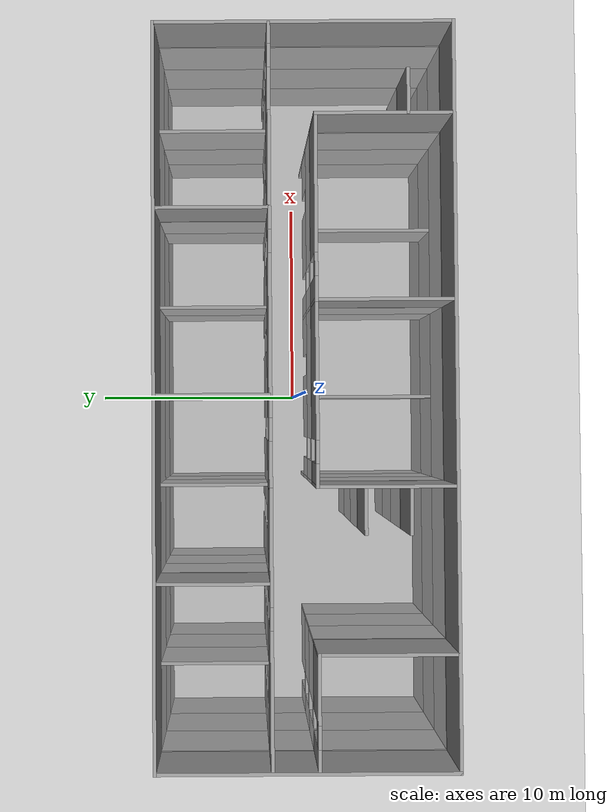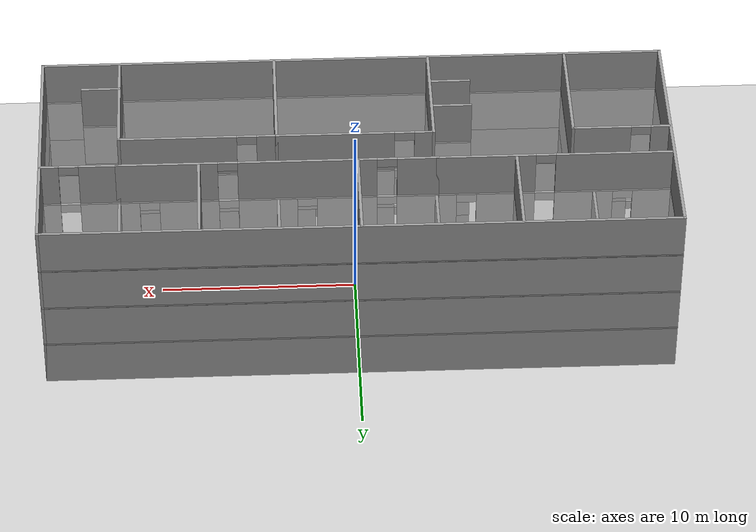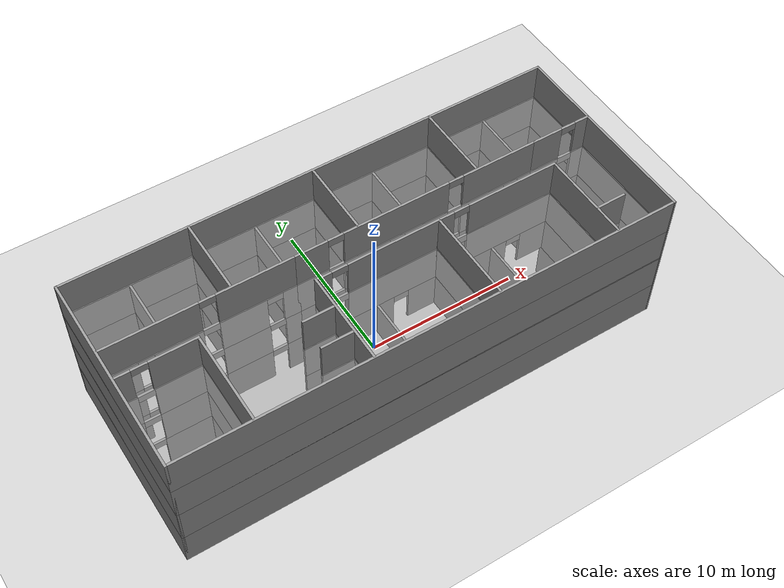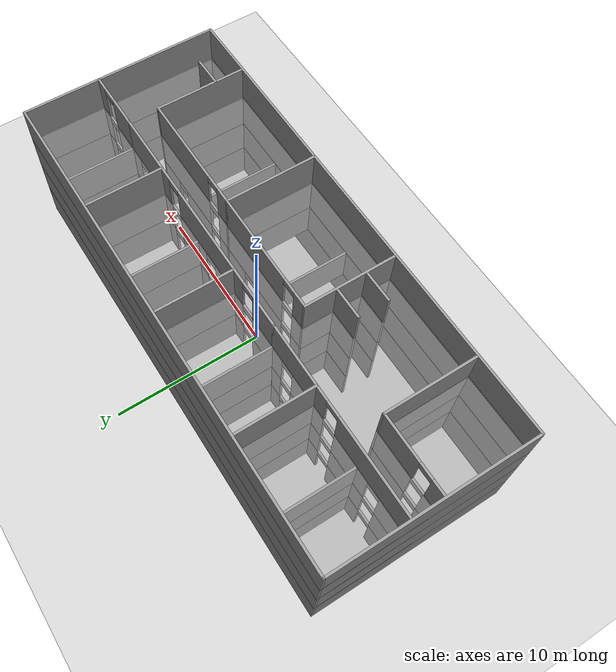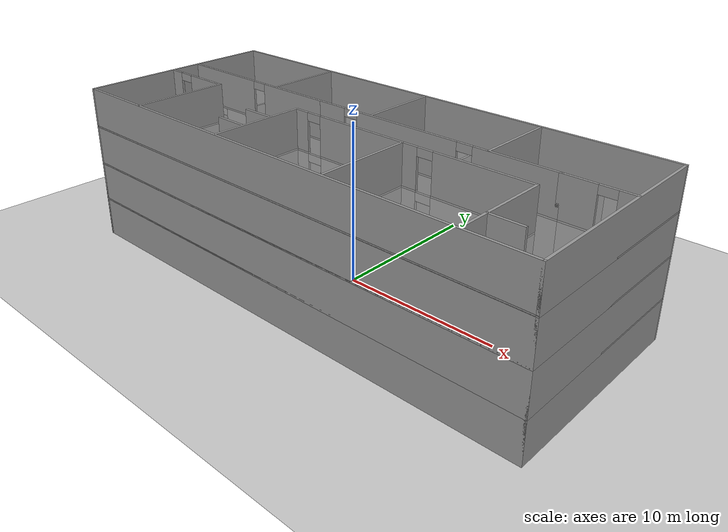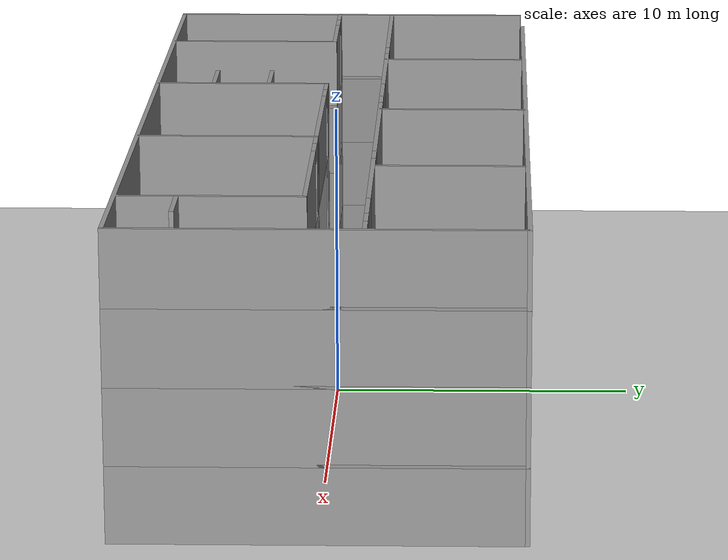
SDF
<sdf version="1.6">
 <world name="default">
  <light name="sun" type="directional">
   <pose>0 0 10 0 -0 0</pose>
   <diffuse>0.8 0.8 0.8 1</diffuse>
   <specular>0.2 0.2 0.2 1</specular>
   <attenuation>
    <range>1000</range>
    <constant>0.9</constant>
    <linear>0.01</linear>
    <quadratic>0.001</quadratic>
   </attenuation>
   <direction>-0.5 0.1 -0.9</direction>
  </light>
  <model name="ground_plane">
   <static>1</static>
   <link name="link">
    <collision name="collision">
     <geometry><plane><normal>0 0 1</normal><size>100 100</size></plane></geometry>
     <surface>
      <contact><collide_bitmask>65535</collide_bitmask></contact>
      <friction><ode><mu>100</mu><mu2>50</mu2></ode></friction>
     </surface>
    </collision>
    <visual name="visual">
     <cast_shadows>0</cast_shadows>
     <geometry><plane><normal>0 0 1</normal><size>100 100</size></plane></geometry>
     <material>
      <script><uri>file://media/materials/scripts/gazebo.material</uri><name>Gazebo/Grey</name></script>
     </material>
    </visual>
   </link>
  </model>
  <gravity>0 0 -9.8</gravity>
  <magnetic_field>6e-06 2.3e-05 -4.2e-05</magnetic_field>
  <atmosphere type="adiabatic"/>
  <physics name="default_physics" default="0" type="ode">
   <max_step_size>0.001</max_step_size>
   <real_time_factor>1</real_time_factor>
   <real_time_update_rate>1000</real_time_update_rate>
  </physics>
  <scene><ambient>0.4 0.4 0.4 1</ambient><background>0.7 0.7 0.7 1</background><shadows>1</shadows></scene>
  <spherical_coordinates>
   <surface_model>EARTH_WGS84</surface_model>
   <latitude_deg>0</latitude_deg>
   <longitude_deg>0</longitude_deg>
   <elevation>0</elevation>
   <heading_deg>0</heading_deg>
  </spherical_coordinates>
  <model name="floor2plan_v2">
   <link name="Floor_0">
    <pose>1e-06 0 2.5 0 -0 0</pose>
    <inertial>
     <mass>1</mass>
     <inertia><ixx>1</ixx><ixy>0</ixy><ixz>0</ixz><iyy>1</iyy><iyz>0</iyz><izz>1</izz></inertia>
    </inertial>
    <visual name="Floor_0_Visual">
     <pose>0 0 0.05 0 -0 0</pose>
     <geometry><box><size>32 13.023 0.1</size></box></geometry>
     <material>
      <script><uri>file://media/materials/scripts/gazebo.material</uri><name>Gazebo/Grey</name></script>
      <ambient>1 1 1 1</ambient>
      <shader type="pixel"><normal_map>__default__</normal_map></shader>
      <diffuse>0.7 0.7 0.7 1</diffuse>
      <specular>0.01 0.01 0.01 1</specular>
      <emissive>0 0 0 1</emissive>
     </material>
     <meta><layer>1</layer></meta>
     <transparency>0.5</transparency>
    </visual>
    <collision name="Floor_0_Collision">
     <pose>0 0 0.05 0 -0 0</pose>
     <geometry><box><size>32 13.023 0.1</size></box></geometry>
     <surface>
      <friction>
       <ode><mu>1</mu><mu2>1</mu2><fdir1>0 0 0</fdir1><slip1>0</slip1><slip2>0</slip2></ode>
       <torsional>
        <coefficient>1</coefficient>
        <patch_radius>0</patch_radius>
        <surface_radius>0</surface_radius>
        <use_patch_radius>1</use_patch_radius>
        <ode><slip>0</slip></ode>
       </torsional>
      </friction>
      <bounce><restitution_coefficient>0</restitution_coefficient><threshold>1e+06</threshold></bounce>
      <contact>
       <collide_without_contact>0</collide_without_contact>
       <collide_without_contact_bitmask>1</collide_without_contact_bitmask>
       <collide_bitmask>1</collide_bitmask>
       <ode>
        <soft_cfm>0</soft_cfm>
        <soft_erp>0.2</soft_erp>
        <kp>1e+13</kp>
        <kd>1</kd>
        <max_vel>0.01</max_vel>
        <min_depth>0</min_depth>
       </ode>
       <bullet>
        <split_impulse>1</split_impulse>
        <split_impulse_penetration_threshold>-0.01</split_impulse_penetration_threshold>
        <soft_cfm>0</soft_cfm>
        <soft_erp>0.2</soft_erp>
        <kp>1e+13</kp>
        <kd>1</kd>
       </bullet>
      </contact>
     </surface>
    </collision>
   </link>
   <link name="Floor_1">
    <pose>1e-06 0 5 0 -0 0</pose>
    <inertial>
     <mass>1</mass>
     <inertia><ixx>1</ixx><ixy>0</ixy><ixz>0</ixz><iyy>1</iyy><iyz>0</iyz><izz>1</izz></inertia>
    </inertial>
    <visual name="Floor_1_Visual">
     <pose>0 0 0.05 0 -0 0</pose>
     <geometry><box><size>32 13.023 0.1</size></box></geometry>
     <material>
      <script><uri>file://media/materials/scripts/gazebo.material</uri><name>Gazebo/Grey</name></script>
      <ambient>1 1 1 1</ambient>
      <shader type="pixel"><normal_map>__default__</normal_map></shader>
      <diffuse>0.7 0.7 0.7 1</diffuse>
      <specular>0.01 0.01 0.01 1</specular>
      <emissive>0 0 0 1</emissive>
     </material>
     <meta><layer>2</layer></meta>
     <transparency>0.5</transparency>
    </visual>
    <collision name="Floor_1_Collision">
     <pose>0 0 0.05 0 -0 0</pose>
     <geometry><box><size>32 13.023 0.1</size></box></geometry>
     <surface>
      <friction>
       <ode><mu>1</mu><mu2>1</mu2><fdir1>0 0 0</fdir1><slip1>0</slip1><slip2>0</slip2></ode>
       <torsional>
        <coefficient>1</coefficient>
        <patch_radius>0</patch_radius>
        <surface_radius>0</surface_radius>
        <use_patch_radius>1</use_patch_radius>
        <ode><slip>0</slip></ode>
       </torsional>
      </friction>
      <bounce><restitution_coefficient>0</restitution_coefficient><threshold>1e+06</threshold></bounce>
      <contact>
       <collide_without_contact>0</collide_without_contact>
       <collide_without_contact_bitmask>1</collide_without_contact_bitmask>
       <collide_bitmask>1</collide_bitmask>
       <ode>
        <soft_cfm>0</soft_cfm>
        <soft_erp>0.2</soft_erp>
        <kp>1e+13</kp>
        <kd>1</kd>
        <max_vel>0.01</max_vel>
        <min_depth>0</min_depth>
       </ode>
       <bullet>
        <split_impulse>1</split_impulse>
        <split_impulse_penetration_threshold>-0.01</split_impulse_penetration_threshold>
        <soft_cfm>0</soft_cfm>
        <soft_erp>0.2</soft_erp>
        <kp>1e+13</kp>
        <kd>1</kd>
       </bullet>
      </contact>
     </surface>
    </collision>
   </link>
   <link name="Floor_2">
    <pose>1e-06 0 7.5 0 -0 0</pose>
    <inertial>
     <mass>1</mass>
     <inertia><ixx>1</ixx><ixy>0</ixy><ixz>0</ixz><iyy>1</iyy><iyz>0</iyz><izz>1</izz></inertia>
    </inertial>
    <visual name="Floor_2_Visual">
     <pose>0 0 0.05 0 -0 0</pose>
     <geometry><box><size>32 13.023 0.1</size></box></geometry>
     <material>
      <script><uri>file://media/materials/scripts/gazebo.material</uri><name>Gazebo/Grey</name></script>
      <ambient>1 1 1 1</ambient>
      <shader type="pixel"><normal_map>__default__</normal_map></shader>
      <diffuse>0.7 0.7 0.7 1</diffuse>
      <specular>0.01 0.01 0.01 1</specular>
      <emissive>0 0 0 1</emissive>
     </material>
     <meta><layer>3</layer></meta>
     <transparency>0.5</transparency>
    </visual>
    <collision name="Floor_2_Collision">
     <pose>0 0 0.05 0 -0 0</pose>
     <geometry><box><size>32 13.023 0.1</size></box></geometry>
     <surface>
      <friction>
       <ode><mu>1</mu><mu2>1</mu2><fdir1>0 0 0</fdir1><slip1>0</slip1><slip2>0</slip2></ode>
       <torsional>
        <coefficient>1</coefficient>
        <patch_radius>0</patch_radius>
        <surface_radius>0</surface_radius>
        <use_patch_radius>1</use_patch_radius>
        <ode><slip>0</slip></ode>
       </torsional>
      </friction>
      <bounce><restitution_coefficient>0</restitution_coefficient><threshold>1e+06</threshold></bounce>
      <contact>
       <collide_without_contact>0</collide_without_contact>
       <collide_without_contact_bitmask>1</collide_without_contact_bitmask>
       <collide_bitmask>1</collide_bitmask>
       <ode>
        <soft_cfm>0</soft_cfm>
        <soft_erp>0.2</soft_erp>
        <kp>1e+13</kp>
        <kd>1</kd>
        <max_vel>0.01</max_vel>
        <min_depth>0</min_depth>
       </ode>
       <bullet>
        <split_impulse>1</split_impulse>
        <split_impulse_penetration_threshold>-0.01</split_impulse_penetration_threshold>
        <soft_cfm>0</soft_cfm>
        <soft_erp>0.2</soft_erp>
        <kp>1e+13</kp>
        <kd>1</kd>
       </bullet>
      </contact>
     </surface>
    </collision>
   </link>
   <link name="Wall_0">
    <pose>1e-06 6.4365 0 0 -0 0</pose>
    <visual name="Wall_0_Visual">
     <pose>0 0 1.25 0 -0 0</pose>
     <geometry><box><size>32 0.15 2.5</size></box></geometry>
     <material>
      <script><uri>file://media/materials/scripts/gazebo.material</uri><name>Gazebo/Grey</name></script>
      <ambient>1 1 1 1</ambient>
      <shader type="pixel"/>
      <diffuse>0.7 0.7 0.7 1</diffuse>
      <specular>0.01 0.01 0.01 1</specular>
      <emissive>0 0 0 1</emissive>
     </material>
     <meta><layer>0</layer></meta>
    </visual>
    <collision name="Wall_0_Collision">
     <pose>0 0 1.25 0 -0 0</pose>
     <geometry><box><size>32 0.15 2.5</size></box></geometry>
     <surface>
      <friction>
       <ode><mu>1</mu><mu2>1</mu2><fdir1>0 0 0</fdir1><slip1>0</slip1><slip2>0</slip2></ode>
       <torsional>
        <coefficient>1</coefficient>
        <patch_radius>0</patch_radius>
        <surface_radius>0</surface_radius>
        <use_patch_radius>1</use_patch_radius>
        <ode><slip>0</slip></ode>
       </torsional>
      </friction>
      <bounce><restitution_coefficient>0</restitution_coefficient><threshold>1e+06</threshold></bounce>
      <contact>
       <collide_without_contact>0</collide_without_contact>
       <collide_without_contact_bitmask>1</collide_without_contact_bitmask>
       <collide_bitmask>1</collide_bitmask>
       <ode>
        <soft_cfm>0</soft_cfm>
        <soft_erp>0.2</soft_erp>
        <kp>1e+13</kp>
        <kd>1</kd>
        <max_vel>0.01</max_vel>
        <min_depth>0</min_depth>
       </ode>
       <bullet>
        <split_impulse>1</split_impulse>
        <split_impulse_penetration_threshold>-0.01</split_impulse_penetration_threshold>
        <soft_cfm>0</soft_cfm>
        <soft_erp>0.2</soft_erp>
        <kp>1e+13</kp>
        <kd>1</kd>
       </bullet>
      </contact>
     </surface>
    </collision>
   </link>
   <link name="Wall_10">
    <pose>1e-06 -6.4365 0 0 -0 0</pose>
    <visual name="Wall_10_Visual">
     <pose>0 0 1.25 0 -0 0</pose>
     <geometry><box><size>32 0.15 2.5</size></box></geometry>
     <material>
      <script><uri>file://media/materials/scripts/gazebo.material</uri><name>Gazebo/Grey</name></script>
      <ambient>1 1 1 1</ambient>
      <shader type="pixel"/>
      <diffuse>0.7 0.7 0.7 1</diffuse>
      <specular>0.01 0.01 0.01 1</specular>
      <emissive>0 0 0 1</emissive>
     </material>
     <meta><layer>0</layer></meta>
    </visual>
    <collision name="Wall_10_Collision">
     <pose>0 0 1.25 0 -0 0</pose>
     <geometry><box><size>32 0.15 2.5</size></box></geometry>
     <surface>
      <friction>
       <ode><mu>1</mu><mu2>1</mu2><fdir1>0 0 0</fdir1><slip1>0</slip1><slip2>0</slip2></ode>
       <torsional>
        <coefficient>1</coefficient>
        <patch_radius>0</patch_radius>
        <surface_radius>0</surface_radius>
        <use_patch_radius>1</use_patch_radius>
        <ode><slip>0</slip></ode>
       </torsional>
      </friction>
      <bounce><restitution_coefficient>0</restitution_coefficient><threshold>1e+06</threshold></bounce>
      <contact>
       <collide_without_contact>0</collide_without_contact>
       <collide_without_contact_bitmask>1</collide_without_contact_bitmask>
       <collide_bitmask>1</collide_bitmask>
       <ode>
        <soft_cfm>0</soft_cfm>
        <soft_erp>0.2</soft_erp>
        <kp>1e+13</kp>
        <kd>1</kd>
        <max_vel>0.01</max_vel>
        <min_depth>0</min_depth>
       </ode>
       <bullet>
        <split_impulse>1</split_impulse>
        <split_impulse_penetration_threshold>-0.01</split_impulse_penetration_threshold>
        <soft_cfm>0</soft_cfm>
        <soft_erp>0.2</soft_erp>
        <kp>1e+13</kp>
        <kd>1</kd>
       </bullet>
      </contact>
     </surface>
    </collision>
   </link>
   <link name="Wall_100">
    <pose>1e-06 -6.4365 5 0 -0 0</pose>
    <visual name="Wall_100_Visual">
     <pose>0 0 1.25 0 -0 0</pose>
     <geometry><box><size>32 0.15 2.5</size></box></geometry>
     <material>
      <script><uri>file://media/materials/scripts/gazebo.material</uri><name>Gazebo/Grey</name></script>
      <ambient>1 1 1 1</ambient>
      <shader type="pixel"/>
      <diffuse>0.7 0.7 0.7 1</diffuse>
      <specular>0.01 0.01 0.01 1</specular>
      <emissive>0 0 0 1</emissive>
     </material>
     <meta><layer>2</layer></meta>
    </visual>
    <collision name="Wall_100_Collision">
     <pose>0 0 1.25 0 -0 0</pose>
     <geometry><box><size>32 0.15 2.5</size></box></geometry>
     <surface>
      <friction>
       <ode><mu>1</mu><mu2>1</mu2><fdir1>0 0 0</fdir1><slip1>0</slip1><slip2>0</slip2></ode>
       <torsional>
        <coefficient>1</coefficient>
        <patch_radius>0</patch_radius>
        <surface_radius>0</surface_radius>
        <use_patch_radius>1</use_patch_radius>
        <ode><slip>0</slip></ode>
       </torsional>
      </friction>
      <bounce><restitution_coefficient>0</restitution_coefficient><threshold>1e+06</threshold></bounce>
      <contact>
       <collide_without_contact>0</collide_without_contact>
       <collide_without_contact_bitmask>1</collide_without_contact_bitmask>
       <collide_bitmask>1</collide_bitmask>
       <ode>
        <soft_cfm>0</soft_cfm>
        <soft_erp>0.2</soft_erp>
        <kp>1e+13</kp>
        <kd>1</kd>
        <max_vel>0.01</max_vel>
        <min_depth>0</min_depth>
       </ode>
       <bullet>
        <split_impulse>1</split_impulse>
        <split_impulse_penetration_threshold>-0.01</split_impulse_penetration_threshold>
        <soft_cfm>0</soft_cfm>
        <soft_erp>0.2</soft_erp>
        <kp>1e+13</kp>
        <kd>1</kd>
       </bullet>
      </contact>
     </surface>
    </collision>
   </link>
   <link name="Wall_101">
    <pose>15.925 0 5 0 -0 1.5708</pose>
    <visual name="Wall_101_Visual">
     <pose>0 0 1.25 0 -0 0</pose>
     <geometry><box><size>13.023 0.15 2.5</size></box></geometry>
     <material>
      <script><uri>file://media/materials/scripts/gazebo.material</uri><name>Gazebo/Grey</name></script>
      <ambient>1 1 1 1</ambient>
      <shader type="pixel"/>
      <diffuse>0.7 0.7 0.7 1</diffuse>
      <specular>0.01 0.01 0.01 1</specular>
      <emissive>0 0 0 1</emissive>
     </material>
     <meta><layer>2</layer></meta>
    </visual>
    <collision name="Wall_101_Collision">
     <pose>0 0 1.25 0 -0 0</pose>
     <geometry><box><size>13.023 0.15 2.5</size></box></geometry>
     <surface>
      <friction>
       <ode><mu>1</mu><mu2>1</mu2><fdir1>0 0 0</fdir1><slip1>0</slip1><slip2>0</slip2></ode>
       <torsional>
        <coefficient>1</coefficient>
        <patch_radius>0</patch_radius>
        <surface_radius>0</surface_radius>
        <use_patch_radius>1</use_patch_radius>
        <ode><slip>0</slip></ode>
       </torsional>
      </friction>
      <bounce><restitution_coefficient>0</restitution_coefficient><threshold>1e+06</threshold></bounce>
      <contact>
       <collide_without_contact>0</collide_without_contact>
       <collide_without_contact_bitmask>1</collide_without_contact_bitmask>
       <collide_bitmask>1</collide_bitmask>
       <ode>
        <soft_cfm>0</soft_cfm>
        <soft_erp>0.2</soft_erp>
        <kp>1e+13</kp>
        <kd>1</kd>
        <max_vel>0.01</max_vel>
        <min_depth>0</min_depth>
       </ode>
       <bullet>
        <split_impulse>1</split_impulse>
        <split_impulse_penetration_threshold>-0.01</split_impulse_penetration_threshold>
        <soft_cfm>0</soft_cfm>
        <soft_erp>0.2</soft_erp>
        <kp>1e+13</kp>
        <kd>1</kd>
       </bullet>
      </contact>
     </surface>
    </collision>
   </link>
   <link name="Wall_102">
    <pose>-9.9294 1.47672 5 0 -0 0</pose>
    <visual name="Wall_102_Visual_0">
     <pose>-4.985 0 1.25 0 -0 0</pose>
     <geometry><box><size>1.987 0.15 2.5</size></box></geometry>
     <material>
      <script><uri>file://media/materials/scripts/gazebo.material</uri><name>Gazebo/Grey</name></script>
      <ambient>1 1 1 1</ambient>
      <shader type="pixel"/>
      <diffuse>0.7 0.7 0.7 1</diffuse>
      <specular>0.01 0.01 0.01 1</specular>
      <emissive>0 0 0 1</emissive>
     </material>
     <meta><layer>2</layer></meta>
    </visual>
    <visual name="Wall_102_Visual_1">
     <pose>-1.5135 0 1.25 0 -0 0</pose>
     <geometry><box><size>2.956 0.15 2.5</size></box></geometry>
     <material>
      <script><uri>file://media/materials/scripts/gazebo.material</uri><name>Gazebo/Grey</name></script>
      <ambient>1 1 1 1</ambient>
      <shader type="pixel"/>
      <diffuse>0.7 0.7 0.7 1</diffuse>
      <specular>0.01 0.01 0.01 1</specular>
      <emissive>0 0 0 1</emissive>
     </material>
     <meta><layer>2</layer></meta>
    </visual>
    <visual name="Wall_102_Visual_2">
     <pose>2.4425 0 1.25 0 -0 0</pose>
     <geometry><box><size>2.956 0.15 2.5</size></box></geometry>
     <material>
      <script><uri>file://media/materials/scripts/gazebo.material</uri><name>Gazebo/Grey</name></script>
      <ambient>1 1 1 1</ambient>
      <shader type="pixel"/>
      <diffuse>0.7 0.7 0.7 1</diffuse>
      <specular>0.01 0.01 0.01 1</specular>
      <emissive>0 0 0 1</emissive>
     </material>
     <meta><layer>2</layer></meta>
    </visual>
    <visual name="Wall_102_Visual_3">
     <pose>5.4495 0 1.25 0 -0 0</pose>
     <geometry><box><size>1.058 0.15 2.5</size></box></geometry>
     <material>
      <script><uri>file://media/materials/scripts/gazebo.material</uri><name>Gazebo/Grey</name></script>
      <ambient>1 1 1 1</ambient>
      <shader type="pixel"/>
      <diffuse>0.7 0.7 0.7 1</diffuse>
      <specular>0.01 0.01 0.01 1</specular>
      <emissive>0 0 0 1</emissive>
     </material>
     <meta><layer>2</layer></meta>
    </visual>
    <visual name="Wall_102_Visual_4">
     <pose>-3.4915 0 2.25 0 -0 0</pose>
     <geometry><box><size>1 0.15 0.5</size></box></geometry>
     <material>
      <script><uri>file://media/materials/scripts/gazebo.material</uri><name>Gazebo/Grey</name></script>
      <ambient>1 1 1 1</ambient>
      <shader type="pixel"/>
      <diffuse>0.7 0.7 0.7 1</diffuse>
      <specular>0.01 0.01 0.01 1</specular>
      <emissive>0 0 0 1</emissive>
     </material>
     <meta><layer>2</layer></meta>
    </visual>
    <visual name="Wall_102_Visual_5">
     <pose>0.4645 0 2.25 0 -0 0</pose>
     <geometry><box><size>1 0.15 0.5</size></box></geometry>
     <material>
      <script><uri>file://media/materials/scripts/gazebo.material</uri><name>Gazebo/Grey</name></script>
      <ambient>1 1 1 1</ambient>
      <shader type="pixel"/>
      <diffuse>0.7 0.7 0.7 1</diffuse>
      <specular>0.01 0.01 0.01 1</specular>
      <emissive>0 0 0 1</emissive>
     </material>
     <meta><layer>2</layer></meta>
    </visual>
    <visual name="Wall_102_Visual_6">
     <pose>4.4205 0 2.25 0 -0 0</pose>
     <geometry><box><size>1 0.15 0.5</size></box></geometry>
     <material>
      <script><uri>file://media/materials/scripts/gazebo.material</uri><name>Gazebo/Grey</name></script>
      <ambient>1 1 1 1</ambient>
      <shader type="pixel"/>
      <diffuse>0.7 0.7 0.7 1</diffuse>
      <specular>0.01 0.01 0.01 1</specular>
      <emissive>0 0 0 1</emissive>
     </material>
     <meta><layer>2</layer></meta>
    </visual>
    <collision name="Wall_102_Collision_0">
     <pose>-4.985 0 1.25 0 -0 0</pose>
     <geometry><box><size>1.987 0.15 2.5</size></box></geometry>
     <surface>
      <friction>
       <ode><mu>1</mu><mu2>1</mu2><fdir1>0 0 0</fdir1><slip1>0</slip1><slip2>0</slip2></ode>
       <torsional>
        <coefficient>1</coefficient>
        <patch_radius>0</patch_radius>
        <surface_radius>0</surface_radius>
        <use_patch_radius>1</use_patch_radius>
        <ode><slip>0</slip></ode>
       </torsional>
      </friction>
      <bounce><restitution_coefficient>0</restitution_coefficient><threshold>1e+06</threshold></bounce>
      <contact>
       <collide_without_contact>0</collide_without_contact>
       <collide_without_contact_bitmask>1</collide_without_contact_bitmask>
       <collide_bitmask>1</collide_bitmask>
       <ode>
        <soft_cfm>0</soft_cfm>
        <soft_erp>0.2</soft_erp>
        <kp>1e+13</kp>
        <kd>1</kd>
        <max_vel>0.01</max_vel>
        <min_depth>0</min_depth>
       </ode>
       <bullet>
        <split_impulse>1</split_impulse>
        <split_impulse_penetration_threshold>-0.01</split_impulse_penetration_threshold>
        <soft_cfm>0</soft_cfm>
        <soft_erp>0.2</soft_erp>
        <kp>1e+13</kp>
        <kd>1</kd>
       </bullet>
      </contact>
     </surface>
    </collision>
    <collision name="Wall_102_Collision_2">
     <pose>2.4425 0 1.25 0 -0 0</pose>
     <geometry><box><size>2.956 0.15 2.5</size></box></geometry>
     <surface>
      <friction>
       <ode><mu>1</mu><mu2>1</mu2><fdir1>0 0 0</fdir1><slip1>0</slip1><slip2>0</slip2></ode>
       <torsional>
        <coefficient>1</coefficient>
        <patch_radius>0</patch_radius>
        <surface_radius>0</surface_radius>
        <use_patch_radius>1</use_patch_radius>
        <ode><slip>0</slip></ode>
       </torsional>
      </friction>
      <bounce><restitution_coefficient>0</restitution_coefficient><threshold>1e+06</threshold></bounce>
      <contact>
       <collide_without_contact>0</collide_without_contact>
       <collide_without_contact_bitmask>1</collide_without_contact_bitmask>
       <collide_bitmask>1</collide_bitmask>
       <ode>
        <soft_cfm>0</soft_cfm>
        <soft_erp>0.2</soft_erp>
        <kp>1e+13</kp>
        <kd>1</kd>
        <max_vel>0.01</max_vel>
        <min_depth>0</min_depth>
       </ode>
       <bullet>
        <split_impulse>1</split_impulse>
        <split_impulse_penetration_threshold>-0.01</split_impulse_penetration_threshold>
        <soft_cfm>0</soft_cfm>
        <soft_erp>0.2</soft_erp>
        <kp>1e+13</kp>
        <kd>1</kd>
       </bullet>
      </contact>
     </surface>
    </collision>
    <collision name="Wall_102_Collision_1">
     <pose>-1.5135 0 1.25 0 -0 0</pose>
     <geometry><box><size>2.956 0.15 2.5</size></box></geometry>
     <surface>
      <friction>
       <ode><mu>1</mu><mu2>1</mu2><fdir1>0 0 0</fdir1><slip1>0</slip1><slip2>0</slip2></ode>
       <torsional>
        <coefficient>1</coefficient>
        <patch_radius>0</patch_radius>
        <surface_radius>0</surface_radius>
        <use_patch_radius>1</use_patch_radius>
        <ode><slip>0</slip></ode>
       </torsional>
      </friction>
      <bounce><restitution_coefficient>0</restitution_coefficient><threshold>1e+06</threshold></bounce>
      <contact>
       <collide_without_contact>0</collide_without_contact>
       <collide_without_contact_bitmask>1</collide_without_contact_bitmask>
       <collide_bitmask>1</collide_bitmask>
       <ode>
        <soft_cfm>0</soft_cfm>
        <soft_erp>0.2</soft_erp>
        <kp>1e+13</kp>
        <kd>1</kd>
        <max_vel>0.01</max_vel>
        <min_depth>0</min_depth>
       </ode>
       <bullet>
        <split_impulse>1</split_impulse>
        <split_impulse_penetration_threshold>-0.01</split_impulse_penetration_threshold>
        <soft_cfm>0</soft_cfm>
        <soft_erp>0.2</soft_erp>
        <kp>1e+13</kp>
        <kd>1</kd>
       </bullet>
      </contact>
     </surface>
    </collision>
    <collision name="Wall_102_Collision_3">
     <pose>5.4495 0 1.25 0 -0 0</pose>
     <geometry><box><size>1.058 0.15 2.5</size></box></geometry>
     <surface>
      <friction>
       <ode><mu>1</mu><mu2>1</mu2><fdir1>0 0 0</fdir1><slip1>0</slip1><slip2>0</slip2></ode>
       <torsional>
        <coefficient>1</coefficient>
        <patch_radius>0</patch_radius>
        <surface_radius>0</surface_radius>
        <use_patch_radius>1</use_patch_radius>
        <ode><slip>0</slip></ode>
       </torsional>
      </friction>
      <bounce><restitution_coefficient>0</restitution_coefficient><threshold>1e+06</threshold></bounce>
      <contact>
       <collide_without_contact>0</collide_without_contact>
       <collide_without_contact_bitmask>1</collide_without_contact_bitmask>
       <collide_bitmask>1</collide_bitmask>
       <ode>
        <soft_cfm>0</soft_cfm>
        <soft_erp>0.2</soft_erp>
        <kp>1e+13</kp>
        <kd>1</kd>
        <max_vel>0.01</max_vel>
        <min_depth>0</min_depth>
       </ode>
       <bullet>
        <split_impulse>1</split_impulse>
        <split_impulse_penetration_threshold>-0.01</split_impulse_penetration_threshold>
        <soft_cfm>0</soft_cfm>
        <soft_erp>0.2</soft_erp>
        <kp>1e+13</kp>
        <kd>1</kd>
       </bullet>
      </contact>
     </surface>
    </collision>
    <collision name="Wall_102_Collision_4">
     <pose>-3.4915 0 2.25 0 -0 0</pose>
     <geometry><box><size>1 0.15 0.5</size></box></geometry>
     <surface>
      <friction>
       <ode><mu>1</mu><mu2>1</mu2><fdir1>0 0 0</fdir1><slip1>0</slip1><slip2>0</slip2></ode>
       <torsional>
        <coefficient>1</coefficient>
        <patch_radius>0</patch_radius>
        <surface_radius>0</surface_radius>
        <use_patch_radius>1</use_patch_radius>
        <ode><slip>0</slip></ode>
       </torsional>
      </friction>
      <bounce><restitution_coefficient>0</restitution_coefficient><threshold>1e+06</threshold></bounce>
      <contact>
       <collide_without_contact>0</collide_without_contact>
       <collide_without_contact_bitmask>1</collide_without_contact_bitmask>
       <collide_bitmask>1</collide_bitmask>
       <ode>
        <soft_cfm>0</soft_cfm>
        <soft_erp>0.2</soft_erp>
        <kp>1e+13</kp>
        <kd>1</kd>
        <max_vel>0.01</max_vel>
        <min_depth>0</min_depth>
       </ode>
       <bullet>
        <split_impulse>1</split_impulse>
        <split_impulse_penetration_threshold>-0.01</split_impulse_penetration_threshold>
        <soft_cfm>0</soft_cfm>
        <soft_erp>0.2</soft_erp>
        <kp>1e+13</kp>
        <kd>1</kd>
       </bullet>
      </contact>
     </surface>
    </collision>
    <collision name="Wall_102_Collision_5">
     <pose>0.4645 0 2.25 0 -0 0</pose>
     <geometry><box><size>1 0.15 0.5</size></box></geometry>
     <surface>
      <friction>
       <ode><mu>1</mu><mu2>1</mu2><fdir1>0 0 0</fdir1><slip1>0</slip1><slip2>0</slip2></ode>
       <torsional>
        <coefficient>1</coefficient>
        <patch_radius>0</patch_radius>
        <surface_radius>0</surface_radius>
        <use_patch_radius>1</use_patch_radius>
        <ode><slip>0</slip></ode>
       </torsional>
      </friction>
      <bounce><restitution_coefficient>0</restitution_coefficient><threshold>1e+06</threshold></bounce>
      <contact>
       <collide_without_contact>0</collide_without_contact>
       <collide_without_contact_bitmask>1</collide_without_contact_bitmask>
       <collide_bitmask>1</collide_bitmask>
       <ode>
        <soft_cfm>0</soft_cfm>
        <soft_erp>0.2</soft_erp>
        <kp>1e+13</kp>
        <kd>1</kd>
        <max_vel>0.01</max_vel>
        <min_depth>0</min_depth>
       </ode>
       <bullet>
        <split_impulse>1</split_impulse>
        <split_impulse_penetration_threshold>-0.01</split_impulse_penetration_threshold>
        <soft_cfm>0</soft_cfm>
        <soft_erp>0.2</soft_erp>
        <kp>1e+13</kp>
        <kd>1</kd>
       </bullet>
      </contact>
     </surface>
    </collision>
    <collision name="Wall_102_Collision_6">
     <pose>4.4205 0 2.25 0 -0 0</pose>
     <geometry><box><size>1 0.15 0.5</size></box></geometry>
     <surface>
      <friction>
       <ode><mu>1</mu><mu2>1</mu2><fdir1>0 0 0</fdir1><slip1>0</slip1><slip2>0</slip2></ode>
       <torsional>
        <coefficient>1</coefficient>
        <patch_radius>0</patch_radius>
        <surface_radius>0</surface_radius>
        <use_patch_radius>1</use_patch_radius>
        <ode><slip>0</slip></ode>
       </torsional>
      </friction>
      <bounce><restitution_coefficient>0</restitution_coefficient><threshold>1e+06</threshold></bounce>
      <contact>
       <collide_without_contact>0</collide_without_contact>
       <collide_without_contact_bitmask>1</collide_without_contact_bitmask>
       <collide_bitmask>1</collide_bitmask>
       <ode>
        <soft_cfm>0</soft_cfm>
        <soft_erp>0.2</soft_erp>
        <kp>1e+13</kp>
        <kd>1</kd>
        <max_vel>0.01</max_vel>
        <min_depth>0</min_depth>
       </ode>
       <bullet>
        <split_impulse>1</split_impulse>
        <split_impulse_penetration_threshold>-0.01</split_impulse_penetration_threshold>
        <soft_cfm>0</soft_cfm>
        <soft_erp>0.2</soft_erp>
        <kp>1e+13</kp>
        <kd>1</kd>
       </bullet>
      </contact>
     </surface>
    </collision>
   </link>
   <link name="Wall_103">
    <pose>-11.9689 3.95072 5 0 0 -1.5708</pose>
    <visual name="Wall_103_Visual">
     <pose>0 0 1.25 0 -0 0</pose>
     <geometry><box><size>5 0.15 2.5</size></box></geometry>
     <material>
      <script><uri>file://media/materials/scripts/gazebo.material</uri><name>Gazebo/Grey</name></script>
      <ambient>1 1 1 1</ambient>
      <shader type="pixel"/>
      <diffuse>0.7 0.7 0.7 1</diffuse>
      <specular>0.01 0.01 0.01 1</specular>
      <emissive>0 0 0 1</emissive>
     </material>
     <meta><layer>2</layer></meta>
    </visual>
    <collision name="Wall_103_Collision">
     <pose>0 0 1.25 0 -0 0</pose>
     <geometry><box><size>5 0.15 2.5</size></box></geometry>
     <surface>
      <friction>
       <ode><mu>1</mu><mu2>1</mu2><fdir1>0 0 0</fdir1><slip1>0</slip1><slip2>0</slip2></ode>
       <torsional>
        <coefficient>1</coefficient>
        <patch_radius>0</patch_radius>
        <surface_radius>0</surface_radius>
        <use_patch_radius>1</use_patch_radius>
        <ode><slip>0</slip></ode>
       </torsional>
      </friction>
      <bounce><restitution_coefficient>0</restitution_coefficient><threshold>1e+06</threshold></bounce>
      <contact>
       <collide_without_contact>0</collide_without_contact>
       <collide_without_contact_bitmask>1</collide_without_contact_bitmask>
       <collide_bitmask>1</collide_bitmask>
       <ode>
        <soft_cfm>0</soft_cfm>
        <soft_erp>0.2</soft_erp>
        <kp>1e+13</kp>
        <kd>1</kd>
        <max_vel>0.01</max_vel>
        <min_depth>0</min_depth>
       </ode>
       <bullet>
        <split_impulse>1</split_impulse>
        <split_impulse_penetration_threshold>-0.01</split_impulse_penetration_threshold>
        <soft_cfm>0</soft_cfm>
        <soft_erp>0.2</soft_erp>
        <kp>1e+13</kp>
        <kd>1</kd>
       </bullet>
      </contact>
     </surface>
    </collision>
   </link>
   <link name="Wall_104">
    <pose>-7.9899 3.92772 5 0 0 -1.5708</pose>
    <visual name="Wall_104_Visual">
     <pose>0 0 1.25 0 -0 0</pose>
     <geometry><box><size>5 0.15 2.5</size></box></geometry>
     <material>
      <script><uri>file://media/materials/scripts/gazebo.material</uri><name>Gazebo/Grey</name></script>
      <ambient>1 1 1 1</ambient>
      <shader type="pixel"/>
      <diffuse>0.7 0.7 0.7 1</diffuse>
      <specular>0.01 0.01 0.01 1</specular>
      <emissive>0 0 0 1</emissive>
     </material>
     <meta><layer>2</layer></meta>
    </visual>
    <collision name="Wall_104_Collision">
     <pose>0 0 1.25 0 -0 0</pose>
     <geometry><box><size>5 0.15 2.5</size></box></geometry>
     <surface>
      <friction>
       <ode><mu>1</mu><mu2>1</mu2><fdir1>0 0 0</fdir1><slip1>0</slip1><slip2>0</slip2></ode>
       <torsional>
        <coefficient>1</coefficient>
        <patch_radius>0</patch_radius>
        <surface_radius>0</surface_radius>
        <use_patch_radius>1</use_patch_radius>
        <ode><slip>0</slip></ode>
       </torsional>
      </friction>
      <bounce><restitution_coefficient>0</restitution_coefficient><threshold>1e+06</threshold></bounce>
      <contact>
       <collide_without_contact>0</collide_without_contact>
       <collide_without_contact_bitmask>1</collide_without_contact_bitmask>
       <collide_bitmask>1</collide_bitmask>
       <ode>
        <soft_cfm>0</soft_cfm>
        <soft_erp>0.2</soft_erp>
        <kp>1e+13</kp>
        <kd>1</kd>
        <max_vel>0.01</max_vel>
        <min_depth>0</min_depth>
       </ode>
       <bullet>
        <split_impulse>1</split_impulse>
        <split_impulse_penetration_threshold>-0.01</split_impulse_penetration_threshold>
        <soft_cfm>0</soft_cfm>
        <soft_erp>0.2</soft_erp>
        <kp>1e+13</kp>
        <kd>1</kd>
       </bullet>
      </contact>
     </surface>
    </collision>
   </link>
   <link name="Wall_105">
    <pose>4.0241 1.47672 5 0 -0 0</pose>
    <visual name="Wall_105_Visual_0">
     <pose>-7.0665 0 1.25 0 -0 0</pose>
     <geometry><box><size>2.117 0.15 2.5</size></box></geometry>
     <material>
      <script><uri>file://media/materials/scripts/gazebo.material</uri><name>Gazebo/Grey</name></script>
      <ambient>1 1 1 1</ambient>
      <shader type="pixel"/>
      <diffuse>0.7 0.7 0.7 1</diffuse>
      <specular>0.01 0.01 0.01 1</specular>
      <emissive>0 0 0 1</emissive>
     </material>
     <meta><layer>2</layer></meta>
    </visual>
    <visual name="Wall_105_Visual_1">
     <pose>-3.4955 0 1.25 0 -0 0</pose>
     <geometry><box><size>3.025 0.15 2.5</size></box></geometry>
     <material>
      <script><uri>file://media/materials/scripts/gazebo.material</uri><name>Gazebo/Grey</name></script>
      <ambient>1 1 1 1</ambient>
      <shader type="pixel"/>
      <diffuse>0.7 0.7 0.7 1</diffuse>
      <specular>0.01 0.01 0.01 1</specular>
      <emissive>0 0 0 1</emissive>
     </material>
     <meta><layer>2</layer></meta>
    </visual>
    <visual name="Wall_105_Visual_2">
     <pose>0.495 0 1.25 0 -0 0</pose>
     <geometry><box><size>2.956 0.15 2.5</size></box></geometry>
     <material>
      <script><uri>file://media/materials/scripts/gazebo.material</uri><name>Gazebo/Grey</name></script>
      <ambient>1 1 1 1</ambient>
      <shader type="pixel"/>
      <diffuse>0.7 0.7 0.7 1</diffuse>
      <specular>0.01 0.01 0.01 1</specular>
      <emissive>0 0 0 1</emissive>
     </material>
     <meta><layer>2</layer></meta>
    </visual>
    <visual name="Wall_105_Visual_3">
     <pose>4.474 0 1.25 0 -0 0</pose>
     <geometry><box><size>3.002 0.15 2.5</size></box></geometry>
     <material>
      <script><uri>file://media/materials/scripts/gazebo.material</uri><name>Gazebo/Grey</name></script>
      <ambient>1 1 1 1</ambient>
      <shader type="pixel"/>
      <diffuse>0.7 0.7 0.7 1</diffuse>
      <specular>0.01 0.01 0.01 1</specular>
      <emissive>0 0 0 1</emissive>
     </material>
     <meta><layer>2</layer></meta>
    </visual>
    <visual name="Wall_105_Visual_4">
     <pose>7.55 0 1.25 0 -0 0</pose>
     <geometry><box><size>1.15 0.15 2.5</size></box></geometry>
     <material>
      <script><uri>file://media/materials/scripts/gazebo.material</uri><name>Gazebo/Grey</name></script>
      <ambient>1 1 1 1</ambient>
      <shader type="pixel"/>
      <diffuse>0.7 0.7 0.7 1</diffuse>
      <specular>0.01 0.01 0.01 1</specular>
      <emissive>0 0 0 1</emissive>
     </material>
     <meta><layer>2</layer></meta>
    </visual>
    <visual name="Wall_105_Visual_5">
     <pose>-5.508 0 2.25 0 -0 0</pose>
     <geometry><box><size>1 0.15 0.5</size></box></geometry>
     <material>
      <script><uri>file://media/materials/scripts/gazebo.material</uri><name>Gazebo/Grey</name></script>
      <ambient>1 1 1 1</ambient>
      <shader type="pixel"/>
      <diffuse>0.7 0.7 0.7 1</diffuse>
      <specular>0.01 0.01 0.01 1</specular>
      <emissive>0 0 0 1</emissive>
     </material>
     <meta><layer>2</layer></meta>
    </visual>
    <visual name="Wall_105_Visual_6">
     <pose>-1.483 0 2.25 0 -0 0</pose>
     <geometry><box><size>1 0.15 0.5</size></box></geometry>
     <material>
      <script><uri>file://media/materials/scripts/gazebo.material</uri><name>Gazebo/Grey</name></script>
      <ambient>1 1 1 1</ambient>
      <shader type="pixel"/>
      <diffuse>0.7 0.7 0.7 1</diffuse>
      <specular>0.01 0.01 0.01 1</specular>
      <emissive>0 0 0 1</emissive>
     </material>
     <meta><layer>2</layer></meta>
    </visual>
    <visual name="Wall_105_Visual_7">
     <pose>2.473 0 2.25 0 -0 0</pose>
     <geometry><box><size>1 0.15 0.5</size></box></geometry>
     <material>
      <script><uri>file://media/materials/scripts/gazebo.material</uri><name>Gazebo/Grey</name></script>
      <ambient>1 1 1 1</ambient>
      <shader type="pixel"/>
      <diffuse>0.7 0.7 0.7 1</diffuse>
      <specular>0.01 0.01 0.01 1</specular>
      <emissive>0 0 0 1</emissive>
     </material>
     <meta><layer>2</layer></meta>
    </visual>
    <visual name="Wall_105_Visual_8">
     <pose>6.475 0 2.25 0 -0 0</pose>
     <geometry><box><size>1 0.15 0.5</size></box></geometry>
     <material>
      <script><uri>file://media/materials/scripts/gazebo.material</uri><name>Gazebo/Grey</name></script>
      <ambient>1 1 1 1</ambient>
      <shader type="pixel"/>
      <diffuse>0.7 0.7 0.7 1</diffuse>
      <specular>0.01 0.01 0.01 1</specular>
      <emissive>0 0 0 1</emissive>
     </material>
     <meta><layer>2</layer></meta>
    </visual>
    <collision name="Wall_105_Collision_0">
     <pose>-7.0665 0 1.25 0 -0 0</pose>
     <geometry><box><size>2.117 0.15 2.5</size></box></geometry>
     <surface>
      <friction>
       <ode><mu>1</mu><mu2>1</mu2><fdir1>0 0 0</fdir1><slip1>0</slip1><slip2>0</slip2></ode>
       <torsional>
        <coefficient>1</coefficient>
        <patch_radius>0</patch_radius>
        <surface_radius>0</surface_radius>
        <use_patch_radius>1</use_patch_radius>
        <ode><slip>0</slip></ode>
       </torsional>
      </friction>
      <bounce><restitution_coefficient>0</restitution_coefficient><threshold>1e+06</threshold></bounce>
      <contact>
       <collide_without_contact>0</collide_without_contact>
       <collide_without_contact_bitmask>1</collide_without_contact_bitmask>
       <collide_bitmask>1</collide_bitmask>
       <ode>
        <soft_cfm>0</soft_cfm>
        <soft_erp>0.2</soft_erp>
        <kp>1e+13</kp>
        <kd>1</kd>
        <max_vel>0.01</max_vel>
        <min_depth>0</min_depth>
       </ode>
       <bullet>
        <split_impulse>1</split_impulse>
        <split_impulse_penetration_threshold>-0.01</split_impulse_penetration_threshold>
        <soft_cfm>0</soft_cfm>
        <soft_erp>0.2</soft_erp>
        <kp>1e+13</kp>
        <kd>1</kd>
       </bullet>
      </contact>
     </surface>
    </collision>
    <collision name="Wall_105_Collision_1">
     <pose>-3.4955 0 1.25 0 -0 0</pose>
     <geometry><box><size>3.025 0.15 2.5</size></box></geometry>
     <surface>
      <friction>
       <ode><mu>1</mu><mu2>1</mu2><fdir1>0 0 0</fdir1><slip1>0</slip1><slip2>0</slip2></ode>
       <torsional>
        <coefficient>1</coefficient>
        <patch_radius>0</patch_radius>
        <surface_radius>0</surface_radius>
        <use_patch_radius>1</use_patch_radius>
        <ode><slip>0</slip></ode>
       </torsional>
      </friction>
      <bounce><restitution_coefficient>0</restitution_coefficient><threshold>1e+06</threshold></bounce>
      <contact>
       <collide_without_contact>0</collide_without_contact>
       <collide_without_contact_bitmask>1</collide_without_contact_bitmask>
       <collide_bitmask>1</collide_bitmask>
       <ode>
        <soft_cfm>0</soft_cfm>
        <soft_erp>0.2</soft_erp>
        <kp>1e+13</kp>
        <kd>1</kd>
        <max_vel>0.01</max_vel>
        <min_depth>0</min_depth>
       </ode>
       <bullet>
        <split_impulse>1</split_impulse>
        <split_impulse_penetration_threshold>-0.01</split_impulse_penetration_threshold>
        <soft_cfm>0</soft_cfm>
        <soft_erp>0.2</soft_erp>
        <kp>1e+13</kp>
        <kd>1</kd>
       </bullet>
      </contact>
     </surface>
    </collision>
    <collision name="Wall_105_Collision_2">
     <pose>0.495 0 1.25 0 -0 0</pose>
     <geometry><box><size>2.956 0.15 2.5</size></box></geometry>
     <surface>
      <friction>
       <ode><mu>1</mu><mu2>1</mu2><fdir1>0 0 0</fdir1><slip1>0</slip1><slip2>0</slip2></ode>
       <torsional>
        <coefficient>1</coefficient>
        <patch_radius>0</patch_radius>
        <surface_radius>0</surface_radius>
        <use_patch_radius>1</use_patch_radius>
        <ode><slip>0</slip></ode>
       </torsional>
      </friction>
      <bounce><restitution_coefficient>0</restitution_coefficient><threshold>1e+06</threshold></bounce>
      <contact>
       <collide_without_contact>0</collide_without_contact>
       <collide_without_contact_bitmask>1</collide_without_contact_bitmask>
       <collide_bitmask>1</collide_bitmask>
       <ode>
        <soft_cfm>0</soft_cfm>
        <soft_erp>0.2</soft_erp>
        <kp>1e+13</kp>
        <kd>1</kd>
        <max_vel>0.01</max_vel>
        <min_depth>0</min_depth>
       </ode>
       <bullet>
        <split_impulse>1</split_impulse>
        <split_impulse_penetration_threshold>-0.01</split_impulse_penetration_threshold>
        <soft_cfm>0</soft_cfm>
        <soft_erp>0.2</soft_erp>
        <kp>1e+13</kp>
        <kd>1</kd>
       </bullet>
      </contact>
     </surface>
    </collision>
    <collision name="Wall_105_Collision_3">
     <pose>4.474 0 1.25 0 -0 0</pose>
     <geometry><box><size>3.002 0.15 2.5</size></box></geometry>
     <surface>
      <friction>
       <ode><mu>1</mu><mu2>1</mu2><fdir1>0 0 0</fdir1><slip1>0</slip1><slip2>0</slip2></ode>
       <torsional>
        <coefficient>1</coefficient>
        <patch_radius>0</patch_radius>
        <surface_radius>0</surface_radius>
        <use_patch_radius>1</use_patch_radius>
        <ode><slip>0</slip></ode>
       </torsional>
      </friction>
      <bounce><restitution_coefficient>0</restitution_coefficient><threshold>1e+06</threshold></bounce>
      <contact>
       <collide_without_contact>0</collide_without_contact>
       <collide_without_contact_bitmask>1</collide_without_contact_bitmask>
       <collide_bitmask>1</collide_bitmask>
       <ode>
        <soft_cfm>0</soft_cfm>
        <soft_erp>0.2</soft_erp>
        <kp>1e+13</kp>
        <kd>1</kd>
        <max_vel>0.01</max_vel>
        <min_depth>0</min_depth>
       </ode>
       <bullet>
        <split_impulse>1</split_impulse>
        <split_impulse_penetration_threshold>-0.01</split_impulse_penetration_threshold>
        <soft_cfm>0</soft_cfm>
        <soft_erp>0.2</soft_erp>
        <kp>1e+13</kp>
        <kd>1</kd>
       </bullet>
      </contact>
     </surface>
    </collision>
    <collision name="Wall_105_Collision_4">
     <pose>7.55 0 1.25 0 -0 0</pose>
     <geometry><box><size>1.15 0.15 2.5</size></box></geometry>
     <surface>
      <friction>
       <ode><mu>1</mu><mu2>1</mu2><fdir1>0 0 0</fdir1><slip1>0</slip1><slip2>0</slip2></ode>
       <torsional>
        <coefficient>1</coefficient>
        <patch_radius>0</patch_radius>
        <surface_radius>0</surface_radius>
        <use_patch_radius>1</use_patch_radius>
        <ode><slip>0</slip></ode>
       </torsional>
      </friction>
      <bounce><restitution_coefficient>0</restitution_coefficient><threshold>1e+06</threshold></bounce>
      <contact>
       <collide_without_contact>0</collide_without_contact>
       <collide_without_contact_bitmask>1</collide_without_contact_bitmask>
       <collide_bitmask>1</collide_bitmask>
       <ode>
        <soft_cfm>0</soft_cfm>
        <soft_erp>0.2</soft_erp>
        <kp>1e+13</kp>
        <kd>1</kd>
        <max_vel>0.01</max_vel>
        <min_depth>0</min_depth>
       </ode>
       <bullet>
        <split_impulse>1</split_impulse>
        <split_impulse_penetration_threshold>-0.01</split_impulse_penetration_threshold>
        <soft_cfm>0</soft_cfm>
        <soft_erp>0.2</soft_erp>
        <kp>1e+13</kp>
        <kd>1</kd>
       </bullet>
      </contact>
     </surface>
    </collision>
    <collision name="Wall_105_Collision_5">
     <pose>-5.508 0 2.25 0 -0 0</pose>
     <geometry><box><size>1 0.15 0.5</size></box></geometry>
     <surface>
      <friction>
       <ode><mu>1</mu><mu2>1</mu2><fdir1>0 0 0</fdir1><slip1>0</slip1><slip2>0</slip2></ode>
       <torsional>
        <coefficient>1</coefficient>
        <patch_radius>0</patch_radius>
        <surface_radius>0</surface_radius>
        <use_patch_radius>1</use_patch_radius>
        <ode><slip>0</slip></ode>
       </torsional>
      </friction>
      <bounce><restitution_coefficient>0</restitution_coefficient><threshold>1e+06</threshold></bounce>
      <contact>
       <collide_without_contact>0</collide_without_contact>
       <collide_without_contact_bitmask>1</collide_without_contact_bitmask>
       <collide_bitmask>1</collide_bitmask>
       <ode>
        <soft_cfm>0</soft_cfm>
        <soft_erp>0.2</soft_erp>
        <kp>1e+13</kp>
        <kd>1</kd>
        <max_vel>0.01</max_vel>
        <min_depth>0</min_depth>
       </ode>
       <bullet>
        <split_impulse>1</split_impulse>
        <split_impulse_penetration_threshold>-0.01</split_impulse_penetration_threshold>
        <soft_cfm>0</soft_cfm>
        <soft_erp>0.2</soft_erp>
        <kp>1e+13</kp>
        <kd>1</kd>
       </bullet>
      </contact>
     </surface>
    </collision>
    <collision name="Wall_105_Collision_8">
     <pose>6.475 0 2.25 0 -0 0</pose>
     <geometry><box><size>1 0.15 0.5</size></box></geometry>
     <surface>
      <friction>
       <ode><mu>1</mu><mu2>1</mu2><fdir1>0 0 0</fdir1><slip1>0</slip1><slip2>0</slip2></ode>
       <torsional>
        <coefficient>1</coefficient>
        <patch_radius>0</patch_radius>
        <surface_radius>0</surface_radius>
        <use_patch_radius>1</use_patch_radius>
        <ode><slip>0</slip></ode>
       </torsional>
      </friction>
      <bounce><restitution_coefficient>0</restitution_coefficient><threshold>1e+06</threshold></bounce>
      <contact>
       <collide_without_contact>0</collide_without_contact>
       <collide_without_contact_bitmask>1</collide_without_contact_bitmask>
       <collide_bitmask>1</collide_bitmask>
       <ode>
        <soft_cfm>0</soft_cfm>
        <soft_erp>0.2</soft_erp>
        <kp>1e+13</kp>
        <kd>1</kd>
        <max_vel>0.01</max_vel>
        <min_depth>0</min_depth>
       </ode>
       <bullet>
        <split_impulse>1</split_impulse>
        <split_impulse_penetration_threshold>-0.01</split_impulse_penetration_threshold>
        <soft_cfm>0</soft_cfm>
        <soft_erp>0.2</soft_erp>
        <kp>1e+13</kp>
        <kd>1</kd>
       </bullet>
      </contact>
     </surface>
    </collision>
    <collision name="Wall_105_Collision_6">
     <pose>-1.483 0 2.25 0 -0 0</pose>
     <geometry><box><size>1 0.15 0.5</size></box></geometry>
     <surface>
      <friction>
       <ode><mu>1</mu><mu2>1</mu2><fdir1>0 0 0</fdir1><slip1>0</slip1><slip2>0</slip2></ode>
       <torsional>
        <coefficient>1</coefficient>
        <patch_radius>0</patch_radius>
        <surface_radius>0</surface_radius>
        <use_patch_radius>1</use_patch_radius>
        <ode><slip>0</slip></ode>
       </torsional>
      </friction>
      <bounce><restitution_coefficient>0</restitution_coefficient><threshold>1e+06</threshold></bounce>
      <contact>
       <collide_without_contact>0</collide_without_contact>
       <collide_without_contact_bitmask>1</collide_without_contact_bitmask>
       <collide_bitmask>1</collide_bitmask>
       <ode>
        <soft_cfm>0</soft_cfm>
        <soft_erp>0.2</soft_erp>
        <kp>1e+13</kp>
        <kd>1</kd>
        <max_vel>0.01</max_vel>
        <min_depth>0</min_depth>
       </ode>
       <bullet>
        <split_impulse>1</split_impulse>
        <split_impulse_penetration_threshold>-0.01</split_impulse_penetration_threshold>
        <soft_cfm>0</soft_cfm>
        <soft_erp>0.2</soft_erp>
        <kp>1e+13</kp>
        <kd>1</kd>
       </bullet>
      </contact>
     </surface>
    </collision>
    <collision name="Wall_105_Collision_7">
     <pose>2.473 0 2.25 0 -0 0</pose>
     <geometry><box><size>1 0.15 0.5</size></box></geometry>
     <surface>
      <friction>
       <ode><mu>1</mu><mu2>1</mu2><fdir1>0 0 0</fdir1><slip1>0</slip1><slip2>0</slip2></ode>
       <torsional>
        <coefficient>1</coefficient>
        <patch_radius>0</patch_radius>
        <surface_radius>0</surface_radius>
        <use_patch_radius>1</use_patch_radius>
        <ode><slip>0</slip></ode>
       </torsional>
      </friction>
      <bounce><restitution_coefficient>0</restitution_coefficient><threshold>1e+06</threshold></bounce>
      <contact>
       <collide_without_contact>0</collide_without_contact>
       <collide_without_contact_bitmask>1</collide_without_contact_bitmask>
       <collide_bitmask>1</collide_bitmask>
       <ode>
        <soft_cfm>0</soft_cfm>
        <soft_erp>0.2</soft_erp>
        <kp>1e+13</kp>
        <kd>1</kd>
        <max_vel>0.01</max_vel>
        <min_depth>0</min_depth>
       </ode>
       <bullet>
        <split_impulse>1</split_impulse>
        <split_impulse_penetration_threshold>-0.01</split_impulse_penetration_threshold>
        <soft_cfm>0</soft_cfm>
        <soft_erp>0.2</soft_erp>
        <kp>1e+13</kp>
        <kd>1</kd>
       </bullet>
      </contact>
     </surface>
    </collision>
   </link>
   <link name="Wall_106">
    <pose>13.9531 1.47672 5 0 -0 0</pose>
    <visual name="Wall_106_Visual_0">
     <pose>-0.9875 0 1.25 0 -0 0</pose>
     <geometry><box><size>2.025 0.15 2.5</size></box></geometry>
     <material>
      <script><uri>file://media/materials/scripts/gazebo.material</uri><name>Gazebo/Grey</name></script>
      <ambient>1 1 1 1</ambient>
      <shader type="pixel"/>
      <diffuse>0.7 0.7 0.7 1</diffuse>
      <specular>0.01 0.01 0.01 1</specular>
      <emissive>0 0 0 1</emissive>
     </material>
     <meta><layer>2</layer></meta>
    </visual>
    <visual name="Wall_106_Visual_1">
     <pose>1.5125 0 1.25 0 -0 0</pose>
     <geometry><box><size>0.974999 0.15 2.5</size></box></geometry>
     <material>
      <script><uri>file://media/materials/scripts/gazebo.material</uri><name>Gazebo/Grey</name></script>
      <ambient>1 1 1 1</ambient>
      <shader type="pixel"/>
      <diffuse>0.7 0.7 0.7 1</diffuse>
      <specular>0.01 0.01 0.01 1</specular>
      <emissive>0 0 0 1</emissive>
     </material>
     <meta><layer>2</layer></meta>
    </visual>
    <visual name="Wall_106_Visual_2">
     <pose>0.525001 0 2.25 0 -0 0</pose>
     <geometry><box><size>1 0.15 0.5</size></box></geometry>
     <material>
      <script><uri>file://media/materials/scripts/gazebo.material</uri><name>Gazebo/Grey</name></script>
      <ambient>1 1 1 1</ambient>
      <shader type="pixel"/>
      <diffuse>0.7 0.7 0.7 1</diffuse>
      <specular>0.01 0.01 0.01 1</specular>
      <emissive>0 0 0 1</emissive>
     </material>
     <meta><layer>2</layer></meta>
    </visual>
    <collision name="Wall_106_Collision_0">
     <pose>-0.9875 0 1.25 0 -0 0</pose>
     <geometry><box><size>2.025 0.15 2.5</size></box></geometry>
     <surface>
      <friction>
       <ode><mu>1</mu><mu2>1</mu2><fdir1>0 0 0</fdir1><slip1>0</slip1><slip2>0</slip2></ode>
       <torsional>
        <coefficient>1</coefficient>
        <patch_radius>0</patch_radius>
        <surface_radius>0</surface_radius>
        <use_patch_radius>1</use_patch_radius>
        <ode><slip>0</slip></ode>
       </torsional>
      </friction>
      <bounce><restitution_coefficient>0</restitution_coefficient><threshold>1e+06</threshold></bounce>
      <contact>
       <collide_without_contact>0</collide_without_contact>
       <collide_without_contact_bitmask>1</collide_without_contact_bitmask>
       <collide_bitmask>1</collide_bitmask>
       <ode>
        <soft_cfm>0</soft_cfm>
        <soft_erp>0.2</soft_erp>
        <kp>1e+13</kp>
        <kd>1</kd>
        <max_vel>0.01</max_vel>
        <min_depth>0</min_depth>
       </ode>
       <bullet>
        <split_impulse>1</split_impulse>
        <split_impulse_penetration_threshold>-0.01</split_impulse_penetration_threshold>
        <soft_cfm>0</soft_cfm>
        <soft_erp>0.2</soft_erp>
        <kp>1e+13</kp>
        <kd>1</kd>
       </bullet>
      </contact>
     </surface>
    </collision>
    <collision name="Wall_106_Collision_2">
     <pose>0.525001 0 2.25 0 -0 0</pose>
     <geometry><box><size>1 0.15 0.5</size></box></geometry>
     <surface>
      <friction>
       <ode><mu>1</mu><mu2>1</mu2><fdir1>0 0 0</fdir1><slip1>0</slip1><slip2>0</slip2></ode>
       <torsional>
        <coefficient>1</coefficient>
        <patch_radius>0</patch_radius>
        <surface_radius>0</surface_radius>
        <use_patch_radius>1</use_patch_radius>
        <ode><slip>0</slip></ode>
       </torsional>
      </friction>
      <bounce><restitution_coefficient>0</restitution_coefficient><threshold>1e+06</threshold></bounce>
      <contact>
       <collide_without_contact>0</collide_without_contact>
       <collide_without_contact_bitmask>1</collide_without_contact_bitmask>
       <collide_bitmask>1</collide_bitmask>
       <ode>
        <soft_cfm>0</soft_cfm>
        <soft_erp>0.2</soft_erp>
        <kp>1e+13</kp>
        <kd>1</kd>
        <max_vel>0.01</max_vel>
        <min_depth>0</min_depth>
       </ode>
       <bullet>
        <split_impulse>1</split_impulse>
        <split_impulse_penetration_threshold>-0.01</split_impulse_penetration_threshold>
        <soft_cfm>0</soft_cfm>
        <soft_erp>0.2</soft_erp>
        <kp>1e+13</kp>
        <kd>1</kd>
       </bullet>
      </contact>
     </surface>
    </collision>
    <collision name="Wall_106_Collision_1">
     <pose>1.5125 0 1.25 0 -0 0</pose>
     <geometry><box><size>0.974999 0.15 2.5</size></box></geometry>
     <surface>
      <friction>
       <ode><mu>1</mu><mu2>1</mu2><fdir1>0 0 0</fdir1><slip1>0</slip1><slip2>0</slip2></ode>
       <torsional>
        <coefficient>1</coefficient>
        <patch_radius>0</patch_radius>
        <surface_radius>0</surface_radius>
        <use_patch_radius>1</use_patch_radius>
        <ode><slip>0</slip></ode>
       </torsional>
      </friction>
      <bounce><restitution_coefficient>0</restitution_coefficient><threshold>1e+06</threshold></bounce>
      <contact>
       <collide_without_contact>0</collide_without_contact>
       <collide_without_contact_bitmask>1</collide_without_contact_bitmask>
       <collide_bitmask>1</collide_bitmask>
       <ode>
        <soft_cfm>0</soft_cfm>
        <soft_erp>0.2</soft_erp>
        <kp>1e+13</kp>
        <kd>1</kd>
        <max_vel>0.01</max_vel>
        <min_depth>0</min_depth>
       </ode>
       <bullet>
        <split_impulse>1</split_impulse>
        <split_impulse_penetration_threshold>-0.01</split_impulse_penetration_threshold>
        <soft_cfm>0</soft_cfm>
        <soft_erp>0.2</soft_erp>
        <kp>1e+13</kp>
        <kd>1</kd>
       </bullet>
      </contact>
     </surface>
    </collision>
   </link>
   <link name="Wall_107">
    <pose>-3.99459 3.99 5 0 0 -1.5708</pose>
    <visual name="Wall_107_Visual">
     <pose>0 0 1.25 0 -0 0</pose>
     <geometry><box><size>5 0.15 2.5</size></box></geometry>
     <material>
      <script><uri>file://media/materials/scripts/gazebo.material</uri><name>Gazebo/Grey</name></script>
      <ambient>1 1 1 1</ambient>
      <shader type="pixel"/>
      <diffuse>0.7 0.7 0.7 1</diffuse>
      <specular>0.01 0.01 0.01 1</specular>
      <emissive>0 0 0 1</emissive>
     </material>
     <meta><layer>2</layer></meta>
    </visual>
    <collision name="Wall_107_Collision">
     <pose>0 0 1.25 0 -0 0</pose>
     <geometry><box><size>5 0.15 2.5</size></box></geometry>
     <surface>
      <friction>
       <ode><mu>1</mu><mu2>1</mu2><fdir1>0 0 0</fdir1><slip1>0</slip1><slip2>0</slip2></ode>
       <torsional>
        <coefficient>1</coefficient>
        <patch_radius>0</patch_radius>
        <surface_radius>0</surface_radius>
        <use_patch_radius>1</use_patch_radius>
        <ode><slip>0</slip></ode>
       </torsional>
      </friction>
      <bounce><restitution_coefficient>0</restitution_coefficient><threshold>1e+06</threshold></bounce>
      <contact>
       <collide_without_contact>0</collide_without_contact>
       <collide_without_contact_bitmask>1</collide_without_contact_bitmask>
       <collide_bitmask>1</collide_bitmask>
       <ode>
        <soft_cfm>0</soft_cfm>
        <soft_erp>0.2</soft_erp>
        <kp>1e+13</kp>
        <kd>1</kd>
        <max_vel>0.01</max_vel>
        <min_depth>0</min_depth>
       </ode>
       <bullet>
        <split_impulse>1</split_impulse>
        <split_impulse_penetration_threshold>-0.01</split_impulse_penetration_threshold>
        <soft_cfm>0</soft_cfm>
        <soft_erp>0.2</soft_erp>
        <kp>1e+13</kp>
        <kd>1</kd>
       </bullet>
      </contact>
     </surface>
    </collision>
   </link>
   <link name="Wall_108">
    <pose>-0.014591 3.97 5 0 0 -1.5708</pose>
    <visual name="Wall_108_Visual">
     <pose>0 0 1.25 0 -0 0</pose>
     <geometry><box><size>5 0.15 2.5</size></box></geometry>
     <material>
      <script><uri>file://media/materials/scripts/gazebo.material</uri><name>Gazebo/Grey</name></script>
      <ambient>1 1 1 1</ambient>
      <shader type="pixel"/>
      <diffuse>0.7 0.7 0.7 1</diffuse>
      <specular>0.01 0.01 0.01 1</specular>
      <emissive>0 0 0 1</emissive>
     </material>
     <meta><layer>2</layer></meta>
    </visual>
    <collision name="Wall_108_Collision">
     <pose>0 0 1.25 0 -0 0</pose>
     <geometry><box><size>5 0.15 2.5</size></box></geometry>
     <surface>
      <friction>
       <ode><mu>1</mu><mu2>1</mu2><fdir1>0 0 0</fdir1><slip1>0</slip1><slip2>0</slip2></ode>
       <torsional>
        <coefficient>1</coefficient>
        <patch_radius>0</patch_radius>
        <surface_radius>0</surface_radius>
        <use_patch_radius>1</use_patch_radius>
        <ode><slip>0</slip></ode>
       </torsional>
      </friction>
      <bounce><restitution_coefficient>0</restitution_coefficient><threshold>1e+06</threshold></bounce>
      <contact>
       <collide_without_contact>0</collide_without_contact>
       <collide_without_contact_bitmask>1</collide_without_contact_bitmask>
       <collide_bitmask>1</collide_bitmask>
       <ode>
        <soft_cfm>0</soft_cfm>
        <soft_erp>0.2</soft_erp>
        <kp>1e+13</kp>
        <kd>1</kd>
        <max_vel>0.01</max_vel>
        <min_depth>0</min_depth>
       </ode>
       <bullet>
        <split_impulse>1</split_impulse>
        <split_impulse_penetration_threshold>-0.01</split_impulse_penetration_threshold>
        <soft_cfm>0</soft_cfm>
        <soft_erp>0.2</soft_erp>
        <kp>1e+13</kp>
        <kd>1</kd>
       </bullet>
      </contact>
     </surface>
    </collision>
   </link>
   <link name="Wall_109">
    <pose>4.00541 3.97 5 0 0 -1.5708</pose>
    <visual name="Wall_109_Visual">
     <pose>0 0 1.25 0 -0 0</pose>
     <geometry><box><size>5 0.15 2.5</size></box></geometry>
     <material>
      <script><uri>file://media/materials/scripts/gazebo.material</uri><name>Gazebo/Grey</name></script>
      <ambient>1 1 1 1</ambient>
      <shader type="pixel"/>
      <diffuse>0.7 0.7 0.7 1</diffuse>
      <specular>0.01 0.01 0.01 1</specular>
      <emissive>0 0 0 1</emissive>
     </material>
     <meta><layer>2</layer></meta>
    </visual>
    <collision name="Wall_109_Collision">
     <pose>0 0 1.25 0 -0 0</pose>
     <geometry><box><size>5 0.15 2.5</size></box></geometry>
     <surface>
      <friction>
       <ode><mu>1</mu><mu2>1</mu2><fdir1>0 0 0</fdir1><slip1>0</slip1><slip2>0</slip2></ode>
       <torsional>
        <coefficient>1</coefficient>
        <patch_radius>0</patch_radius>
        <surface_radius>0</surface_radius>
        <use_patch_radius>1</use_patch_radius>
        <ode><slip>0</slip></ode>
       </torsional>
      </friction>
      <bounce><restitution_coefficient>0</restitution_coefficient><threshold>1e+06</threshold></bounce>
      <contact>
       <collide_without_contact>0</collide_without_contact>
       <collide_without_contact_bitmask>1</collide_without_contact_bitmask>
       <collide_bitmask>1</collide_bitmask>
       <ode>
        <soft_cfm>0</soft_cfm>
        <soft_erp>0.2</soft_erp>
        <kp>1e+13</kp>
        <kd>1</kd>
        <max_vel>0.01</max_vel>
        <min_depth>0</min_depth>
       </ode>
       <bullet>
        <split_impulse>1</split_impulse>
        <split_impulse_penetration_threshold>-0.01</split_impulse_penetration_threshold>
        <soft_cfm>0</soft_cfm>
        <soft_erp>0.2</soft_erp>
        <kp>1e+13</kp>
        <kd>1</kd>
       </bullet>
      </contact>
     </surface>
    </collision>
   </link>
   <link name="Wall_11">
    <pose>15.925 0 0 0 -0 1.5708</pose>
    <visual name="Wall_11_Visual">
     <pose>0 0 1.25 0 -0 0</pose>
     <geometry><box><size>13.023 0.15 2.5</size></box></geometry>
     <material>
      <script><uri>file://media/materials/scripts/gazebo.material</uri><name>Gazebo/Grey</name></script>
      <ambient>1 1 1 1</ambient>
      <shader type="pixel"/>
      <diffuse>0.7 0.7 0.7 1</diffuse>
      <specular>0.01 0.01 0.01 1</specular>
      <emissive>0 0 0 1</emissive>
     </material>
     <meta><layer>0</layer></meta>
    </visual>
    <collision name="Wall_11_Collision">
     <pose>0 0 1.25 0 -0 0</pose>
     <geometry><box><size>13.023 0.15 2.5</size></box></geometry>
     <surface>
      <friction>
       <ode><mu>1</mu><mu2>1</mu2><fdir1>0 0 0</fdir1><slip1>0</slip1><slip2>0</slip2></ode>
       <torsional>
        <coefficient>1</coefficient>
        <patch_radius>0</patch_radius>
        <surface_radius>0</surface_radius>
        <use_patch_radius>1</use_patch_radius>
        <ode><slip>0</slip></ode>
       </torsional>
      </friction>
      <bounce><restitution_coefficient>0</restitution_coefficient><threshold>1e+06</threshold></bounce>
      <contact>
       <collide_without_contact>0</collide_without_contact>
       <collide_without_contact_bitmask>1</collide_without_contact_bitmask>
       <collide_bitmask>1</collide_bitmask>
       <ode>
        <soft_cfm>0</soft_cfm>
        <soft_erp>0.2</soft_erp>
        <kp>1e+13</kp>
        <kd>1</kd>
        <max_vel>0.01</max_vel>
        <min_depth>0</min_depth>
       </ode>
       <bullet>
        <split_impulse>1</split_impulse>
        <split_impulse_penetration_threshold>-0.01</split_impulse_penetration_threshold>
        <soft_cfm>0</soft_cfm>
        <soft_erp>0.2</soft_erp>
        <kp>1e+13</kp>
        <kd>1</kd>
       </bullet>
      </contact>
     </surface>
    </collision>
   </link>
   <link name="Wall_110">
    <pose>7.96541 3.97 5 0 0 -1.5708</pose>
    <visual name="Wall_110_Visual">
     <pose>0 0 1.25 0 -0 0</pose>
     <geometry><box><size>5 0.15 2.5</size></box></geometry>
     <material>
      <script><uri>file://media/materials/scripts/gazebo.material</uri><name>Gazebo/Grey</name></script>
      <ambient>1 1 1 1</ambient>
      <shader type="pixel"/>
      <diffuse>0.7 0.7 0.7 1</diffuse>
      <specular>0.01 0.01 0.01 1</specular>
      <emissive>0 0 0 1</emissive>
     </material>
     <meta><layer>2</layer></meta>
    </visual>
    <collision name="Wall_110_Collision">
     <pose>0 0 1.25 0 -0 0</pose>
     <geometry><box><size>5 0.15 2.5</size></box></geometry>
     <surface>
      <friction>
       <ode><mu>1</mu><mu2>1</mu2><fdir1>0 0 0</fdir1><slip1>0</slip1><slip2>0</slip2></ode>
       <torsional>
        <coefficient>1</coefficient>
        <patch_radius>0</patch_radius>
        <surface_radius>0</surface_radius>
        <use_patch_radius>1</use_patch_radius>
        <ode><slip>0</slip></ode>
       </torsional>
      </friction>
      <bounce><restitution_coefficient>0</restitution_coefficient><threshold>1e+06</threshold></bounce>
      <contact>
       <collide_without_contact>0</collide_without_contact>
       <collide_without_contact_bitmask>1</collide_without_contact_bitmask>
       <collide_bitmask>1</collide_bitmask>
       <ode>
        <soft_cfm>0</soft_cfm>
        <soft_erp>0.2</soft_erp>
        <kp>1e+13</kp>
        <kd>1</kd>
        <max_vel>0.01</max_vel>
        <min_depth>0</min_depth>
       </ode>
       <bullet>
        <split_impulse>1</split_impulse>
        <split_impulse_penetration_threshold>-0.01</split_impulse_penetration_threshold>
        <soft_cfm>0</soft_cfm>
        <soft_erp>0.2</soft_erp>
        <kp>1e+13</kp>
        <kd>1</kd>
       </bullet>
      </contact>
     </surface>
    </collision>
   </link>
   <link name="Wall_111">
    <pose>12.0281 3.90172 5 0 0 -1.5708</pose>
    <visual name="Wall_111_Visual">
     <pose>0 0 1.25 0 -0 0</pose>
     <geometry><box><size>5 0.15 2.5</size></box></geometry>
     <material>
      <script><uri>file://media/materials/scripts/gazebo.material</uri><name>Gazebo/Grey</name></script>
      <ambient>1 1 1 1</ambient>
      <shader type="pixel"/>
      <diffuse>0.7 0.7 0.7 1</diffuse>
      <specular>0.01 0.01 0.01 1</specular>
      <emissive>0 0 0 1</emissive>
     </material>
     <meta><layer>2</layer></meta>
    </visual>
    <collision name="Wall_111_Collision">
     <pose>0 0 1.25 0 -0 0</pose>
     <geometry><box><size>5 0.15 2.5</size></box></geometry>
     <surface>
      <friction>
       <ode><mu>1</mu><mu2>1</mu2><fdir1>0 0 0</fdir1><slip1>0</slip1><slip2>0</slip2></ode>
       <torsional>
        <coefficient>1</coefficient>
        <patch_radius>0</patch_radius>
        <surface_radius>0</surface_radius>
        <use_patch_radius>1</use_patch_radius>
        <ode><slip>0</slip></ode>
       </torsional>
      </friction>
      <bounce><restitution_coefficient>0</restitution_coefficient><threshold>1e+06</threshold></bounce>
      <contact>
       <collide_without_contact>0</collide_without_contact>
       <collide_without_contact_bitmask>1</collide_without_contact_bitmask>
       <collide_bitmask>1</collide_bitmask>
       <ode>
        <soft_cfm>0</soft_cfm>
        <soft_erp>0.2</soft_erp>
        <kp>1e+13</kp>
        <kd>1</kd>
        <max_vel>0.01</max_vel>
        <min_depth>0</min_depth>
       </ode>
       <bullet>
        <split_impulse>1</split_impulse>
        <split_impulse_penetration_threshold>-0.01</split_impulse_penetration_threshold>
        <soft_cfm>0</soft_cfm>
        <soft_erp>0.2</soft_erp>
        <kp>1e+13</kp>
        <kd>1</kd>
       </bullet>
      </contact>
     </surface>
    </collision>
   </link>
   <link name="Wall_112">
    <pose>-13.4109 -0.509284 5 0 -0 0</pose>
    <visual name="Wall_112_Visual_2">
     <pose>-0.976 0 2.25 0 -0 0</pose>
     <geometry><box><size>1 0.15 0.5</size></box></geometry>
     <material>
      <script><uri>file://media/materials/scripts/gazebo.material</uri><name>Gazebo/Grey</name></script>
      <ambient>1 1 1 1</ambient>
      <shader type="pixel"/>
      <diffuse>0.7 0.7 0.7 1</diffuse>
      <specular>0.01 0.01 0.01 1</specular>
      <emissive>0 0 0 1</emissive>
     </material>
     <meta><layer>2</layer></meta>
    </visual>
    <visual name="Wall_112_Visual_0">
     <pose>-1.988 0 1.25 0 -0 0</pose>
     <geometry><box><size>1.024 0.15 2.5</size></box></geometry>
     <material>
      <script><uri>file://media/materials/scripts/gazebo.material</uri><name>Gazebo/Grey</name></script>
      <ambient>1 1 1 1</ambient>
      <shader type="pixel"/>
      <diffuse>0.7 0.7 0.7 1</diffuse>
      <specular>0.01 0.01 0.01 1</specular>
      <emissive>0 0 0 1</emissive>
     </material>
     <meta><layer>2</layer></meta>
    </visual>
    <visual name="Wall_112_Visual_1">
     <pose>1.012 0 1.25 0 -0 0</pose>
     <geometry><box><size>2.976 0.15 2.5</size></box></geometry>
     <material>
      <script><uri>file://media/materials/scripts/gazebo.material</uri><name>Gazebo/Grey</name></script>
      <ambient>1 1 1 1</ambient>
      <shader type="pixel"/>
      <diffuse>0.7 0.7 0.7 1</diffuse>
      <specular>0.01 0.01 0.01 1</specular>
      <emissive>0 0 0 1</emissive>
     </material>
     <meta><layer>2</layer></meta>
    </visual>
    <collision name="Wall_112_Collision_0">
     <pose>-1.988 0 1.25 0 -0 0</pose>
     <geometry><box><size>1.024 0.15 2.5</size></box></geometry>
     <surface>
      <friction>
       <ode><mu>1</mu><mu2>1</mu2><fdir1>0 0 0</fdir1><slip1>0</slip1><slip2>0</slip2></ode>
       <torsional>
        <coefficient>1</coefficient>
        <patch_radius>0</patch_radius>
        <surface_radius>0</surface_radius>
        <use_patch_radius>1</use_patch_radius>
        <ode><slip>0</slip></ode>
       </torsional>
      </friction>
      <bounce><restitution_coefficient>0</restitution_coefficient><threshold>1e+06</threshold></bounce>
      <contact>
       <collide_without_contact>0</collide_without_contact>
       <collide_without_contact_bitmask>1</collide_without_contact_bitmask>
       <collide_bitmask>1</collide_bitmask>
       <ode>
        <soft_cfm>0</soft_cfm>
        <soft_erp>0.2</soft_erp>
        <kp>1e+13</kp>
        <kd>1</kd>
        <max_vel>0.01</max_vel>
        <min_depth>0</min_depth>
       </ode>
       <bullet>
        <split_impulse>1</split_impulse>
        <split_impulse_penetration_threshold>-0.01</split_impulse_penetration_threshold>
        <soft_cfm>0</soft_cfm>
        <soft_erp>0.2</soft_erp>
        <kp>1e+13</kp>
        <kd>1</kd>
       </bullet>
      </contact>
     </surface>
    </collision>
    <collision name="Wall_112_Collision_1">
     <pose>1.012 0 1.25 0 -0 0</pose>
     <geometry><box><size>2.976 0.15 2.5</size></box></geometry>
     <surface>
      <friction>
       <ode><mu>1</mu><mu2>1</mu2><fdir1>0 0 0</fdir1><slip1>0</slip1><slip2>0</slip2></ode>
       <torsional>
        <coefficient>1</coefficient>
        <patch_radius>0</patch_radius>
        <surface_radius>0</surface_radius>
        <use_patch_radius>1</use_patch_radius>
        <ode><slip>0</slip></ode>
       </torsional>
      </friction>
      <bounce><restitution_coefficient>0</restitution_coefficient><threshold>1e+06</threshold></bounce>
      <contact>
       <collide_without_contact>0</collide_without_contact>
       <collide_without_contact_bitmask>1</collide_without_contact_bitmask>
       <collide_bitmask>1</collide_bitmask>
       <ode>
        <soft_cfm>0</soft_cfm>
        <soft_erp>0.2</soft_erp>
        <kp>1e+13</kp>
        <kd>1</kd>
        <max_vel>0.01</max_vel>
        <min_depth>0</min_depth>
       </ode>
       <bullet>
        <split_impulse>1</split_impulse>
        <split_impulse_penetration_threshold>-0.01</split_impulse_penetration_threshold>
        <soft_cfm>0</soft_cfm>
        <soft_erp>0.2</soft_erp>
        <kp>1e+13</kp>
        <kd>1</kd>
       </bullet>
      </contact>
     </surface>
    </collision>
    <collision name="Wall_112_Collision_2">
     <pose>-0.976 0 2.25 0 -0 0</pose>
     <geometry><box><size>1 0.15 0.5</size></box></geometry>
     <surface>
      <friction>
       <ode><mu>1</mu><mu2>1</mu2><fdir1>0 0 0</fdir1><slip1>0</slip1><slip2>0</slip2></ode>
       <torsional>
        <coefficient>1</coefficient>
        <patch_radius>0</patch_radius>
        <surface_radius>0</surface_radius>
        <use_patch_radius>1</use_patch_radius>
        <ode><slip>0</slip></ode>
       </torsional>
      </friction>
      <bounce><restitution_coefficient>0</restitution_coefficient><threshold>1e+06</threshold></bounce>
      <contact>
       <collide_without_contact>0</collide_without_contact>
       <collide_without_contact_bitmask>1</collide_without_contact_bitmask>
       <collide_bitmask>1</collide_bitmask>
       <ode>
        <soft_cfm>0</soft_cfm>
        <soft_erp>0.2</soft_erp>
        <kp>1e+13</kp>
        <kd>1</kd>
        <max_vel>0.01</max_vel>
        <min_depth>0</min_depth>
       </ode>
       <bullet>
        <split_impulse>1</split_impulse>
        <split_impulse_penetration_threshold>-0.01</split_impulse_penetration_threshold>
        <soft_cfm>0</soft_cfm>
        <soft_erp>0.2</soft_erp>
        <kp>1e+13</kp>
        <kd>1</kd>
       </bullet>
      </contact>
     </surface>
    </collision>
   </link>
   <link name="Wall_113">
    <pose>-10.9859 -3.43428 5 0 0 -1.5708</pose>
    <visual name="Wall_113_Visual">
     <pose>0 0 1.25 0 -0 0</pose>
     <geometry><box><size>6 0.15 2.5</size></box></geometry>
     <material>
      <script><uri>file://media/materials/scripts/gazebo.material</uri><name>Gazebo/Grey</name></script>
      <ambient>1 1 1 1</ambient>
      <shader type="pixel"/>
      <diffuse>0.7 0.7 0.7 1</diffuse>
      <specular>0.01 0.01 0.01 1</specular>
      <emissive>0 0 0 1</emissive>
     </material>
     <meta><layer>2</layer></meta>
    </visual>
    <collision name="Wall_113_Collision">
     <pose>0 0 1.25 0 -0 0</pose>
     <geometry><box><size>6 0.15 2.5</size></box></geometry>
     <surface>
      <friction>
       <ode><mu>1</mu><mu2>1</mu2><fdir1>0 0 0</fdir1><slip1>0</slip1><slip2>0</slip2></ode>
       <torsional>
        <coefficient>1</coefficient>
        <patch_radius>0</patch_radius>
        <surface_radius>0</surface_radius>
        <use_patch_radius>1</use_patch_radius>
        <ode><slip>0</slip></ode>
       </torsional>
      </friction>
      <bounce><restitution_coefficient>0</restitution_coefficient><threshold>1e+06</threshold></bounce>
      <contact>
       <collide_without_contact>0</collide_without_contact>
       <collide_without_contact_bitmask>1</collide_without_contact_bitmask>
       <collide_bitmask>1</collide_bitmask>
       <ode>
        <soft_cfm>0</soft_cfm>
        <soft_erp>0.2</soft_erp>
        <kp>1e+13</kp>
        <kd>1</kd>
        <max_vel>0.01</max_vel>
        <min_depth>0</min_depth>
       </ode>
       <bullet>
        <split_impulse>1</split_impulse>
        <split_impulse_penetration_threshold>-0.01</split_impulse_penetration_threshold>
        <soft_cfm>0</soft_cfm>
        <soft_erp>0.2</soft_erp>
        <kp>1e+13</kp>
        <kd>1</kd>
       </bullet>
      </contact>
     </surface>
    </collision>
   </link>
   <link name="Wall_114">
    <pose>-3.9219 -3.43428 5 0 0 -1.5708</pose>
    <visual name="Wall_114_Visual">
     <pose>0 0 1.25 0 -0 0</pose>
     <geometry><box><size>6 0.15 2.5</size></box></geometry>
     <material>
      <script><uri>file://media/materials/scripts/gazebo.material</uri><name>Gazebo/Grey</name></script>
      <ambient>1 1 1 1</ambient>
      <shader type="pixel"/>
      <diffuse>0.7 0.7 0.7 1</diffuse>
      <specular>0.01 0.01 0.01 1</specular>
      <emissive>0 0 0 1</emissive>
     </material>
     <meta><layer>2</layer></meta>
    </visual>
    <collision name="Wall_114_Collision">
     <pose>0 0 1.25 0 -0 0</pose>
     <geometry><box><size>6 0.15 2.5</size></box></geometry>
     <surface>
      <friction>
       <ode><mu>1</mu><mu2>1</mu2><fdir1>0 0 0</fdir1><slip1>0</slip1><slip2>0</slip2></ode>
       <torsional>
        <coefficient>1</coefficient>
        <patch_radius>0</patch_radius>
        <surface_radius>0</surface_radius>
        <use_patch_radius>1</use_patch_radius>
        <ode><slip>0</slip></ode>
       </torsional>
      </friction>
      <bounce><restitution_coefficient>0</restitution_coefficient><threshold>1e+06</threshold></bounce>
      <contact>
       <collide_without_contact>0</collide_without_contact>
       <collide_without_contact_bitmask>1</collide_without_contact_bitmask>
       <collide_bitmask>1</collide_bitmask>
       <ode>
        <soft_cfm>0</soft_cfm>
        <soft_erp>0.2</soft_erp>
        <kp>1e+13</kp>
        <kd>1</kd>
        <max_vel>0.01</max_vel>
        <min_depth>0</min_depth>
       </ode>
       <bullet>
        <split_impulse>1</split_impulse>
        <split_impulse_penetration_threshold>-0.01</split_impulse_penetration_threshold>
        <soft_cfm>0</soft_cfm>
        <soft_erp>0.2</soft_erp>
        <kp>1e+13</kp>
        <kd>1</kd>
       </bullet>
      </contact>
     </surface>
    </collision>
   </link>
   <link name="Wall_115">
    <pose>0.049104 -0.509284 5 0 -0 0</pose>
    <visual name="Wall_115_Visual_0">
     <pose>-3.511 0 1.25 0 -0 0</pose>
     <geometry><box><size>1.024 0.15 2.5</size></box></geometry>
     <material>
      <script><uri>file://media/materials/scripts/gazebo.material</uri><name>Gazebo/Grey</name></script>
      <ambient>1 1 1 1</ambient>
      <shader type="pixel"/>
      <diffuse>0.7 0.7 0.7 1</diffuse>
      <specular>0.01 0.01 0.01 1</specular>
      <emissive>0 0 0 1</emissive>
     </material>
     <meta><layer>2</layer></meta>
    </visual>
    <visual name="Wall_115_Visual_1">
     <pose>1.012 0 1.25 0 -0 0</pose>
     <geometry><box><size>6.022 0.15 2.5</size></box></geometry>
     <material>
      <script><uri>file://media/materials/scripts/gazebo.material</uri><name>Gazebo/Grey</name></script>
      <ambient>1 1 1 1</ambient>
      <shader type="pixel"/>
      <diffuse>0.7 0.7 0.7 1</diffuse>
      <specular>0.01 0.01 0.01 1</specular>
      <emissive>0 0 0 1</emissive>
     </material>
     <meta><layer>2</layer></meta>
    </visual>
    <visual name="Wall_115_Visual_2">
     <pose>-2.499 0 2.25 0 -0 0</pose>
     <geometry><box><size>1 0.15 0.5</size></box></geometry>
     <material>
      <script><uri>file://media/materials/scripts/gazebo.material</uri><name>Gazebo/Grey</name></script>
      <ambient>1 1 1 1</ambient>
      <shader type="pixel"/>
      <diffuse>0.7 0.7 0.7 1</diffuse>
      <specular>0.01 0.01 0.01 1</specular>
      <emissive>0 0 0 1</emissive>
     </material>
     <meta><layer>2</layer></meta>
    </visual>
    <collision name="Wall_115_Collision_0">
     <pose>-3.511 0 1.25 0 -0 0</pose>
     <geometry><box><size>1.024 0.15 2.5</size></box></geometry>
     <surface>
      <friction>
       <ode><mu>1</mu><mu2>1</mu2><fdir1>0 0 0</fdir1><slip1>0</slip1><slip2>0</slip2></ode>
       <torsional>
        <coefficient>1</coefficient>
        <patch_radius>0</patch_radius>
        <surface_radius>0</surface_radius>
        <use_patch_radius>1</use_patch_radius>
        <ode><slip>0</slip></ode>
       </torsional>
      </friction>
      <bounce><restitution_coefficient>0</restitution_coefficient><threshold>1e+06</threshold></bounce>
      <contact>
       <collide_without_contact>0</collide_without_contact>
       <collide_without_contact_bitmask>1</collide_without_contact_bitmask>
       <collide_bitmask>1</collide_bitmask>
       <ode>
        <soft_cfm>0</soft_cfm>
        <soft_erp>0.2</soft_erp>
        <kp>1e+13</kp>
        <kd>1</kd>
        <max_vel>0.01</max_vel>
        <min_depth>0</min_depth>
       </ode>
       <bullet>
        <split_impulse>1</split_impulse>
        <split_impulse_penetration_threshold>-0.01</split_impulse_penetration_threshold>
        <soft_cfm>0</soft_cfm>
        <soft_erp>0.2</soft_erp>
        <kp>1e+13</kp>
        <kd>1</kd>
       </bullet>
      </contact>
     </surface>
    </collision>
    <collision name="Wall_115_Collision_1">
     <pose>1.012 0 1.25 0 -0 0</pose>
     <geometry><box><size>6.022 0.15 2.5</size></box></geometry>
     <surface>
      <friction>
       <ode><mu>1</mu><mu2>1</mu2><fdir1>0 0 0</fdir1><slip1>0</slip1><slip2>0</slip2></ode>
       <torsional>
        <coefficient>1</coefficient>
        <patch_radius>0</patch_radius>
        <surface_radius>0</surface_radius>
        <use_patch_radius>1</use_patch_radius>
        <ode><slip>0</slip></ode>
       </torsional>
      </friction>
      <bounce><restitution_coefficient>0</restitution_coefficient><threshold>1e+06</threshold></bounce>
      <contact>
       <collide_without_contact>0</collide_without_contact>
       <collide_without_contact_bitmask>1</collide_without_contact_bitmask>
       <collide_bitmask>1</collide_bitmask>
       <ode>
        <soft_cfm>0</soft_cfm>
        <soft_erp>0.2</soft_erp>
        <kp>1e+13</kp>
        <kd>1</kd>
        <max_vel>0.01</max_vel>
        <min_depth>0</min_depth>
       </ode>
       <bullet>
        <split_impulse>1</split_impulse>
        <split_impulse_penetration_threshold>-0.01</split_impulse_penetration_threshold>
        <soft_cfm>0</soft_cfm>
        <soft_erp>0.2</soft_erp>
        <kp>1e+13</kp>
        <kd>1</kd>
       </bullet>
      </contact>
     </surface>
    </collision>
    <collision name="Wall_115_Collision_2">
     <pose>-2.499 0 2.25 0 -0 0</pose>
     <geometry><box><size>1 0.15 0.5</size></box></geometry>
     <surface>
      <friction>
       <ode><mu>1</mu><mu2>1</mu2><fdir1>0 0 0</fdir1><slip1>0</slip1><slip2>0</slip2></ode>
       <torsional>
        <coefficient>1</coefficient>
        <patch_radius>0</patch_radius>
        <surface_radius>0</surface_radius>
        <use_patch_radius>1</use_patch_radius>
        <ode><slip>0</slip></ode>
       </torsional>
      </friction>
      <bounce><restitution_coefficient>0</restitution_coefficient><threshold>1e+06</threshold></bounce>
      <contact>
       <collide_without_contact>0</collide_without_contact>
       <collide_without_contact_bitmask>1</collide_without_contact_bitmask>
       <collide_bitmask>1</collide_bitmask>
       <ode>
        <soft_cfm>0</soft_cfm>
        <soft_erp>0.2</soft_erp>
        <kp>1e+13</kp>
        <kd>1</kd>
        <max_vel>0.01</max_vel>
        <min_depth>0</min_depth>
       </ode>
       <bullet>
        <split_impulse>1</split_impulse>
        <split_impulse_penetration_threshold>-0.01</split_impulse_penetration_threshold>
        <soft_cfm>0</soft_cfm>
        <soft_erp>0.2</soft_erp>
        <kp>1e+13</kp>
        <kd>1</kd>
       </bullet>
      </contact>
     </surface>
    </collision>
   </link>
   <link name="Wall_116">
    <pose>7.9911 -0.509284 5 0 -0 0</pose>
    <visual name="Wall_116_Visual_0">
     <pose>-3.526 0 1.25 0 -0 0</pose>
     <geometry><box><size>1.086 0.15 2.5</size></box></geometry>
     <material>
      <script><uri>file://media/materials/scripts/gazebo.material</uri><name>Gazebo/Grey</name></script>
      <ambient>1 1 1 1</ambient>
      <shader type="pixel"/>
      <diffuse>0.7 0.7 0.7 1</diffuse>
      <specular>0.01 0.01 0.01 1</specular>
      <emissive>0 0 0 1</emissive>
     </material>
     <meta><layer>2</layer></meta>
    </visual>
    <visual name="Wall_116_Visual_1">
     <pose>1.043 0 1.25 0 -0 0</pose>
     <geometry><box><size>6.052 0.15 2.5</size></box></geometry>
     <material>
      <script><uri>file://media/materials/scripts/gazebo.material</uri><name>Gazebo/Grey</name></script>
      <ambient>1 1 1 1</ambient>
      <shader type="pixel"/>
      <diffuse>0.7 0.7 0.7 1</diffuse>
      <specular>0.01 0.01 0.01 1</specular>
      <emissive>0 0 0 1</emissive>
     </material>
     <meta><layer>2</layer></meta>
    </visual>
    <visual name="Wall_116_Visual_2">
     <pose>-2.483 0 2.25 0 -0 0</pose>
     <geometry><box><size>1 0.15 0.5</size></box></geometry>
     <material>
      <script><uri>file://media/materials/scripts/gazebo.material</uri><name>Gazebo/Grey</name></script>
      <ambient>1 1 1 1</ambient>
      <shader type="pixel"/>
      <diffuse>0.7 0.7 0.7 1</diffuse>
      <specular>0.01 0.01 0.01 1</specular>
      <emissive>0 0 0 1</emissive>
     </material>
     <meta><layer>2</layer></meta>
    </visual>
    <collision name="Wall_116_Collision_0">
     <pose>-3.526 0 1.25 0 -0 0</pose>
     <geometry><box><size>1.086 0.15 2.5</size></box></geometry>
     <surface>
      <friction>
       <ode><mu>1</mu><mu2>1</mu2><fdir1>0 0 0</fdir1><slip1>0</slip1><slip2>0</slip2></ode>
       <torsional>
        <coefficient>1</coefficient>
        <patch_radius>0</patch_radius>
        <surface_radius>0</surface_radius>
        <use_patch_radius>1</use_patch_radius>
        <ode><slip>0</slip></ode>
       </torsional>
      </friction>
      <bounce><restitution_coefficient>0</restitution_coefficient><threshold>1e+06</threshold></bounce>
      <contact>
       <collide_without_contact>0</collide_without_contact>
       <collide_without_contact_bitmask>1</collide_without_contact_bitmask>
       <collide_bitmask>1</collide_bitmask>
       <ode>
        <soft_cfm>0</soft_cfm>
        <soft_erp>0.2</soft_erp>
        <kp>1e+13</kp>
        <kd>1</kd>
        <max_vel>0.01</max_vel>
        <min_depth>0</min_depth>
       </ode>
       <bullet>
        <split_impulse>1</split_impulse>
        <split_impulse_penetration_threshold>-0.01</split_impulse_penetration_threshold>
        <soft_cfm>0</soft_cfm>
        <soft_erp>0.2</soft_erp>
        <kp>1e+13</kp>
        <kd>1</kd>
       </bullet>
      </contact>
     </surface>
    </collision>
    <collision name="Wall_116_Collision_1">
     <pose>1.043 0 1.25 0 -0 0</pose>
     <geometry><box><size>6.052 0.15 2.5</size></box></geometry>
     <surface>
      <friction>
       <ode><mu>1</mu><mu2>1</mu2><fdir1>0 0 0</fdir1><slip1>0</slip1><slip2>0</slip2></ode>
       <torsional>
        <coefficient>1</coefficient>
        <patch_radius>0</patch_radius>
        <surface_radius>0</surface_radius>
        <use_patch_radius>1</use_patch_radius>
        <ode><slip>0</slip></ode>
       </torsional>
      </friction>
      <bounce><restitution_coefficient>0</restitution_coefficient><threshold>1e+06</threshold></bounce>
      <contact>
       <collide_without_contact>0</collide_without_contact>
       <collide_without_contact_bitmask>1</collide_without_contact_bitmask>
       <collide_bitmask>1</collide_bitmask>
       <ode>
        <soft_cfm>0</soft_cfm>
        <soft_erp>0.2</soft_erp>
        <kp>1e+13</kp>
        <kd>1</kd>
        <max_vel>0.01</max_vel>
        <min_depth>0</min_depth>
       </ode>
       <bullet>
        <split_impulse>1</split_impulse>
        <split_impulse_penetration_threshold>-0.01</split_impulse_penetration_threshold>
        <soft_cfm>0</soft_cfm>
        <soft_erp>0.2</soft_erp>
        <kp>1e+13</kp>
        <kd>1</kd>
       </bullet>
      </contact>
     </surface>
    </collision>
    <collision name="Wall_116_Collision_2">
     <pose>-2.483 0 2.25 0 -0 0</pose>
     <geometry><box><size>1 0.15 0.5</size></box></geometry>
     <surface>
      <friction>
       <ode><mu>1</mu><mu2>1</mu2><fdir1>0 0 0</fdir1><slip1>0</slip1><slip2>0</slip2></ode>
       <torsional>
        <coefficient>1</coefficient>
        <patch_radius>0</patch_radius>
        <surface_radius>0</surface_radius>
        <use_patch_radius>1</use_patch_radius>
        <ode><slip>0</slip></ode>
       </torsional>
      </friction>
      <bounce><restitution_coefficient>0</restitution_coefficient><threshold>1e+06</threshold></bounce>
      <contact>
       <collide_without_contact>0</collide_without_contact>
       <collide_without_contact_bitmask>1</collide_without_contact_bitmask>
       <collide_bitmask>1</collide_bitmask>
       <ode>
        <soft_cfm>0</soft_cfm>
        <soft_erp>0.2</soft_erp>
        <kp>1e+13</kp>
        <kd>1</kd>
        <max_vel>0.01</max_vel>
        <min_depth>0</min_depth>
       </ode>
       <bullet>
        <split_impulse>1</split_impulse>
        <split_impulse_penetration_threshold>-0.01</split_impulse_penetration_threshold>
        <soft_cfm>0</soft_cfm>
        <soft_erp>0.2</soft_erp>
        <kp>1e+13</kp>
        <kd>1</kd>
       </bullet>
      </contact>
     </surface>
    </collision>
   </link>
   <link name="Wall_118">
    <pose>4.02011 -3.43428 5 0 0 -1.5708</pose>
    <visual name="Wall_118_Visual">
     <pose>0 0 1.25 0 -0 0</pose>
     <geometry><box><size>6 0.15 2.5</size></box></geometry>
     <material>
      <script><uri>file://media/materials/scripts/gazebo.material</uri><name>Gazebo/Grey</name></script>
      <ambient>1 1 1 1</ambient>
      <shader type="pixel"/>
      <diffuse>0.7 0.7 0.7 1</diffuse>
      <specular>0.01 0.01 0.01 1</specular>
      <emissive>0 0 0 1</emissive>
     </material>
     <meta><layer>2</layer></meta>
    </visual>
    <collision name="Wall_118_Collision">
     <pose>0 0 1.25 0 -0 0</pose>
     <geometry><box><size>6 0.15 2.5</size></box></geometry>
     <surface>
      <friction>
       <ode><mu>1</mu><mu2>1</mu2><fdir1>0 0 0</fdir1><slip1>0</slip1><slip2>0</slip2></ode>
       <torsional>
        <coefficient>1</coefficient>
        <patch_radius>0</patch_radius>
        <surface_radius>0</surface_radius>
        <use_patch_radius>1</use_patch_radius>
        <ode><slip>0</slip></ode>
       </torsional>
      </friction>
      <bounce><restitution_coefficient>0</restitution_coefficient><threshold>1e+06</threshold></bounce>
      <contact>
       <collide_without_contact>0</collide_without_contact>
       <collide_without_contact_bitmask>1</collide_without_contact_bitmask>
       <collide_bitmask>1</collide_bitmask>
       <ode>
        <soft_cfm>0</soft_cfm>
        <soft_erp>0.2</soft_erp>
        <kp>1e+13</kp>
        <kd>1</kd>
        <max_vel>0.01</max_vel>
        <min_depth>0</min_depth>
       </ode>
       <bullet>
        <split_impulse>1</split_impulse>
        <split_impulse_penetration_threshold>-0.01</split_impulse_penetration_threshold>
        <soft_cfm>0</soft_cfm>
        <soft_erp>0.2</soft_erp>
        <kp>1e+13</kp>
        <kd>1</kd>
       </bullet>
      </contact>
     </surface>
    </collision>
   </link>
   <link name="Wall_120">
    <pose>11.9851 -3.43428 5 0 0 -1.5708</pose>
    <visual name="Wall_120_Visual">
     <pose>0 0 1.25 0 -0 0</pose>
     <geometry><box><size>6 0.15 2.5</size></box></geometry>
     <material>
      <script><uri>file://media/materials/scripts/gazebo.material</uri><name>Gazebo/Grey</name></script>
      <ambient>1 1 1 1</ambient>
      <shader type="pixel"/>
      <diffuse>0.7 0.7 0.7 1</diffuse>
      <specular>0.01 0.01 0.01 1</specular>
      <emissive>0 0 0 1</emissive>
     </material>
     <meta><layer>2</layer></meta>
    </visual>
    <collision name="Wall_120_Collision">
     <pose>0 0 1.25 0 -0 0</pose>
     <geometry><box><size>6 0.15 2.5</size></box></geometry>
     <surface>
      <friction>
       <ode><mu>1</mu><mu2>1</mu2><fdir1>0 0 0</fdir1><slip1>0</slip1><slip2>0</slip2></ode>
       <torsional>
        <coefficient>1</coefficient>
        <patch_radius>0</patch_radius>
        <surface_radius>0</surface_radius>
        <use_patch_radius>1</use_patch_radius>
        <ode><slip>0</slip></ode>
       </torsional>
      </friction>
      <bounce><restitution_coefficient>0</restitution_coefficient><threshold>1e+06</threshold></bounce>
      <contact>
       <collide_without_contact>0</collide_without_contact>
       <collide_without_contact_bitmask>1</collide_without_contact_bitmask>
       <collide_bitmask>1</collide_bitmask>
       <ode>
        <soft_cfm>0</soft_cfm>
        <soft_erp>0.2</soft_erp>
        <kp>1e+13</kp>
        <kd>1</kd>
        <max_vel>0.01</max_vel>
        <min_depth>0</min_depth>
       </ode>
       <bullet>
        <split_impulse>1</split_impulse>
        <split_impulse_penetration_threshold>-0.01</split_impulse_penetration_threshold>
        <soft_cfm>0</soft_cfm>
        <soft_erp>0.2</soft_erp>
        <kp>1e+13</kp>
        <kd>1</kd>
       </bullet>
      </contact>
     </surface>
    </collision>
   </link>
   <link name="Wall_121">
    <pose>-4.9749 -2.53328 5 0 -0 0</pose>
    <visual name="Wall_121_Visual">
     <pose>0 0 1.25 0 -0 0</pose>
     <geometry><box><size>2 0.15 2.5</size></box></geometry>
     <material>
      <script><uri>file://media/materials/scripts/gazebo.material</uri><name>Gazebo/Grey</name></script>
      <ambient>1 1 1 1</ambient>
      <shader type="pixel"/>
      <diffuse>0.7 0.7 0.7 1</diffuse>
      <specular>0.01 0.01 0.01 1</specular>
      <emissive>0 0 0 1</emissive>
     </material>
     <meta><layer>2</layer></meta>
    </visual>
    <collision name="Wall_121_Collision">
     <pose>0 0 1.25 0 -0 0</pose>
     <geometry><box><size>2 0.15 2.5</size></box></geometry>
     <surface>
      <friction>
       <ode><mu>1</mu><mu2>1</mu2><fdir1>0 0 0</fdir1><slip1>0</slip1><slip2>0</slip2></ode>
       <torsional>
        <coefficient>1</coefficient>
        <patch_radius>0</patch_radius>
        <surface_radius>0</surface_radius>
        <use_patch_radius>1</use_patch_radius>
        <ode><slip>0</slip></ode>
       </torsional>
      </friction>
      <bounce><restitution_coefficient>0</restitution_coefficient><threshold>1e+06</threshold></bounce>
      <contact>
       <collide_without_contact>0</collide_without_contact>
       <collide_without_contact_bitmask>1</collide_without_contact_bitmask>
       <collide_bitmask>1</collide_bitmask>
       <ode>
        <soft_cfm>0</soft_cfm>
        <soft_erp>0.2</soft_erp>
        <kp>1e+13</kp>
        <kd>1</kd>
        <max_vel>0.01</max_vel>
        <min_depth>0</min_depth>
       </ode>
       <bullet>
        <split_impulse>1</split_impulse>
        <split_impulse_penetration_threshold>-0.01</split_impulse_penetration_threshold>
        <soft_cfm>0</soft_cfm>
        <soft_erp>0.2</soft_erp>
        <kp>1e+13</kp>
        <kd>1</kd>
       </bullet>
      </contact>
     </surface>
    </collision>
   </link>
   <link name="Wall_122">
    <pose>-4.9979 -4.46528 5 0 -0 0</pose>
    <visual name="Wall_122_Visual">
     <pose>0 0 1.25 0 -0 0</pose>
     <geometry><box><size>2 0.15 2.5</size></box></geometry>
     <material>
      <script><uri>file://media/materials/scripts/gazebo.material</uri><name>Gazebo/Grey</name></script>
      <ambient>1 1 1 1</ambient>
      <shader type="pixel"/>
      <diffuse>0.7 0.7 0.7 1</diffuse>
      <specular>0.01 0.01 0.01 1</specular>
      <emissive>0 0 0 1</emissive>
     </material>
     <meta><layer>2</layer></meta>
    </visual>
    <collision name="Wall_122_Collision">
     <pose>0 0 1.25 0 -0 0</pose>
     <geometry><box><size>2 0.15 2.5</size></box></geometry>
     <surface>
      <friction>
       <ode><mu>1</mu><mu2>1</mu2><fdir1>0 0 0</fdir1><slip1>0</slip1><slip2>0</slip2></ode>
       <torsional>
        <coefficient>1</coefficient>
        <patch_radius>0</patch_radius>
        <surface_radius>0</surface_radius>
        <use_patch_radius>1</use_patch_radius>
        <ode><slip>0</slip></ode>
       </torsional>
      </friction>
      <bounce><restitution_coefficient>0</restitution_coefficient><threshold>1e+06</threshold></bounce>
      <contact>
       <collide_without_contact>0</collide_without_contact>
       <collide_without_contact_bitmask>1</collide_without_contact_bitmask>
       <collide_bitmask>1</collide_bitmask>
       <ode>
        <soft_cfm>0</soft_cfm>
        <soft_erp>0.2</soft_erp>
        <kp>1e+13</kp>
        <kd>1</kd>
        <max_vel>0.01</max_vel>
        <min_depth>0</min_depth>
       </ode>
       <bullet>
        <split_impulse>1</split_impulse>
        <split_impulse_penetration_threshold>-0.01</split_impulse_penetration_threshold>
        <soft_cfm>0</soft_cfm>
        <soft_erp>0.2</soft_erp>
        <kp>1e+13</kp>
        <kd>1</kd>
       </bullet>
      </contact>
     </surface>
    </collision>
   </link>
   <link name="Wall_123">
    <pose>12.9421 -4.48828 5 0 -0 0</pose>
    <visual name="Wall_123_Visual">
     <pose>0 0 1.25 0 -0 0</pose>
     <geometry><box><size>2 0.15 2.5</size></box></geometry>
     <material>
      <script><uri>file://media/materials/scripts/gazebo.material</uri><name>Gazebo/Grey</name></script>
      <ambient>1 1 1 1</ambient>
      <shader type="pixel"/>
      <diffuse>0.7 0.7 0.7 1</diffuse>
      <specular>0.01 0.01 0.01 1</specular>
      <emissive>0 0 0 1</emissive>
     </material>
     <meta><layer>2</layer></meta>
    </visual>
    <collision name="Wall_123_Collision">
     <pose>0 0 1.25 0 -0 0</pose>
     <geometry><box><size>2 0.15 2.5</size></box></geometry>
     <surface>
      <friction>
       <ode><mu>1</mu><mu2>1</mu2><fdir1>0 0 0</fdir1><slip1>0</slip1><slip2>0</slip2></ode>
       <torsional>
        <coefficient>1</coefficient>
        <patch_radius>0</patch_radius>
        <surface_radius>0</surface_radius>
        <use_patch_radius>1</use_patch_radius>
        <ode><slip>0</slip></ode>
       </torsional>
      </friction>
      <bounce><restitution_coefficient>0</restitution_coefficient><threshold>1e+06</threshold></bounce>
      <contact>
       <collide_without_contact>0</collide_without_contact>
       <collide_without_contact_bitmask>1</collide_without_contact_bitmask>
       <collide_bitmask>1</collide_bitmask>
       <ode>
        <soft_cfm>0</soft_cfm>
        <soft_erp>0.2</soft_erp>
        <kp>1e+13</kp>
        <kd>1</kd>
        <max_vel>0.01</max_vel>
        <min_depth>0</min_depth>
       </ode>
       <bullet>
        <split_impulse>1</split_impulse>
        <split_impulse_penetration_threshold>-0.01</split_impulse_penetration_threshold>
        <soft_cfm>0</soft_cfm>
        <soft_erp>0.2</soft_erp>
        <kp>1e+13</kp>
        <kd>1</kd>
       </bullet>
      </contact>
     </surface>
    </collision>
   </link>
   <link name="Wall_124">
    <pose>1e-06 6.4365 7.5 0 -0 0</pose>
    <visual name="Wall_124_Visual">
     <pose>0 0 1.25 0 -0 0</pose>
     <geometry><box><size>32 0.15 2.5</size></box></geometry>
     <material>
      <script><uri>file://media/materials/scripts/gazebo.material</uri><name>Gazebo/Grey</name></script>
      <ambient>1 1 1 1</ambient>
      <shader type="pixel"/>
      <diffuse>0.7 0.7 0.7 1</diffuse>
      <specular>0.01 0.01 0.01 1</specular>
      <emissive>0 0 0 1</emissive>
     </material>
     <meta><layer>3</layer></meta>
    </visual>
    <collision name="Wall_124_Collision">
     <pose>0 0 1.25 0 -0 0</pose>
     <geometry><box><size>32 0.15 2.5</size></box></geometry>
     <surface>
      <friction>
       <ode><mu>1</mu><mu2>1</mu2><fdir1>0 0 0</fdir1><slip1>0</slip1><slip2>0</slip2></ode>
       <torsional>
        <coefficient>1</coefficient>
        <patch_radius>0</patch_radius>
        <surface_radius>0</surface_radius>
        <use_patch_radius>1</use_patch_radius>
        <ode><slip>0</slip></ode>
       </torsional>
      </friction>
      <bounce><restitution_coefficient>0</restitution_coefficient><threshold>1e+06</threshold></bounce>
      <contact>
       <collide_without_contact>0</collide_without_contact>
       <collide_without_contact_bitmask>1</collide_without_contact_bitmask>
       <collide_bitmask>1</collide_bitmask>
       <ode>
        <soft_cfm>0</soft_cfm>
        <soft_erp>0.2</soft_erp>
        <kp>1e+13</kp>
        <kd>1</kd>
        <max_vel>0.01</max_vel>
        <min_depth>0</min_depth>
       </ode>
       <bullet>
        <split_impulse>1</split_impulse>
        <split_impulse_penetration_threshold>-0.01</split_impulse_penetration_threshold>
        <soft_cfm>0</soft_cfm>
        <soft_erp>0.2</soft_erp>
        <kp>1e+13</kp>
        <kd>1</kd>
       </bullet>
      </contact>
     </surface>
    </collision>
   </link>
   <link name="Wall_125">
    <pose>-15.925 -0.0115 7.5 0 0 -1.5708</pose>
    <visual name="Wall_125_Visual">
     <pose>0 0 1.25 0 -0 0</pose>
     <geometry><box><size>13 0.15 2.5</size></box></geometry>
     <material>
      <script><uri>file://media/materials/scripts/gazebo.material</uri><name>Gazebo/Grey</name></script>
      <ambient>1 1 1 1</ambient>
      <shader type="pixel"/>
      <diffuse>0.7 0.7 0.7 1</diffuse>
      <specular>0.01 0.01 0.01 1</specular>
      <emissive>0 0 0 1</emissive>
     </material>
     <meta><layer>3</layer></meta>
    </visual>
    <collision name="Wall_125_Collision">
     <pose>0 0 1.25 0 -0 0</pose>
     <geometry><box><size>13 0.15 2.5</size></box></geometry>
     <surface>
      <friction>
       <ode><mu>1</mu><mu2>1</mu2><fdir1>0 0 0</fdir1><slip1>0</slip1><slip2>0</slip2></ode>
       <torsional>
        <coefficient>1</coefficient>
        <patch_radius>0</patch_radius>
        <surface_radius>0</surface_radius>
        <use_patch_radius>1</use_patch_radius>
        <ode><slip>0</slip></ode>
       </torsional>
      </friction>
      <bounce><restitution_coefficient>0</restitution_coefficient><threshold>1e+06</threshold></bounce>
      <contact>
       <collide_without_contact>0</collide_without_contact>
       <collide_without_contact_bitmask>1</collide_without_contact_bitmask>
       <collide_bitmask>1</collide_bitmask>
       <ode>
        <soft_cfm>0</soft_cfm>
        <soft_erp>0.2</soft_erp>
        <kp>1e+13</kp>
        <kd>1</kd>
        <max_vel>0.01</max_vel>
        <min_depth>0</min_depth>
       </ode>
       <bullet>
        <split_impulse>1</split_impulse>
        <split_impulse_penetration_threshold>-0.01</split_impulse_penetration_threshold>
        <soft_cfm>0</soft_cfm>
        <soft_erp>0.2</soft_erp>
        <kp>1e+13</kp>
        <kd>1</kd>
       </bullet>
      </contact>
     </surface>
    </collision>
   </link>
   <link name="Wall_126">
    <pose>1e-06 -6.4365 7.5 0 -0 0</pose>
    <visual name="Wall_126_Visual">
     <pose>0 0 1.25 0 -0 0</pose>
     <geometry><box><size>32 0.15 2.5</size></box></geometry>
     <material>
      <script><uri>file://media/materials/scripts/gazebo.material</uri><name>Gazebo/Grey</name></script>
      <ambient>1 1 1 1</ambient>
      <shader type="pixel"/>
      <diffuse>0.7 0.7 0.7 1</diffuse>
      <specular>0.01 0.01 0.01 1</specular>
      <emissive>0 0 0 1</emissive>
     </material>
     <meta><layer>3</layer></meta>
    </visual>
    <collision name="Wall_126_Collision">
     <pose>0 0 1.25 0 -0 0</pose>
     <geometry><box><size>32 0.15 2.5</size></box></geometry>
     <surface>
      <friction>
       <ode><mu>1</mu><mu2>1</mu2><fdir1>0 0 0</fdir1><slip1>0</slip1><slip2>0</slip2></ode>
       <torsional>
        <coefficient>1</coefficient>
        <patch_radius>0</patch_radius>
        <surface_radius>0</surface_radius>
        <use_patch_radius>1</use_patch_radius>
        <ode><slip>0</slip></ode>
       </torsional>
      </friction>
      <bounce><restitution_coefficient>0</restitution_coefficient><threshold>1e+06</threshold></bounce>
      <contact>
       <collide_without_contact>0</collide_without_contact>
       <collide_without_contact_bitmask>1</collide_without_contact_bitmask>
       <collide_bitmask>1</collide_bitmask>
       <ode>
        <soft_cfm>0</soft_cfm>
        <soft_erp>0.2</soft_erp>
        <kp>1e+13</kp>
        <kd>1</kd>
        <max_vel>0.01</max_vel>
        <min_depth>0</min_depth>
       </ode>
       <bullet>
        <split_impulse>1</split_impulse>
        <split_impulse_penetration_threshold>-0.01</split_impulse_penetration_threshold>
        <soft_cfm>0</soft_cfm>
        <soft_erp>0.2</soft_erp>
        <kp>1e+13</kp>
        <kd>1</kd>
       </bullet>
      </contact>
     </surface>
    </collision>
   </link>
   <link name="Wall_127">
    <pose>15.925 0 7.5 0 -0 1.5708</pose>
    <visual name="Wall_127_Visual">
     <pose>0 0 1.25 0 -0 0</pose>
     <geometry><box><size>13.023 0.15 2.5</size></box></geometry>
     <material>
      <script><uri>file://media/materials/scripts/gazebo.material</uri><name>Gazebo/Grey</name></script>
      <ambient>1 1 1 1</ambient>
      <shader type="pixel"/>
      <diffuse>0.7 0.7 0.7 1</diffuse>
      <specular>0.01 0.01 0.01 1</specular>
      <emissive>0 0 0 1</emissive>
     </material>
     <meta><layer>3</layer></meta>
    </visual>
    <collision name="Wall_127_Collision">
     <pose>0 0 1.25 0 -0 0</pose>
     <geometry><box><size>13.023 0.15 2.5</size></box></geometry>
     <surface>
      <friction>
       <ode><mu>1</mu><mu2>1</mu2><fdir1>0 0 0</fdir1><slip1>0</slip1><slip2>0</slip2></ode>
       <torsional>
        <coefficient>1</coefficient>
        <patch_radius>0</patch_radius>
        <surface_radius>0</surface_radius>
        <use_patch_radius>1</use_patch_radius>
        <ode><slip>0</slip></ode>
       </torsional>
      </friction>
      <bounce><restitution_coefficient>0</restitution_coefficient><threshold>1e+06</threshold></bounce>
      <contact>
       <collide_without_contact>0</collide_without_contact>
       <collide_without_contact_bitmask>1</collide_without_contact_bitmask>
       <collide_bitmask>1</collide_bitmask>
       <ode>
        <soft_cfm>0</soft_cfm>
        <soft_erp>0.2</soft_erp>
        <kp>1e+13</kp>
        <kd>1</kd>
        <max_vel>0.01</max_vel>
        <min_depth>0</min_depth>
       </ode>
       <bullet>
        <split_impulse>1</split_impulse>
        <split_impulse_penetration_threshold>-0.01</split_impulse_penetration_threshold>
        <soft_cfm>0</soft_cfm>
        <soft_erp>0.2</soft_erp>
        <kp>1e+13</kp>
        <kd>1</kd>
       </bullet>
      </contact>
     </surface>
    </collision>
   </link>
   <link name="Wall_128">
    <pose>-9.9294 1.47672 7.5 0 -0 0</pose>
    <visual name="Wall_128_Visual_0">
     <pose>-3.007 0 1.25 0 -0 0</pose>
     <geometry><box><size>5.943 0.15 2.5</size></box></geometry>
     <material>
      <script><uri>file://media/materials/scripts/gazebo.material</uri><name>Gazebo/Grey</name></script>
      <ambient>1 1 1 1</ambient>
      <shader type="pixel"/>
      <diffuse>0.7 0.7 0.7 1</diffuse>
      <specular>0.01 0.01 0.01 1</specular>
      <emissive>0 0 0 1</emissive>
     </material>
     <meta><layer>3</layer></meta>
    </visual>
    <visual name="Wall_128_Visual_1">
     <pose>3.4715 0 1.25 0 -0 0</pose>
     <geometry><box><size>5.014 0.15 2.5</size></box></geometry>
     <material>
      <script><uri>file://media/materials/scripts/gazebo.material</uri><name>Gazebo/Grey</name></script>
      <ambient>1 1 1 1</ambient>
      <shader type="pixel"/>
      <diffuse>0.7 0.7 0.7 1</diffuse>
      <specular>0.01 0.01 0.01 1</specular>
      <emissive>0 0 0 1</emissive>
     </material>
     <meta><layer>3</layer></meta>
    </visual>
    <visual name="Wall_128_Visual_2">
     <pose>0.4645 0 2.25 0 -0 0</pose>
     <geometry><box><size>1 0.15 0.5</size></box></geometry>
     <material>
      <script><uri>file://media/materials/scripts/gazebo.material</uri><name>Gazebo/Grey</name></script>
      <ambient>1 1 1 1</ambient>
      <shader type="pixel"/>
      <diffuse>0.7 0.7 0.7 1</diffuse>
      <specular>0.01 0.01 0.01 1</specular>
      <emissive>0 0 0 1</emissive>
     </material>
     <meta><layer>3</layer></meta>
    </visual>
    <collision name="Wall_128_Collision_0">
     <pose>-3.007 0 1.25 0 -0 0</pose>
     <geometry><box><size>5.943 0.15 2.5</size></box></geometry>
     <surface>
      <friction>
       <ode><mu>1</mu><mu2>1</mu2><fdir1>0 0 0</fdir1><slip1>0</slip1><slip2>0</slip2></ode>
       <torsional>
        <coefficient>1</coefficient>
        <patch_radius>0</patch_radius>
        <surface_radius>0</surface_radius>
        <use_patch_radius>1</use_patch_radius>
        <ode><slip>0</slip></ode>
       </torsional>
      </friction>
      <bounce><restitution_coefficient>0</restitution_coefficient><threshold>1e+06</threshold></bounce>
      <contact>
       <collide_without_contact>0</collide_without_contact>
       <collide_without_contact_bitmask>1</collide_without_contact_bitmask>
       <collide_bitmask>1</collide_bitmask>
       <ode>
        <soft_cfm>0</soft_cfm>
        <soft_erp>0.2</soft_erp>
        <kp>1e+13</kp>
        <kd>1</kd>
        <max_vel>0.01</max_vel>
        <min_depth>0</min_depth>
       </ode>
       <bullet>
        <split_impulse>1</split_impulse>
        <split_impulse_penetration_threshold>-0.01</split_impulse_penetration_threshold>
        <soft_cfm>0</soft_cfm>
        <soft_erp>0.2</soft_erp>
        <kp>1e+13</kp>
        <kd>1</kd>
       </bullet>
      </contact>
     </surface>
    </collision>
    <collision name="Wall_128_Collision_2">
     <pose>0.4645 0 2.25 0 -0 0</pose>
     <geometry><box><size>1 0.15 0.5</size></box></geometry>
     <surface>
      <friction>
       <ode><mu>1</mu><mu2>1</mu2><fdir1>0 0 0</fdir1><slip1>0</slip1><slip2>0</slip2></ode>
       <torsional>
        <coefficient>1</coefficient>
        <patch_radius>0</patch_radius>
        <surface_radius>0</surface_radius>
        <use_patch_radius>1</use_patch_radius>
        <ode><slip>0</slip></ode>
       </torsional>
      </friction>
      <bounce><restitution_coefficient>0</restitution_coefficient><threshold>1e+06</threshold></bounce>
      <contact>
       <collide_without_contact>0</collide_without_contact>
       <collide_without_contact_bitmask>1</collide_without_contact_bitmask>
       <collide_bitmask>1</collide_bitmask>
       <ode>
        <soft_cfm>0</soft_cfm>
        <soft_erp>0.2</soft_erp>
        <kp>1e+13</kp>
        <kd>1</kd>
        <max_vel>0.01</max_vel>
        <min_depth>0</min_depth>
       </ode>
       <bullet>
        <split_impulse>1</split_impulse>
        <split_impulse_penetration_threshold>-0.01</split_impulse_penetration_threshold>
        <soft_cfm>0</soft_cfm>
        <soft_erp>0.2</soft_erp>
        <kp>1e+13</kp>
        <kd>1</kd>
       </bullet>
      </contact>
     </surface>
    </collision>
    <collision name="Wall_128_Collision_1">
     <pose>3.4715 0 1.25 0 -0 0</pose>
     <geometry><box><size>5.014 0.15 2.5</size></box></geometry>
     <surface>
      <friction>
       <ode><mu>1</mu><mu2>1</mu2><fdir1>0 0 0</fdir1><slip1>0</slip1><slip2>0</slip2></ode>
       <torsional>
        <coefficient>1</coefficient>
        <patch_radius>0</patch_radius>
        <surface_radius>0</surface_radius>
        <use_patch_radius>1</use_patch_radius>
        <ode><slip>0</slip></ode>
       </torsional>
      </friction>
      <bounce><restitution_coefficient>0</restitution_coefficient><threshold>1e+06</threshold></bounce>
      <contact>
       <collide_without_contact>0</collide_without_contact>
       <collide_without_contact_bitmask>1</collide_without_contact_bitmask>
       <collide_bitmask>1</collide_bitmask>
       <ode>
        <soft_cfm>0</soft_cfm>
        <soft_erp>0.2</soft_erp>
        <kp>1e+13</kp>
        <kd>1</kd>
        <max_vel>0.01</max_vel>
        <min_depth>0</min_depth>
       </ode>
       <bullet>
        <split_impulse>1</split_impulse>
        <split_impulse_penetration_threshold>-0.01</split_impulse_penetration_threshold>
        <soft_cfm>0</soft_cfm>
        <soft_erp>0.2</soft_erp>
        <kp>1e+13</kp>
        <kd>1</kd>
       </bullet>
      </contact>
     </surface>
    </collision>
   </link>
   <link name="Wall_130">
    <pose>-7.9899 3.92772 7.5 0 0 -1.5708</pose>
    <visual name="Wall_130_Visual">
     <pose>0 0 1.25 0 -0 0</pose>
     <geometry><box><size>5 0.15 2.5</size></box></geometry>
     <material>
      <script><uri>file://media/materials/scripts/gazebo.material</uri><name>Gazebo/Grey</name></script>
      <ambient>1 1 1 1</ambient>
      <shader type="pixel"/>
      <diffuse>0.7 0.7 0.7 1</diffuse>
      <specular>0.01 0.01 0.01 1</specular>
      <emissive>0 0 0 1</emissive>
     </material>
     <meta><layer>3</layer></meta>
    </visual>
    <collision name="Wall_130_Collision">
     <pose>0 0 1.25 0 -0 0</pose>
     <geometry><box><size>5 0.15 2.5</size></box></geometry>
     <surface>
      <friction>
       <ode><mu>1</mu><mu2>1</mu2><fdir1>0 0 0</fdir1><slip1>0</slip1><slip2>0</slip2></ode>
       <torsional>
        <coefficient>1</coefficient>
        <patch_radius>0</patch_radius>
        <surface_radius>0</surface_radius>
        <use_patch_radius>1</use_patch_radius>
        <ode><slip>0</slip></ode>
       </torsional>
      </friction>
      <bounce><restitution_coefficient>0</restitution_coefficient><threshold>1e+06</threshold></bounce>
      <contact>
       <collide_without_contact>0</collide_without_contact>
       <collide_without_contact_bitmask>1</collide_without_contact_bitmask>
       <collide_bitmask>1</collide_bitmask>
       <ode>
        <soft_cfm>0</soft_cfm>
        <soft_erp>0.2</soft_erp>
        <kp>1e+13</kp>
        <kd>1</kd>
        <max_vel>0.01</max_vel>
        <min_depth>0</min_depth>
       </ode>
       <bullet>
        <split_impulse>1</split_impulse>
        <split_impulse_penetration_threshold>-0.01</split_impulse_penetration_threshold>
        <soft_cfm>0</soft_cfm>
        <soft_erp>0.2</soft_erp>
        <kp>1e+13</kp>
        <kd>1</kd>
       </bullet>
      </contact>
     </surface>
    </collision>
   </link>
   <link name="Wall_131">
    <pose>4.0241 1.47672 7.5 0 -0 0</pose>
    <visual name="Wall_131_Visual_0">
     <pose>-7.0665 0 1.25 0 -0 0</pose>
     <geometry><box><size>2.117 0.15 2.5</size></box></geometry>
     <material>
      <script><uri>file://media/materials/scripts/gazebo.material</uri><name>Gazebo/Grey</name></script>
      <ambient>1 1 1 1</ambient>
      <shader type="pixel"/>
      <diffuse>0.7 0.7 0.7 1</diffuse>
      <specular>0.01 0.01 0.01 1</specular>
      <emissive>0 0 0 1</emissive>
     </material>
     <meta><layer>3</layer></meta>
    </visual>
    <visual name="Wall_131_Visual_1">
     <pose>-1.506 0 1.25 0 -0 0</pose>
     <geometry><box><size>7.004 0.15 2.5</size></box></geometry>
     <material>
      <script><uri>file://media/materials/scripts/gazebo.material</uri><name>Gazebo/Grey</name></script>
      <ambient>1 1 1 1</ambient>
      <shader type="pixel"/>
      <diffuse>0.7 0.7 0.7 1</diffuse>
      <specular>0.01 0.01 0.01 1</specular>
      <emissive>0 0 0 1</emissive>
     </material>
     <meta><layer>3</layer></meta>
    </visual>
    <visual name="Wall_131_Visual_2">
     <pose>5.5605 0 1.25 0 -0 0</pose>
     <geometry><box><size>5.129 0.15 2.5</size></box></geometry>
     <material>
      <script><uri>file://media/materials/scripts/gazebo.material</uri><name>Gazebo/Grey</name></script>
      <ambient>1 1 1 1</ambient>
      <shader type="pixel"/>
      <diffuse>0.7 0.7 0.7 1</diffuse>
      <specular>0.01 0.01 0.01 1</specular>
      <emissive>0 0 0 1</emissive>
     </material>
     <meta><layer>3</layer></meta>
    </visual>
    <visual name="Wall_131_Visual_3">
     <pose>-5.508 0 2.25 0 -0 0</pose>
     <geometry><box><size>1 0.15 0.5</size></box></geometry>
     <material>
      <script><uri>file://media/materials/scripts/gazebo.material</uri><name>Gazebo/Grey</name></script>
      <ambient>1 1 1 1</ambient>
      <shader type="pixel"/>
      <diffuse>0.7 0.7 0.7 1</diffuse>
      <specular>0.01 0.01 0.01 1</specular>
      <emissive>0 0 0 1</emissive>
     </material>
     <meta><layer>3</layer></meta>
    </visual>
    <visual name="Wall_131_Visual_4">
     <pose>2.496 0 2.25 0 -0 0</pose>
     <geometry><box><size>1 0.15 0.5</size></box></geometry>
     <material>
      <script><uri>file://media/materials/scripts/gazebo.material</uri><name>Gazebo/Grey</name></script>
      <ambient>1 1 1 1</ambient>
      <shader type="pixel"/>
      <diffuse>0.7 0.7 0.7 1</diffuse>
      <specular>0.01 0.01 0.01 1</specular>
      <emissive>0 0 0 1</emissive>
     </material>
     <meta><layer>3</layer></meta>
    </visual>
    <collision name="Wall_131_Collision_0">
     <pose>-7.0665 0 1.25 0 -0 0</pose>
     <geometry><box><size>2.117 0.15 2.5</size></box></geometry>
     <surface>
      <friction>
       <ode><mu>1</mu><mu2>1</mu2><fdir1>0 0 0</fdir1><slip1>0</slip1><slip2>0</slip2></ode>
       <torsional>
        <coefficient>1</coefficient>
        <patch_radius>0</patch_radius>
        <surface_radius>0</surface_radius>
        <use_patch_radius>1</use_patch_radius>
        <ode><slip>0</slip></ode>
       </torsional>
      </friction>
      <bounce><restitution_coefficient>0</restitution_coefficient><threshold>1e+06</threshold></bounce>
      <contact>
       <collide_without_contact>0</collide_without_contact>
       <collide_without_contact_bitmask>1</collide_without_contact_bitmask>
       <collide_bitmask>1</collide_bitmask>
       <ode>
        <soft_cfm>0</soft_cfm>
        <soft_erp>0.2</soft_erp>
        <kp>1e+13</kp>
        <kd>1</kd>
        <max_vel>0.01</max_vel>
        <min_depth>0</min_depth>
       </ode>
       <bullet>
        <split_impulse>1</split_impulse>
        <split_impulse_penetration_threshold>-0.01</split_impulse_penetration_threshold>
        <soft_cfm>0</soft_cfm>
        <soft_erp>0.2</soft_erp>
        <kp>1e+13</kp>
        <kd>1</kd>
       </bullet>
      </contact>
     </surface>
    </collision>
    <collision name="Wall_131_Collision_1">
     <pose>-1.506 0 1.25 0 -0 0</pose>
     <geometry><box><size>7.004 0.15 2.5</size></box></geometry>
     <surface>
      <friction>
       <ode><mu>1</mu><mu2>1</mu2><fdir1>0 0 0</fdir1><slip1>0</slip1><slip2>0</slip2></ode>
       <torsional>
        <coefficient>1</coefficient>
        <patch_radius>0</patch_radius>
        <surface_radius>0</surface_radius>
        <use_patch_radius>1</use_patch_radius>
        <ode><slip>0</slip></ode>
       </torsional>
      </friction>
      <bounce><restitution_coefficient>0</restitution_coefficient><threshold>1e+06</threshold></bounce>
      <contact>
       <collide_without_contact>0</collide_without_contact>
       <collide_without_contact_bitmask>1</collide_without_contact_bitmask>
       <collide_bitmask>1</collide_bitmask>
       <ode>
        <soft_cfm>0</soft_cfm>
        <soft_erp>0.2</soft_erp>
        <kp>1e+13</kp>
        <kd>1</kd>
        <max_vel>0.01</max_vel>
        <min_depth>0</min_depth>
       </ode>
       <bullet>
        <split_impulse>1</split_impulse>
        <split_impulse_penetration_threshold>-0.01</split_impulse_penetration_threshold>
        <soft_cfm>0</soft_cfm>
        <soft_erp>0.2</soft_erp>
        <kp>1e+13</kp>
        <kd>1</kd>
       </bullet>
      </contact>
     </surface>
    </collision>
    <collision name="Wall_131_Collision_3">
     <pose>-5.508 0 2.25 0 -0 0</pose>
     <geometry><box><size>1 0.15 0.5</size></box></geometry>
     <surface>
      <friction>
       <ode><mu>1</mu><mu2>1</mu2><fdir1>0 0 0</fdir1><slip1>0</slip1><slip2>0</slip2></ode>
       <torsional>
        <coefficient>1</coefficient>
        <patch_radius>0</patch_radius>
        <surface_radius>0</surface_radius>
        <use_patch_radius>1</use_patch_radius>
        <ode><slip>0</slip></ode>
       </torsional>
      </friction>
      <bounce><restitution_coefficient>0</restitution_coefficient><threshold>1e+06</threshold></bounce>
      <contact>
       <collide_without_contact>0</collide_without_contact>
       <collide_without_contact_bitmask>1</collide_without_contact_bitmask>
       <collide_bitmask>1</collide_bitmask>
       <ode>
        <soft_cfm>0</soft_cfm>
        <soft_erp>0.2</soft_erp>
        <kp>1e+13</kp>
        <kd>1</kd>
        <max_vel>0.01</max_vel>
        <min_depth>0</min_depth>
       </ode>
       <bullet>
        <split_impulse>1</split_impulse>
        <split_impulse_penetration_threshold>-0.01</split_impulse_penetration_threshold>
        <soft_cfm>0</soft_cfm>
        <soft_erp>0.2</soft_erp>
        <kp>1e+13</kp>
        <kd>1</kd>
       </bullet>
      </contact>
     </surface>
    </collision>
    <collision name="Wall_131_Collision_2">
     <pose>5.5605 0 1.25 0 -0 0</pose>
     <geometry><box><size>5.129 0.15 2.5</size></box></geometry>
     <surface>
      <friction>
       <ode><mu>1</mu><mu2>1</mu2><fdir1>0 0 0</fdir1><slip1>0</slip1><slip2>0</slip2></ode>
       <torsional>
        <coefficient>1</coefficient>
        <patch_radius>0</patch_radius>
        <surface_radius>0</surface_radius>
        <use_patch_radius>1</use_patch_radius>
        <ode><slip>0</slip></ode>
       </torsional>
      </friction>
      <bounce><restitution_coefficient>0</restitution_coefficient><threshold>1e+06</threshold></bounce>
      <contact>
       <collide_without_contact>0</collide_without_contact>
       <collide_without_contact_bitmask>1</collide_without_contact_bitmask>
       <collide_bitmask>1</collide_bitmask>
       <ode>
        <soft_cfm>0</soft_cfm>
        <soft_erp>0.2</soft_erp>
        <kp>1e+13</kp>
        <kd>1</kd>
        <max_vel>0.01</max_vel>
        <min_depth>0</min_depth>
       </ode>
       <bullet>
        <split_impulse>1</split_impulse>
        <split_impulse_penetration_threshold>-0.01</split_impulse_penetration_threshold>
        <soft_cfm>0</soft_cfm>
        <soft_erp>0.2</soft_erp>
        <kp>1e+13</kp>
        <kd>1</kd>
       </bullet>
      </contact>
     </surface>
    </collision>
    <collision name="Wall_131_Collision_4">
     <pose>2.496 0 2.25 0 -0 0</pose>
     <geometry><box><size>1 0.15 0.5</size></box></geometry>
     <surface>
      <friction>
       <ode><mu>1</mu><mu2>1</mu2><fdir1>0 0 0</fdir1><slip1>0</slip1><slip2>0</slip2></ode>
       <torsional>
        <coefficient>1</coefficient>
        <patch_radius>0</patch_radius>
        <surface_radius>0</surface_radius>
        <use_patch_radius>1</use_patch_radius>
        <ode><slip>0</slip></ode>
       </torsional>
      </friction>
      <bounce><restitution_coefficient>0</restitution_coefficient><threshold>1e+06</threshold></bounce>
      <contact>
       <collide_without_contact>0</collide_without_contact>
       <collide_without_contact_bitmask>1</collide_without_contact_bitmask>
       <collide_bitmask>1</collide_bitmask>
       <ode>
        <soft_cfm>0</soft_cfm>
        <soft_erp>0.2</soft_erp>
        <kp>1e+13</kp>
        <kd>1</kd>
        <max_vel>0.01</max_vel>
        <min_depth>0</min_depth>
       </ode>
       <bullet>
        <split_impulse>1</split_impulse>
        <split_impulse_penetration_threshold>-0.01</split_impulse_penetration_threshold>
        <soft_cfm>0</soft_cfm>
        <soft_erp>0.2</soft_erp>
        <kp>1e+13</kp>
        <kd>1</kd>
       </bullet>
      </contact>
     </surface>
    </collision>
   </link>
   <link name="Wall_132">
    <pose>13.9531 1.47672 7.5 0 -0 0</pose>
    <visual name="Wall_132_Visual_0">
     <pose>-0.9875 0 1.25 0 -0 0</pose>
     <geometry><box><size>2.025 0.15 2.5</size></box></geometry>
     <material>
      <script><uri>file://media/materials/scripts/gazebo.material</uri><name>Gazebo/Grey</name></script>
      <ambient>1 1 1 1</ambient>
      <shader type="pixel"/>
      <diffuse>0.7 0.7 0.7 1</diffuse>
      <specular>0.01 0.01 0.01 1</specular>
      <emissive>0 0 0 1</emissive>
     </material>
     <meta><layer>3</layer></meta>
    </visual>
    <visual name="Wall_132_Visual_1">
     <pose>1.5125 0 1.25 0 -0 0</pose>
     <geometry><box><size>0.974999 0.15 2.5</size></box></geometry>
     <material>
      <script><uri>file://media/materials/scripts/gazebo.material</uri><name>Gazebo/Grey</name></script>
      <ambient>1 1 1 1</ambient>
      <shader type="pixel"/>
      <diffuse>0.7 0.7 0.7 1</diffuse>
      <specular>0.01 0.01 0.01 1</specular>
      <emissive>0 0 0 1</emissive>
     </material>
     <meta><layer>3</layer></meta>
    </visual>
    <visual name="Wall_132_Visual_2">
     <pose>0.525001 0 2.25 0 -0 0</pose>
     <geometry><box><size>1 0.15 0.5</size></box></geometry>
     <material>
      <script><uri>file://media/materials/scripts/gazebo.material</uri><name>Gazebo/Grey</name></script>
      <ambient>1 1 1 1</ambient>
      <shader type="pixel"/>
      <diffuse>0.7 0.7 0.7 1</diffuse>
      <specular>0.01 0.01 0.01 1</specular>
      <emissive>0 0 0 1</emissive>
     </material>
     <meta><layer>3</layer></meta>
    </visual>
    <collision name="Wall_132_Collision_0">
     <pose>-0.9875 0 1.25 0 -0 0</pose>
     <geometry><box><size>2.025 0.15 2.5</size></box></geometry>
     <surface>
      <friction>
       <ode><mu>1</mu><mu2>1</mu2><fdir1>0 0 0</fdir1><slip1>0</slip1><slip2>0</slip2></ode>
       <torsional>
        <coefficient>1</coefficient>
        <patch_radius>0</patch_radius>
        <surface_radius>0</surface_radius>
        <use_patch_radius>1</use_patch_radius>
        <ode><slip>0</slip></ode>
       </torsional>
      </friction>
      <bounce><restitution_coefficient>0</restitution_coefficient><threshold>1e+06</threshold></bounce>
      <contact>
       <collide_without_contact>0</collide_without_contact>
       <collide_without_contact_bitmask>1</collide_without_contact_bitmask>
       <collide_bitmask>1</collide_bitmask>
       <ode>
        <soft_cfm>0</soft_cfm>
        <soft_erp>0.2</soft_erp>
        <kp>1e+13</kp>
        <kd>1</kd>
        <max_vel>0.01</max_vel>
        <min_depth>0</min_depth>
       </ode>
       <bullet>
        <split_impulse>1</split_impulse>
        <split_impulse_penetration_threshold>-0.01</split_impulse_penetration_threshold>
        <soft_cfm>0</soft_cfm>
        <soft_erp>0.2</soft_erp>
        <kp>1e+13</kp>
        <kd>1</kd>
       </bullet>
      </contact>
     </surface>
    </collision>
    <collision name="Wall_132_Collision_1">
     <pose>1.5125 0 1.25 0 -0 0</pose>
     <geometry><box><size>0.974999 0.15 2.5</size></box></geometry>
     <surface>
      <friction>
       <ode><mu>1</mu><mu2>1</mu2><fdir1>0 0 0</fdir1><slip1>0</slip1><slip2>0</slip2></ode>
       <torsional>
        <coefficient>1</coefficient>
        <patch_radius>0</patch_radius>
        <surface_radius>0</surface_radius>
        <use_patch_radius>1</use_patch_radius>
        <ode><slip>0</slip></ode>
       </torsional>
      </friction>
      <bounce><restitution_coefficient>0</restitution_coefficient><threshold>1e+06</threshold></bounce>
      <contact>
       <collide_without_contact>0</collide_without_contact>
       <collide_without_contact_bitmask>1</collide_without_contact_bitmask>
       <collide_bitmask>1</collide_bitmask>
       <ode>
        <soft_cfm>0</soft_cfm>
        <soft_erp>0.2</soft_erp>
        <kp>1e+13</kp>
        <kd>1</kd>
        <max_vel>0.01</max_vel>
        <min_depth>0</min_depth>
       </ode>
       <bullet>
        <split_impulse>1</split_impulse>
        <split_impulse_penetration_threshold>-0.01</split_impulse_penetration_threshold>
        <soft_cfm>0</soft_cfm>
        <soft_erp>0.2</soft_erp>
        <kp>1e+13</kp>
        <kd>1</kd>
       </bullet>
      </contact>
     </surface>
    </collision>
    <collision name="Wall_132_Collision_2">
     <pose>0.525001 0 2.25 0 -0 0</pose>
     <geometry><box><size>1 0.15 0.5</size></box></geometry>
     <surface>
      <friction>
       <ode><mu>1</mu><mu2>1</mu2><fdir1>0 0 0</fdir1><slip1>0</slip1><slip2>0</slip2></ode>
       <torsional>
        <coefficient>1</coefficient>
        <patch_radius>0</patch_radius>
        <surface_radius>0</surface_radius>
        <use_patch_radius>1</use_patch_radius>
        <ode><slip>0</slip></ode>
       </torsional>
      </friction>
      <bounce><restitution_coefficient>0</restitution_coefficient><threshold>1e+06</threshold></bounce>
      <contact>
       <collide_without_contact>0</collide_without_contact>
       <collide_without_contact_bitmask>1</collide_without_contact_bitmask>
       <collide_bitmask>1</collide_bitmask>
       <ode>
        <soft_cfm>0</soft_cfm>
        <soft_erp>0.2</soft_erp>
        <kp>1e+13</kp>
        <kd>1</kd>
        <max_vel>0.01</max_vel>
        <min_depth>0</min_depth>
       </ode>
       <bullet>
        <split_impulse>1</split_impulse>
        <split_impulse_penetration_threshold>-0.01</split_impulse_penetration_threshold>
        <soft_cfm>0</soft_cfm>
        <soft_erp>0.2</soft_erp>
        <kp>1e+13</kp>
        <kd>1</kd>
       </bullet>
      </contact>
     </surface>
    </collision>
   </link>
   <link name="Wall_134">
    <pose>-0.014591 3.97 7.5 0 0 -1.5708</pose>
    <visual name="Wall_134_Visual">
     <pose>0 0 1.25 0 -0 0</pose>
     <geometry><box><size>5 0.15 2.5</size></box></geometry>
     <material>
      <script><uri>file://media/materials/scripts/gazebo.material</uri><name>Gazebo/Grey</name></script>
      <ambient>1 1 1 1</ambient>
      <shader type="pixel"/>
      <diffuse>0.7 0.7 0.7 1</diffuse>
      <specular>0.01 0.01 0.01 1</specular>
      <emissive>0 0 0 1</emissive>
     </material>
     <meta><layer>3</layer></meta>
    </visual>
    <collision name="Wall_134_Collision">
     <pose>0 0 1.25 0 -0 0</pose>
     <geometry><box><size>5 0.15 2.5</size></box></geometry>
     <surface>
      <friction>
       <ode><mu>1</mu><mu2>1</mu2><fdir1>0 0 0</fdir1><slip1>0</slip1><slip2>0</slip2></ode>
       <torsional>
        <coefficient>1</coefficient>
        <patch_radius>0</patch_radius>
        <surface_radius>0</surface_radius>
        <use_patch_radius>1</use_patch_radius>
        <ode><slip>0</slip></ode>
       </torsional>
      </friction>
      <bounce><restitution_coefficient>0</restitution_coefficient><threshold>1e+06</threshold></bounce>
      <contact>
       <collide_without_contact>0</collide_without_contact>
       <collide_without_contact_bitmask>1</collide_without_contact_bitmask>
       <collide_bitmask>1</collide_bitmask>
       <ode>
        <soft_cfm>0</soft_cfm>
        <soft_erp>0.2</soft_erp>
        <kp>1e+13</kp>
        <kd>1</kd>
        <max_vel>0.01</max_vel>
        <min_depth>0</min_depth>
       </ode>
       <bullet>
        <split_impulse>1</split_impulse>
        <split_impulse_penetration_threshold>-0.01</split_impulse_penetration_threshold>
        <soft_cfm>0</soft_cfm>
        <soft_erp>0.2</soft_erp>
        <kp>1e+13</kp>
        <kd>1</kd>
       </bullet>
      </contact>
     </surface>
    </collision>
   </link>
   <link name="Wall_136">
    <pose>7.96541 3.97 7.5 0 0 -1.5708</pose>
    <visual name="Wall_136_Visual">
     <pose>0 0 1.25 0 -0 0</pose>
     <geometry><box><size>5 0.15 2.5</size></box></geometry>
     <material>
      <script><uri>file://media/materials/scripts/gazebo.material</uri><name>Gazebo/Grey</name></script>
      <ambient>1 1 1 1</ambient>
      <shader type="pixel"/>
      <diffuse>0.7 0.7 0.7 1</diffuse>
      <specular>0.01 0.01 0.01 1</specular>
      <emissive>0 0 0 1</emissive>
     </material>
     <meta><layer>3</layer></meta>
    </visual>
    <collision name="Wall_136_Collision">
     <pose>0 0 1.25 0 -0 0</pose>
     <geometry><box><size>5 0.15 2.5</size></box></geometry>
     <surface>
      <friction>
       <ode><mu>1</mu><mu2>1</mu2><fdir1>0 0 0</fdir1><slip1>0</slip1><slip2>0</slip2></ode>
       <torsional>
        <coefficient>1</coefficient>
        <patch_radius>0</patch_radius>
        <surface_radius>0</surface_radius>
        <use_patch_radius>1</use_patch_radius>
        <ode><slip>0</slip></ode>
       </torsional>
      </friction>
      <bounce><restitution_coefficient>0</restitution_coefficient><threshold>1e+06</threshold></bounce>
      <contact>
       <collide_without_contact>0</collide_without_contact>
       <collide_without_contact_bitmask>1</collide_without_contact_bitmask>
       <collide_bitmask>1</collide_bitmask>
       <ode>
        <soft_cfm>0</soft_cfm>
        <soft_erp>0.2</soft_erp>
        <kp>1e+13</kp>
        <kd>1</kd>
        <max_vel>0.01</max_vel>
        <min_depth>0</min_depth>
       </ode>
       <bullet>
        <split_impulse>1</split_impulse>
        <split_impulse_penetration_threshold>-0.01</split_impulse_penetration_threshold>
        <soft_cfm>0</soft_cfm>
        <soft_erp>0.2</soft_erp>
        <kp>1e+13</kp>
        <kd>1</kd>
       </bullet>
      </contact>
     </surface>
    </collision>
   </link>
   <link name="Wall_138">
    <pose>-13.4109 -0.509284 7.5 0 -0 0</pose>
    <visual name="Wall_138_Visual_0">
     <pose>-2.011 0 1.25 0 -0 0</pose>
     <geometry><box><size>0.978 0.15 2.5</size></box></geometry>
     <material>
      <script><uri>file://media/materials/scripts/gazebo.material</uri><name>Gazebo/Grey</name></script>
      <ambient>1 1 1 1</ambient>
      <shader type="pixel"/>
      <diffuse>0.7 0.7 0.7 1</diffuse>
      <specular>0.01 0.01 0.01 1</specular>
      <emissive>0 0 0 1</emissive>
     </material>
     <meta><layer>3</layer></meta>
    </visual>
    <visual name="Wall_138_Visual_1">
     <pose>0.989 0 1.25 0 -0 0</pose>
     <geometry><box><size>3.022 0.15 2.5</size></box></geometry>
     <material>
      <script><uri>file://media/materials/scripts/gazebo.material</uri><name>Gazebo/Grey</name></script>
      <ambient>1 1 1 1</ambient>
      <shader type="pixel"/>
      <diffuse>0.7 0.7 0.7 1</diffuse>
      <specular>0.01 0.01 0.01 1</specular>
      <emissive>0 0 0 1</emissive>
     </material>
     <meta><layer>3</layer></meta>
    </visual>
    <visual name="Wall_138_Visual_2">
     <pose>-1.022 0 2.25 0 -0 0</pose>
     <geometry><box><size>1 0.15 0.5</size></box></geometry>
     <material>
      <script><uri>file://media/materials/scripts/gazebo.material</uri><name>Gazebo/Grey</name></script>
      <ambient>1 1 1 1</ambient>
      <shader type="pixel"/>
      <diffuse>0.7 0.7 0.7 1</diffuse>
      <specular>0.01 0.01 0.01 1</specular>
      <emissive>0 0 0 1</emissive>
     </material>
     <meta><layer>3</layer></meta>
    </visual>
    <collision name="Wall_138_Collision_0">
     <pose>-2.011 0 1.25 0 -0 0</pose>
     <geometry><box><size>0.978 0.15 2.5</size></box></geometry>
     <surface>
      <friction>
       <ode><mu>1</mu><mu2>1</mu2><fdir1>0 0 0</fdir1><slip1>0</slip1><slip2>0</slip2></ode>
       <torsional>
        <coefficient>1</coefficient>
        <patch_radius>0</patch_radius>
        <surface_radius>0</surface_radius>
        <use_patch_radius>1</use_patch_radius>
        <ode><slip>0</slip></ode>
       </torsional>
      </friction>
      <bounce><restitution_coefficient>0</restitution_coefficient><threshold>1e+06</threshold></bounce>
      <contact>
       <collide_without_contact>0</collide_without_contact>
       <collide_without_contact_bitmask>1</collide_without_contact_bitmask>
       <collide_bitmask>1</collide_bitmask>
       <ode>
        <soft_cfm>0</soft_cfm>
        <soft_erp>0.2</soft_erp>
        <kp>1e+13</kp>
        <kd>1</kd>
        <max_vel>0.01</max_vel>
        <min_depth>0</min_depth>
       </ode>
       <bullet>
        <split_impulse>1</split_impulse>
        <split_impulse_penetration_threshold>-0.01</split_impulse_penetration_threshold>
        <soft_cfm>0</soft_cfm>
        <soft_erp>0.2</soft_erp>
        <kp>1e+13</kp>
        <kd>1</kd>
       </bullet>
      </contact>
     </surface>
    </collision>
    <collision name="Wall_138_Collision_1">
     <pose>0.989 0 1.25 0 -0 0</pose>
     <geometry><box><size>3.022 0.15 2.5</size></box></geometry>
     <surface>
      <friction>
       <ode><mu>1</mu><mu2>1</mu2><fdir1>0 0 0</fdir1><slip1>0</slip1><slip2>0</slip2></ode>
       <torsional>
        <coefficient>1</coefficient>
        <patch_radius>0</patch_radius>
        <surface_radius>0</surface_radius>
        <use_patch_radius>1</use_patch_radius>
        <ode><slip>0</slip></ode>
       </torsional>
      </friction>
      <bounce><restitution_coefficient>0</restitution_coefficient><threshold>1e+06</threshold></bounce>
      <contact>
       <collide_without_contact>0</collide_without_contact>
       <collide_without_contact_bitmask>1</collide_without_contact_bitmask>
       <collide_bitmask>1</collide_bitmask>
       <ode>
        <soft_cfm>0</soft_cfm>
        <soft_erp>0.2</soft_erp>
        <kp>1e+13</kp>
        <kd>1</kd>
        <max_vel>0.01</max_vel>
        <min_depth>0</min_depth>
       </ode>
       <bullet>
        <split_impulse>1</split_impulse>
        <split_impulse_penetration_threshold>-0.01</split_impulse_penetration_threshold>
        <soft_cfm>0</soft_cfm>
        <soft_erp>0.2</soft_erp>
        <kp>1e+13</kp>
        <kd>1</kd>
       </bullet>
      </contact>
     </surface>
    </collision>
    <collision name="Wall_138_Collision_2">
     <pose>-1.022 0 2.25 0 -0 0</pose>
     <geometry><box><size>1 0.15 0.5</size></box></geometry>
     <surface>
      <friction>
       <ode><mu>1</mu><mu2>1</mu2><fdir1>0 0 0</fdir1><slip1>0</slip1><slip2>0</slip2></ode>
       <torsional>
        <coefficient>1</coefficient>
        <patch_radius>0</patch_radius>
        <surface_radius>0</surface_radius>
        <use_patch_radius>1</use_patch_radius>
        <ode><slip>0</slip></ode>
       </torsional>
      </friction>
      <bounce><restitution_coefficient>0</restitution_coefficient><threshold>1e+06</threshold></bounce>
      <contact>
       <collide_without_contact>0</collide_without_contact>
       <collide_without_contact_bitmask>1</collide_without_contact_bitmask>
       <collide_bitmask>1</collide_bitmask>
       <ode>
        <soft_cfm>0</soft_cfm>
        <soft_erp>0.2</soft_erp>
        <kp>1e+13</kp>
        <kd>1</kd>
        <max_vel>0.01</max_vel>
        <min_depth>0</min_depth>
       </ode>
       <bullet>
        <split_impulse>1</split_impulse>
        <split_impulse_penetration_threshold>-0.01</split_impulse_penetration_threshold>
        <soft_cfm>0</soft_cfm>
        <soft_erp>0.2</soft_erp>
        <kp>1e+13</kp>
        <kd>1</kd>
       </bullet>
      </contact>
     </surface>
    </collision>
   </link>
   <link name="Wall_139">
    <pose>-10.9859 -3.43428 7.5 0 0 -1.5708</pose>
    <visual name="Wall_139_Visual">
     <pose>0 0 1.25 0 -0 0</pose>
     <geometry><box><size>6 0.15 2.5</size></box></geometry>
     <material>
      <script><uri>file://media/materials/scripts/gazebo.material</uri><name>Gazebo/Grey</name></script>
      <ambient>1 1 1 1</ambient>
      <shader type="pixel"/>
      <diffuse>0.7 0.7 0.7 1</diffuse>
      <specular>0.01 0.01 0.01 1</specular>
      <emissive>0 0 0 1</emissive>
     </material>
     <meta><layer>3</layer></meta>
    </visual>
    <collision name="Wall_139_Collision">
     <pose>0 0 1.25 0 -0 0</pose>
     <geometry><box><size>6 0.15 2.5</size></box></geometry>
     <surface>
      <friction>
       <ode><mu>1</mu><mu2>1</mu2><fdir1>0 0 0</fdir1><slip1>0</slip1><slip2>0</slip2></ode>
       <torsional>
        <coefficient>1</coefficient>
        <patch_radius>0</patch_radius>
        <surface_radius>0</surface_radius>
        <use_patch_radius>1</use_patch_radius>
        <ode><slip>0</slip></ode>
       </torsional>
      </friction>
      <bounce><restitution_coefficient>0</restitution_coefficient><threshold>1e+06</threshold></bounce>
      <contact>
       <collide_without_contact>0</collide_without_contact>
       <collide_without_contact_bitmask>1</collide_without_contact_bitmask>
       <collide_bitmask>1</collide_bitmask>
       <ode>
        <soft_cfm>0</soft_cfm>
        <soft_erp>0.2</soft_erp>
        <kp>1e+13</kp>
        <kd>1</kd>
        <max_vel>0.01</max_vel>
        <min_depth>0</min_depth>
       </ode>
       <bullet>
        <split_impulse>1</split_impulse>
        <split_impulse_penetration_threshold>-0.01</split_impulse_penetration_threshold>
        <soft_cfm>0</soft_cfm>
        <soft_erp>0.2</soft_erp>
        <kp>1e+13</kp>
        <kd>1</kd>
       </bullet>
      </contact>
     </surface>
    </collision>
   </link>
   <link name="Wall_14">
    <pose>-9.9294 1.47672 0 0 -0 0</pose>
    <visual name="Wall_14_Visual_0">
     <pose>-5.008 0 1.25 0 -0 0</pose>
     <geometry><box><size>1.941 0.15 2.5</size></box></geometry>
     <material>
      <script><uri>file://media/materials/scripts/gazebo.material</uri><name>Gazebo/Grey</name></script>
      <ambient>1 1 1 1</ambient>
      <shader type="pixel"/>
      <diffuse>0.7 0.7 0.7 1</diffuse>
      <specular>0.01 0.01 0.01 1</specular>
      <emissive>0 0 0 1</emissive>
     </material>
     <meta><layer>0</layer></meta>
    </visual>
    <visual name="Wall_14_Visual_1">
     <pose>-1.5365 0 1.25 0 -0 0</pose>
     <geometry><box><size>3.002 0.15 2.5</size></box></geometry>
     <material>
      <script><uri>file://media/materials/scripts/gazebo.material</uri><name>Gazebo/Grey</name></script>
      <ambient>1 1 1 1</ambient>
      <shader type="pixel"/>
      <diffuse>0.7 0.7 0.7 1</diffuse>
      <specular>0.01 0.01 0.01 1</specular>
      <emissive>0 0 0 1</emissive>
     </material>
     <meta><layer>0</layer></meta>
    </visual>
    <visual name="Wall_14_Visual_3">
     <pose>5.4725 0 1.25 0 -0 0</pose>
     <geometry><box><size>1.012 0.15 2.5</size></box></geometry>
     <material>
      <script><uri>file://media/materials/scripts/gazebo.material</uri><name>Gazebo/Grey</name></script>
      <ambient>1 1 1 1</ambient>
      <shader type="pixel"/>
      <diffuse>0.7 0.7 0.7 1</diffuse>
      <specular>0.01 0.01 0.01 1</specular>
      <emissive>0 0 0 1</emissive>
     </material>
     <meta><layer>0</layer></meta>
    </visual>
    <visual name="Wall_14_Visual_2">
     <pose>2.4655 0 1.25 0 -0 0</pose>
     <geometry><box><size>3.002 0.15 2.5</size></box></geometry>
     <material>
      <script><uri>file://media/materials/scripts/gazebo.material</uri><name>Gazebo/Grey</name></script>
      <ambient>1 1 1 1</ambient>
      <shader type="pixel"/>
      <diffuse>0.7 0.7 0.7 1</diffuse>
      <specular>0.01 0.01 0.01 1</specular>
      <emissive>0 0 0 1</emissive>
     </material>
     <meta><layer>0</layer></meta>
    </visual>
    <visual name="Wall_14_Visual_4">
     <pose>-3.5375 0 2.25 0 -0 0</pose>
     <geometry><box><size>1 0.15 0.5</size></box></geometry>
     <material>
      <script><uri>file://media/materials/scripts/gazebo.material</uri><name>Gazebo/Grey</name></script>
      <ambient>1 1 1 1</ambient>
      <shader type="pixel"/>
      <diffuse>0.7 0.7 0.7 1</diffuse>
      <specular>0.01 0.01 0.01 1</specular>
      <emissive>0 0 0 1</emissive>
     </material>
     <meta><layer>0</layer></meta>
    </visual>
    <visual name="Wall_14_Visual_5">
     <pose>0.4645 0 2.25 0 -0 0</pose>
     <geometry><box><size>1 0.15 0.5</size></box></geometry>
     <material>
      <script><uri>file://media/materials/scripts/gazebo.material</uri><name>Gazebo/Grey</name></script>
      <ambient>1 1 1 1</ambient>
      <shader type="pixel"/>
      <diffuse>0.7 0.7 0.7 1</diffuse>
      <specular>0.01 0.01 0.01 1</specular>
      <emissive>0 0 0 1</emissive>
     </material>
     <meta><layer>0</layer></meta>
    </visual>
    <visual name="Wall_14_Visual_6">
     <pose>4.4665 0 2.25 0 -0 0</pose>
     <geometry><box><size>1 0.15 0.5</size></box></geometry>
     <material>
      <script><uri>file://media/materials/scripts/gazebo.material</uri><name>Gazebo/Grey</name></script>
      <ambient>1 1 1 1</ambient>
      <shader type="pixel"/>
      <diffuse>0.7 0.7 0.7 1</diffuse>
      <specular>0.01 0.01 0.01 1</specular>
      <emissive>0 0 0 1</emissive>
     </material>
     <meta><layer>0</layer></meta>
    </visual>
    <collision name="Wall_14_Collision_0">
     <pose>-5.008 0 1.25 0 -0 0</pose>
     <geometry><box><size>1.941 0.15 2.5</size></box></geometry>
     <surface>
      <friction>
       <ode><mu>1</mu><mu2>1</mu2><fdir1>0 0 0</fdir1><slip1>0</slip1><slip2>0</slip2></ode>
       <torsional>
        <coefficient>1</coefficient>
        <patch_radius>0</patch_radius>
        <surface_radius>0</surface_radius>
        <use_patch_radius>1</use_patch_radius>
        <ode><slip>0</slip></ode>
       </torsional>
      </friction>
      <bounce><restitution_coefficient>0</restitution_coefficient><threshold>1e+06</threshold></bounce>
      <contact>
       <collide_without_contact>0</collide_without_contact>
       <collide_without_contact_bitmask>1</collide_without_contact_bitmask>
       <collide_bitmask>1</collide_bitmask>
       <ode>
        <soft_cfm>0</soft_cfm>
        <soft_erp>0.2</soft_erp>
        <kp>1e+13</kp>
        <kd>1</kd>
        <max_vel>0.01</max_vel>
        <min_depth>0</min_depth>
       </ode>
       <bullet>
        <split_impulse>1</split_impulse>
        <split_impulse_penetration_threshold>-0.01</split_impulse_penetration_threshold>
        <soft_cfm>0</soft_cfm>
        <soft_erp>0.2</soft_erp>
        <kp>1e+13</kp>
        <kd>1</kd>
       </bullet>
      </contact>
     </surface>
    </collision>
    <collision name="Wall_14_Collision_1">
     <pose>-1.5365 0 1.25 0 -0 0</pose>
     <geometry><box><size>3.002 0.15 2.5</size></box></geometry>
     <surface>
      <friction>
       <ode><mu>1</mu><mu2>1</mu2><fdir1>0 0 0</fdir1><slip1>0</slip1><slip2>0</slip2></ode>
       <torsional>
        <coefficient>1</coefficient>
        <patch_radius>0</patch_radius>
        <surface_radius>0</surface_radius>
        <use_patch_radius>1</use_patch_radius>
        <ode><slip>0</slip></ode>
       </torsional>
      </friction>
      <bounce><restitution_coefficient>0</restitution_coefficient><threshold>1e+06</threshold></bounce>
      <contact>
       <collide_without_contact>0</collide_without_contact>
       <collide_without_contact_bitmask>1</collide_without_contact_bitmask>
       <collide_bitmask>1</collide_bitmask>
       <ode>
        <soft_cfm>0</soft_cfm>
        <soft_erp>0.2</soft_erp>
        <kp>1e+13</kp>
        <kd>1</kd>
        <max_vel>0.01</max_vel>
        <min_depth>0</min_depth>
       </ode>
       <bullet>
        <split_impulse>1</split_impulse>
        <split_impulse_penetration_threshold>-0.01</split_impulse_penetration_threshold>
        <soft_cfm>0</soft_cfm>
        <soft_erp>0.2</soft_erp>
        <kp>1e+13</kp>
        <kd>1</kd>
       </bullet>
      </contact>
     </surface>
    </collision>
    <collision name="Wall_14_Collision_2">
     <pose>2.4655 0 1.25 0 -0 0</pose>
     <geometry><box><size>3.002 0.15 2.5</size></box></geometry>
     <surface>
      <friction>
       <ode><mu>1</mu><mu2>1</mu2><fdir1>0 0 0</fdir1><slip1>0</slip1><slip2>0</slip2></ode>
       <torsional>
        <coefficient>1</coefficient>
        <patch_radius>0</patch_radius>
        <surface_radius>0</surface_radius>
        <use_patch_radius>1</use_patch_radius>
        <ode><slip>0</slip></ode>
       </torsional>
      </friction>
      <bounce><restitution_coefficient>0</restitution_coefficient><threshold>1e+06</threshold></bounce>
      <contact>
       <collide_without_contact>0</collide_without_contact>
       <collide_without_contact_bitmask>1</collide_without_contact_bitmask>
       <collide_bitmask>1</collide_bitmask>
       <ode>
        <soft_cfm>0</soft_cfm>
        <soft_erp>0.2</soft_erp>
        <kp>1e+13</kp>
        <kd>1</kd>
        <max_vel>0.01</max_vel>
        <min_depth>0</min_depth>
       </ode>
       <bullet>
        <split_impulse>1</split_impulse>
        <split_impulse_penetration_threshold>-0.01</split_impulse_penetration_threshold>
        <soft_cfm>0</soft_cfm>
        <soft_erp>0.2</soft_erp>
        <kp>1e+13</kp>
        <kd>1</kd>
       </bullet>
      </contact>
     </surface>
    </collision>
    <collision name="Wall_14_Collision_3">
     <pose>5.4725 0 1.25 0 -0 0</pose>
     <geometry><box><size>1.012 0.15 2.5</size></box></geometry>
     <surface>
      <friction>
       <ode><mu>1</mu><mu2>1</mu2><fdir1>0 0 0</fdir1><slip1>0</slip1><slip2>0</slip2></ode>
       <torsional>
        <coefficient>1</coefficient>
        <patch_radius>0</patch_radius>
        <surface_radius>0</surface_radius>
        <use_patch_radius>1</use_patch_radius>
        <ode><slip>0</slip></ode>
       </torsional>
      </friction>
      <bounce><restitution_coefficient>0</restitution_coefficient><threshold>1e+06</threshold></bounce>
      <contact>
       <collide_without_contact>0</collide_without_contact>
       <collide_without_contact_bitmask>1</collide_without_contact_bitmask>
       <collide_bitmask>1</collide_bitmask>
       <ode>
        <soft_cfm>0</soft_cfm>
        <soft_erp>0.2</soft_erp>
        <kp>1e+13</kp>
        <kd>1</kd>
        <max_vel>0.01</max_vel>
        <min_depth>0</min_depth>
       </ode>
       <bullet>
        <split_impulse>1</split_impulse>
        <split_impulse_penetration_threshold>-0.01</split_impulse_penetration_threshold>
        <soft_cfm>0</soft_cfm>
        <soft_erp>0.2</soft_erp>
        <kp>1e+13</kp>
        <kd>1</kd>
       </bullet>
      </contact>
     </surface>
    </collision>
    <collision name="Wall_14_Collision_4">
     <pose>-3.5375 0 2.25 0 -0 0</pose>
     <geometry><box><size>1 0.15 0.5</size></box></geometry>
     <surface>
      <friction>
       <ode><mu>1</mu><mu2>1</mu2><fdir1>0 0 0</fdir1><slip1>0</slip1><slip2>0</slip2></ode>
       <torsional>
        <coefficient>1</coefficient>
        <patch_radius>0</patch_radius>
        <surface_radius>0</surface_radius>
        <use_patch_radius>1</use_patch_radius>
        <ode><slip>0</slip></ode>
       </torsional>
      </friction>
      <bounce><restitution_coefficient>0</restitution_coefficient><threshold>1e+06</threshold></bounce>
      <contact>
       <collide_without_contact>0</collide_without_contact>
       <collide_without_contact_bitmask>1</collide_without_contact_bitmask>
       <collide_bitmask>1</collide_bitmask>
       <ode>
        <soft_cfm>0</soft_cfm>
        <soft_erp>0.2</soft_erp>
        <kp>1e+13</kp>
        <kd>1</kd>
        <max_vel>0.01</max_vel>
        <min_depth>0</min_depth>
       </ode>
       <bullet>
        <split_impulse>1</split_impulse>
        <split_impulse_penetration_threshold>-0.01</split_impulse_penetration_threshold>
        <soft_cfm>0</soft_cfm>
        <soft_erp>0.2</soft_erp>
        <kp>1e+13</kp>
        <kd>1</kd>
       </bullet>
      </contact>
     </surface>
    </collision>
    <collision name="Wall_14_Collision_5">
     <pose>0.4645 0 2.25 0 -0 0</pose>
     <geometry><box><size>1 0.15 0.5</size></box></geometry>
     <surface>
      <friction>
       <ode><mu>1</mu><mu2>1</mu2><fdir1>0 0 0</fdir1><slip1>0</slip1><slip2>0</slip2></ode>
       <torsional>
        <coefficient>1</coefficient>
        <patch_radius>0</patch_radius>
        <surface_radius>0</surface_radius>
        <use_patch_radius>1</use_patch_radius>
        <ode><slip>0</slip></ode>
       </torsional>
      </friction>
      <bounce><restitution_coefficient>0</restitution_coefficient><threshold>1e+06</threshold></bounce>
      <contact>
       <collide_without_contact>0</collide_without_contact>
       <collide_without_contact_bitmask>1</collide_without_contact_bitmask>
       <collide_bitmask>1</collide_bitmask>
       <ode>
        <soft_cfm>0</soft_cfm>
        <soft_erp>0.2</soft_erp>
        <kp>1e+13</kp>
        <kd>1</kd>
        <max_vel>0.01</max_vel>
        <min_depth>0</min_depth>
       </ode>
       <bullet>
        <split_impulse>1</split_impulse>
        <split_impulse_penetration_threshold>-0.01</split_impulse_penetration_threshold>
        <soft_cfm>0</soft_cfm>
        <soft_erp>0.2</soft_erp>
        <kp>1e+13</kp>
        <kd>1</kd>
       </bullet>
      </contact>
     </surface>
    </collision>
    <collision name="Wall_14_Collision_6">
     <pose>4.4665 0 2.25 0 -0 0</pose>
     <geometry><box><size>1 0.15 0.5</size></box></geometry>
     <surface>
      <friction>
       <ode><mu>1</mu><mu2>1</mu2><fdir1>0 0 0</fdir1><slip1>0</slip1><slip2>0</slip2></ode>
       <torsional>
        <coefficient>1</coefficient>
        <patch_radius>0</patch_radius>
        <surface_radius>0</surface_radius>
        <use_patch_radius>1</use_patch_radius>
        <ode><slip>0</slip></ode>
       </torsional>
      </friction>
      <bounce><restitution_coefficient>0</restitution_coefficient><threshold>1e+06</threshold></bounce>
      <contact>
       <collide_without_contact>0</collide_without_contact>
       <collide_without_contact_bitmask>1</collide_without_contact_bitmask>
       <collide_bitmask>1</collide_bitmask>
       <ode>
        <soft_cfm>0</soft_cfm>
        <soft_erp>0.2</soft_erp>
        <kp>1e+13</kp>
        <kd>1</kd>
        <max_vel>0.01</max_vel>
        <min_depth>0</min_depth>
       </ode>
       <bullet>
        <split_impulse>1</split_impulse>
        <split_impulse_penetration_threshold>-0.01</split_impulse_penetration_threshold>
        <soft_cfm>0</soft_cfm>
        <soft_erp>0.2</soft_erp>
        <kp>1e+13</kp>
        <kd>1</kd>
       </bullet>
      </contact>
     </surface>
    </collision>
   </link>
   <link name="Wall_140">
    <pose>-3.9219 -3.43428 7.5 0 0 -1.5708</pose>
    <visual name="Wall_140_Visual">
     <pose>0 0 1.25 0 -0 0</pose>
     <geometry><box><size>6 0.15 2.5</size></box></geometry>
     <material>
      <script><uri>file://media/materials/scripts/gazebo.material</uri><name>Gazebo/Grey</name></script>
      <ambient>1 1 1 1</ambient>
      <shader type="pixel"/>
      <diffuse>0.7 0.7 0.7 1</diffuse>
      <specular>0.01 0.01 0.01 1</specular>
      <emissive>0 0 0 1</emissive>
     </material>
     <meta><layer>3</layer></meta>
    </visual>
    <collision name="Wall_140_Collision">
     <pose>0 0 1.25 0 -0 0</pose>
     <geometry><box><size>6 0.15 2.5</size></box></geometry>
     <surface>
      <friction>
       <ode><mu>1</mu><mu2>1</mu2><fdir1>0 0 0</fdir1><slip1>0</slip1><slip2>0</slip2></ode>
       <torsional>
        <coefficient>1</coefficient>
        <patch_radius>0</patch_radius>
        <surface_radius>0</surface_radius>
        <use_patch_radius>1</use_patch_radius>
        <ode><slip>0</slip></ode>
       </torsional>
      </friction>
      <bounce><restitution_coefficient>0</restitution_coefficient><threshold>1e+06</threshold></bounce>
      <contact>
       <collide_without_contact>0</collide_without_contact>
       <collide_without_contact_bitmask>1</collide_without_contact_bitmask>
       <collide_bitmask>1</collide_bitmask>
       <ode>
        <soft_cfm>0</soft_cfm>
        <soft_erp>0.2</soft_erp>
        <kp>1e+13</kp>
        <kd>1</kd>
        <max_vel>0.01</max_vel>
        <min_depth>0</min_depth>
       </ode>
       <bullet>
        <split_impulse>1</split_impulse>
        <split_impulse_penetration_threshold>-0.01</split_impulse_penetration_threshold>
        <soft_cfm>0</soft_cfm>
        <soft_erp>0.2</soft_erp>
        <kp>1e+13</kp>
        <kd>1</kd>
       </bullet>
      </contact>
     </surface>
    </collision>
   </link>
   <link name="Wall_141">
    <pose>0.049104 -0.509284 7.5 0 -0 0</pose>
    <visual name="Wall_141_Visual_0">
     <pose>-3.511 0 1.25 0 -0 0</pose>
     <geometry><box><size>1.024 0.15 2.5</size></box></geometry>
     <material>
      <script><uri>file://media/materials/scripts/gazebo.material</uri><name>Gazebo/Grey</name></script>
      <ambient>1 1 1 1</ambient>
      <shader type="pixel"/>
      <diffuse>0.7 0.7 0.7 1</diffuse>
      <specular>0.01 0.01 0.01 1</specular>
      <emissive>0 0 0 1</emissive>
     </material>
     <meta><layer>3</layer></meta>
    </visual>
    <visual name="Wall_141_Visual_1">
     <pose>1.012 0 1.25 0 -0 0</pose>
     <geometry><box><size>6.022 0.15 2.5</size></box></geometry>
     <material>
      <script><uri>file://media/materials/scripts/gazebo.material</uri><name>Gazebo/Grey</name></script>
      <ambient>1 1 1 1</ambient>
      <shader type="pixel"/>
      <diffuse>0.7 0.7 0.7 1</diffuse>
      <specular>0.01 0.01 0.01 1</specular>
      <emissive>0 0 0 1</emissive>
     </material>
     <meta><layer>3</layer></meta>
    </visual>
    <visual name="Wall_141_Visual_2">
     <pose>-2.499 0 2.25 0 -0 0</pose>
     <geometry><box><size>1 0.15 0.5</size></box></geometry>
     <material>
      <script><uri>file://media/materials/scripts/gazebo.material</uri><name>Gazebo/Grey</name></script>
      <ambient>1 1 1 1</ambient>
      <shader type="pixel"/>
      <diffuse>0.7 0.7 0.7 1</diffuse>
      <specular>0.01 0.01 0.01 1</specular>
      <emissive>0 0 0 1</emissive>
     </material>
     <meta><layer>3</layer></meta>
    </visual>
    <collision name="Wall_141_Collision_0">
     <pose>-3.511 0 1.25 0 -0 0</pose>
     <geometry><box><size>1.024 0.15 2.5</size></box></geometry>
     <surface>
      <friction>
       <ode><mu>1</mu><mu2>1</mu2><fdir1>0 0 0</fdir1><slip1>0</slip1><slip2>0</slip2></ode>
       <torsional>
        <coefficient>1</coefficient>
        <patch_radius>0</patch_radius>
        <surface_radius>0</surface_radius>
        <use_patch_radius>1</use_patch_radius>
        <ode><slip>0</slip></ode>
       </torsional>
      </friction>
      <bounce><restitution_coefficient>0</restitution_coefficient><threshold>1e+06</threshold></bounce>
      <contact>
       <collide_without_contact>0</collide_without_contact>
       <collide_without_contact_bitmask>1</collide_without_contact_bitmask>
       <collide_bitmask>1</collide_bitmask>
       <ode>
        <soft_cfm>0</soft_cfm>
        <soft_erp>0.2</soft_erp>
        <kp>1e+13</kp>
        <kd>1</kd>
        <max_vel>0.01</max_vel>
        <min_depth>0</min_depth>
       </ode>
       <bullet>
        <split_impulse>1</split_impulse>
        <split_impulse_penetration_threshold>-0.01</split_impulse_penetration_threshold>
        <soft_cfm>0</soft_cfm>
        <soft_erp>0.2</soft_erp>
        <kp>1e+13</kp>
        <kd>1</kd>
       </bullet>
      </contact>
     </surface>
    </collision>
    <collision name="Wall_141_Collision_1">
     <pose>1.012 0 1.25 0 -0 0</pose>
     <geometry><box><size>6.022 0.15 2.5</size></box></geometry>
     <surface>
      <friction>
       <ode><mu>1</mu><mu2>1</mu2><fdir1>0 0 0</fdir1><slip1>0</slip1><slip2>0</slip2></ode>
       <torsional>
        <coefficient>1</coefficient>
        <patch_radius>0</patch_radius>
        <surface_radius>0</surface_radius>
        <use_patch_radius>1</use_patch_radius>
        <ode><slip>0</slip></ode>
       </torsional>
      </friction>
      <bounce><restitution_coefficient>0</restitution_coefficient><threshold>1e+06</threshold></bounce>
      <contact>
       <collide_without_contact>0</collide_without_contact>
       <collide_without_contact_bitmask>1</collide_without_contact_bitmask>
       <collide_bitmask>1</collide_bitmask>
       <ode>
        <soft_cfm>0</soft_cfm>
        <soft_erp>0.2</soft_erp>
        <kp>1e+13</kp>
        <kd>1</kd>
        <max_vel>0.01</max_vel>
        <min_depth>0</min_depth>
       </ode>
       <bullet>
        <split_impulse>1</split_impulse>
        <split_impulse_penetration_threshold>-0.01</split_impulse_penetration_threshold>
        <soft_cfm>0</soft_cfm>
        <soft_erp>0.2</soft_erp>
        <kp>1e+13</kp>
        <kd>1</kd>
       </bullet>
      </contact>
     </surface>
    </collision>
    <collision name="Wall_141_Collision_2">
     <pose>-2.499 0 2.25 0 -0 0</pose>
     <geometry><box><size>1 0.15 0.5</size></box></geometry>
     <surface>
      <friction>
       <ode><mu>1</mu><mu2>1</mu2><fdir1>0 0 0</fdir1><slip1>0</slip1><slip2>0</slip2></ode>
       <torsional>
        <coefficient>1</coefficient>
        <patch_radius>0</patch_radius>
        <surface_radius>0</surface_radius>
        <use_patch_radius>1</use_patch_radius>
        <ode><slip>0</slip></ode>
       </torsional>
      </friction>
      <bounce><restitution_coefficient>0</restitution_coefficient><threshold>1e+06</threshold></bounce>
      <contact>
       <collide_without_contact>0</collide_without_contact>
       <collide_without_contact_bitmask>1</collide_without_contact_bitmask>
       <collide_bitmask>1</collide_bitmask>
       <ode>
        <soft_cfm>0</soft_cfm>
        <soft_erp>0.2</soft_erp>
        <kp>1e+13</kp>
        <kd>1</kd>
        <max_vel>0.01</max_vel>
        <min_depth>0</min_depth>
       </ode>
       <bullet>
        <split_impulse>1</split_impulse>
        <split_impulse_penetration_threshold>-0.01</split_impulse_penetration_threshold>
        <soft_cfm>0</soft_cfm>
        <soft_erp>0.2</soft_erp>
        <kp>1e+13</kp>
        <kd>1</kd>
       </bullet>
      </contact>
     </surface>
    </collision>
   </link>
   <link name="Wall_142">
    <pose>7.9911 -0.509284 7.5 0 -0 0</pose>
    <visual name="Wall_142_Visual_0">
     <pose>-3.5145 0 1.25 0 -0 0</pose>
     <geometry><box><size>1.109 0.15 2.5</size></box></geometry>
     <material>
      <script><uri>file://media/materials/scripts/gazebo.material</uri><name>Gazebo/Grey</name></script>
      <ambient>1 1 1 1</ambient>
      <shader type="pixel"/>
      <diffuse>0.7 0.7 0.7 1</diffuse>
      <specular>0.01 0.01 0.01 1</specular>
      <emissive>0 0 0 1</emissive>
     </material>
     <meta><layer>3</layer></meta>
    </visual>
    <visual name="Wall_142_Visual_1">
     <pose>1.0545 0 1.25 0 -0 0</pose>
     <geometry><box><size>6.029 0.15 2.5</size></box></geometry>
     <material>
      <script><uri>file://media/materials/scripts/gazebo.material</uri><name>Gazebo/Grey</name></script>
      <ambient>1 1 1 1</ambient>
      <shader type="pixel"/>
      <diffuse>0.7 0.7 0.7 1</diffuse>
      <specular>0.01 0.01 0.01 1</specular>
      <emissive>0 0 0 1</emissive>
     </material>
     <meta><layer>3</layer></meta>
    </visual>
    <visual name="Wall_142_Visual_2">
     <pose>-2.46 0 2.25 0 -0 0</pose>
     <geometry><box><size>1 0.15 0.5</size></box></geometry>
     <material>
      <script><uri>file://media/materials/scripts/gazebo.material</uri><name>Gazebo/Grey</name></script>
      <ambient>1 1 1 1</ambient>
      <shader type="pixel"/>
      <diffuse>0.7 0.7 0.7 1</diffuse>
      <specular>0.01 0.01 0.01 1</specular>
      <emissive>0 0 0 1</emissive>
     </material>
     <meta><layer>3</layer></meta>
    </visual>
    <collision name="Wall_142_Collision_0">
     <pose>-3.5145 0 1.25 0 -0 0</pose>
     <geometry><box><size>1.109 0.15 2.5</size></box></geometry>
     <surface>
      <friction>
       <ode><mu>1</mu><mu2>1</mu2><fdir1>0 0 0</fdir1><slip1>0</slip1><slip2>0</slip2></ode>
       <torsional>
        <coefficient>1</coefficient>
        <patch_radius>0</patch_radius>
        <surface_radius>0</surface_radius>
        <use_patch_radius>1</use_patch_radius>
        <ode><slip>0</slip></ode>
       </torsional>
      </friction>
      <bounce><restitution_coefficient>0</restitution_coefficient><threshold>1e+06</threshold></bounce>
      <contact>
       <collide_without_contact>0</collide_without_contact>
       <collide_without_contact_bitmask>1</collide_without_contact_bitmask>
       <collide_bitmask>1</collide_bitmask>
       <ode>
        <soft_cfm>0</soft_cfm>
        <soft_erp>0.2</soft_erp>
        <kp>1e+13</kp>
        <kd>1</kd>
        <max_vel>0.01</max_vel>
        <min_depth>0</min_depth>
       </ode>
       <bullet>
        <split_impulse>1</split_impulse>
        <split_impulse_penetration_threshold>-0.01</split_impulse_penetration_threshold>
        <soft_cfm>0</soft_cfm>
        <soft_erp>0.2</soft_erp>
        <kp>1e+13</kp>
        <kd>1</kd>
       </bullet>
      </contact>
     </surface>
    </collision>
    <collision name="Wall_142_Collision_2">
     <pose>-2.46 0 2.25 0 -0 0</pose>
     <geometry><box><size>1 0.15 0.5</size></box></geometry>
     <surface>
      <friction>
       <ode><mu>1</mu><mu2>1</mu2><fdir1>0 0 0</fdir1><slip1>0</slip1><slip2>0</slip2></ode>
       <torsional>
        <coefficient>1</coefficient>
        <patch_radius>0</patch_radius>
        <surface_radius>0</surface_radius>
        <use_patch_radius>1</use_patch_radius>
        <ode><slip>0</slip></ode>
       </torsional>
      </friction>
      <bounce><restitution_coefficient>0</restitution_coefficient><threshold>1e+06</threshold></bounce>
      <contact>
       <collide_without_contact>0</collide_without_contact>
       <collide_without_contact_bitmask>1</collide_without_contact_bitmask>
       <collide_bitmask>1</collide_bitmask>
       <ode>
        <soft_cfm>0</soft_cfm>
        <soft_erp>0.2</soft_erp>
        <kp>1e+13</kp>
        <kd>1</kd>
        <max_vel>0.01</max_vel>
        <min_depth>0</min_depth>
       </ode>
       <bullet>
        <split_impulse>1</split_impulse>
        <split_impulse_penetration_threshold>-0.01</split_impulse_penetration_threshold>
        <soft_cfm>0</soft_cfm>
        <soft_erp>0.2</soft_erp>
        <kp>1e+13</kp>
        <kd>1</kd>
       </bullet>
      </contact>
     </surface>
    </collision>
    <collision name="Wall_142_Collision_1">
     <pose>1.0545 0 1.25 0 -0 0</pose>
     <geometry><box><size>6.029 0.15 2.5</size></box></geometry>
     <surface>
      <friction>
       <ode><mu>1</mu><mu2>1</mu2><fdir1>0 0 0</fdir1><slip1>0</slip1><slip2>0</slip2></ode>
       <torsional>
        <coefficient>1</coefficient>
        <patch_radius>0</patch_radius>
        <surface_radius>0</surface_radius>
        <use_patch_radius>1</use_patch_radius>
        <ode><slip>0</slip></ode>
       </torsional>
      </friction>
      <bounce><restitution_coefficient>0</restitution_coefficient><threshold>1e+06</threshold></bounce>
      <contact>
       <collide_without_contact>0</collide_without_contact>
       <collide_without_contact_bitmask>1</collide_without_contact_bitmask>
       <collide_bitmask>1</collide_bitmask>
       <ode>
        <soft_cfm>0</soft_cfm>
        <soft_erp>0.2</soft_erp>
        <kp>1e+13</kp>
        <kd>1</kd>
        <max_vel>0.01</max_vel>
        <min_depth>0</min_depth>
       </ode>
       <bullet>
        <split_impulse>1</split_impulse>
        <split_impulse_penetration_threshold>-0.01</split_impulse_penetration_threshold>
        <soft_cfm>0</soft_cfm>
        <soft_erp>0.2</soft_erp>
        <kp>1e+13</kp>
        <kd>1</kd>
       </bullet>
      </contact>
     </surface>
    </collision>
   </link>
   <link name="Wall_144">
    <pose>4.02011 -3.43428 7.5 0 0 -1.5708</pose>
    <visual name="Wall_144_Visual">
     <pose>0 0 1.25 0 -0 0</pose>
     <geometry><box><size>6 0.15 2.5</size></box></geometry>
     <material>
      <script><uri>file://media/materials/scripts/gazebo.material</uri><name>Gazebo/Grey</name></script>
      <ambient>1 1 1 1</ambient>
      <shader type="pixel"/>
      <diffuse>0.7 0.7 0.7 1</diffuse>
      <specular>0.01 0.01 0.01 1</specular>
      <emissive>0 0 0 1</emissive>
     </material>
     <meta><layer>3</layer></meta>
    </visual>
    <collision name="Wall_144_Collision">
     <pose>0 0 1.25 0 -0 0</pose>
     <geometry><box><size>6 0.15 2.5</size></box></geometry>
     <surface>
      <friction>
       <ode><mu>1</mu><mu2>1</mu2><fdir1>0 0 0</fdir1><slip1>0</slip1><slip2>0</slip2></ode>
       <torsional>
        <coefficient>1</coefficient>
        <patch_radius>0</patch_radius>
        <surface_radius>0</surface_radius>
        <use_patch_radius>1</use_patch_radius>
        <ode><slip>0</slip></ode>
       </torsional>
      </friction>
      <bounce><restitution_coefficient>0</restitution_coefficient><threshold>1e+06</threshold></bounce>
      <contact>
       <collide_without_contact>0</collide_without_contact>
       <collide_without_contact_bitmask>1</collide_without_contact_bitmask>
       <collide_bitmask>1</collide_bitmask>
       <ode>
        <soft_cfm>0</soft_cfm>
        <soft_erp>0.2</soft_erp>
        <kp>1e+13</kp>
        <kd>1</kd>
        <max_vel>0.01</max_vel>
        <min_depth>0</min_depth>
       </ode>
       <bullet>
        <split_impulse>1</split_impulse>
        <split_impulse_penetration_threshold>-0.01</split_impulse_penetration_threshold>
        <soft_cfm>0</soft_cfm>
        <soft_erp>0.2</soft_erp>
        <kp>1e+13</kp>
        <kd>1</kd>
       </bullet>
      </contact>
     </surface>
    </collision>
   </link>
   <link name="Wall_146">
    <pose>11.9851 -3.43428 7.5 0 0 -1.5708</pose>
    <visual name="Wall_146_Visual">
     <pose>0 0 1.25 0 -0 0</pose>
     <geometry><box><size>6 0.15 2.5</size></box></geometry>
     <material>
      <script><uri>file://media/materials/scripts/gazebo.material</uri><name>Gazebo/Grey</name></script>
      <ambient>1 1 1 1</ambient>
      <shader type="pixel"/>
      <diffuse>0.7 0.7 0.7 1</diffuse>
      <specular>0.01 0.01 0.01 1</specular>
      <emissive>0 0 0 1</emissive>
     </material>
     <meta><layer>3</layer></meta>
    </visual>
    <collision name="Wall_146_Collision">
     <pose>0 0 1.25 0 -0 0</pose>
     <geometry><box><size>6 0.15 2.5</size></box></geometry>
     <surface>
      <friction>
       <ode><mu>1</mu><mu2>1</mu2><fdir1>0 0 0</fdir1><slip1>0</slip1><slip2>0</slip2></ode>
       <torsional>
        <coefficient>1</coefficient>
        <patch_radius>0</patch_radius>
        <surface_radius>0</surface_radius>
        <use_patch_radius>1</use_patch_radius>
        <ode><slip>0</slip></ode>
       </torsional>
      </friction>
      <bounce><restitution_coefficient>0</restitution_coefficient><threshold>1e+06</threshold></bounce>
      <contact>
       <collide_without_contact>0</collide_without_contact>
       <collide_without_contact_bitmask>1</collide_without_contact_bitmask>
       <collide_bitmask>1</collide_bitmask>
       <ode>
        <soft_cfm>0</soft_cfm>
        <soft_erp>0.2</soft_erp>
        <kp>1e+13</kp>
        <kd>1</kd>
        <max_vel>0.01</max_vel>
        <min_depth>0</min_depth>
       </ode>
       <bullet>
        <split_impulse>1</split_impulse>
        <split_impulse_penetration_threshold>-0.01</split_impulse_penetration_threshold>
        <soft_cfm>0</soft_cfm>
        <soft_erp>0.2</soft_erp>
        <kp>1e+13</kp>
        <kd>1</kd>
       </bullet>
      </contact>
     </surface>
    </collision>
   </link>
   <link name="Wall_147">
    <pose>-4.9749 -2.53328 7.5 0 -0 0</pose>
    <visual name="Wall_147_Visual">
     <pose>0 0 1.25 0 -0 0</pose>
     <geometry><box><size>2 0.15 2.5</size></box></geometry>
     <material>
      <script><uri>file://media/materials/scripts/gazebo.material</uri><name>Gazebo/Grey</name></script>
      <ambient>1 1 1 1</ambient>
      <shader type="pixel"/>
      <diffuse>0.7 0.7 0.7 1</diffuse>
      <specular>0.01 0.01 0.01 1</specular>
      <emissive>0 0 0 1</emissive>
     </material>
     <meta><layer>3</layer></meta>
    </visual>
    <collision name="Wall_147_Collision">
     <pose>0 0 1.25 0 -0 0</pose>
     <geometry><box><size>2 0.15 2.5</size></box></geometry>
     <surface>
      <friction>
       <ode><mu>1</mu><mu2>1</mu2><fdir1>0 0 0</fdir1><slip1>0</slip1><slip2>0</slip2></ode>
       <torsional>
        <coefficient>1</coefficient>
        <patch_radius>0</patch_radius>
        <surface_radius>0</surface_radius>
        <use_patch_radius>1</use_patch_radius>
        <ode><slip>0</slip></ode>
       </torsional>
      </friction>
      <bounce><restitution_coefficient>0</restitution_coefficient><threshold>1e+06</threshold></bounce>
      <contact>
       <collide_without_contact>0</collide_without_contact>
       <collide_without_contact_bitmask>1</collide_without_contact_bitmask>
       <collide_bitmask>1</collide_bitmask>
       <ode>
        <soft_cfm>0</soft_cfm>
        <soft_erp>0.2</soft_erp>
        <kp>1e+13</kp>
        <kd>1</kd>
        <max_vel>0.01</max_vel>
        <min_depth>0</min_depth>
       </ode>
       <bullet>
        <split_impulse>1</split_impulse>
        <split_impulse_penetration_threshold>-0.01</split_impulse_penetration_threshold>
        <soft_cfm>0</soft_cfm>
        <soft_erp>0.2</soft_erp>
        <kp>1e+13</kp>
        <kd>1</kd>
       </bullet>
      </contact>
     </surface>
    </collision>
   </link>
   <link name="Wall_148">
    <pose>-4.9979 -4.46528 7.5 0 -0 0</pose>
    <visual name="Wall_148_Visual">
     <pose>0 0 1.25 0 -0 0</pose>
     <geometry><box><size>2 0.15 2.5</size></box></geometry>
     <material>
      <script><uri>file://media/materials/scripts/gazebo.material</uri><name>Gazebo/Grey</name></script>
      <ambient>1 1 1 1</ambient>
      <shader type="pixel"/>
      <diffuse>0.7 0.7 0.7 1</diffuse>
      <specular>0.01 0.01 0.01 1</specular>
      <emissive>0 0 0 1</emissive>
     </material>
     <meta><layer>3</layer></meta>
    </visual>
    <collision name="Wall_148_Collision">
     <pose>0 0 1.25 0 -0 0</pose>
     <geometry><box><size>2 0.15 2.5</size></box></geometry>
     <surface>
      <friction>
       <ode><mu>1</mu><mu2>1</mu2><fdir1>0 0 0</fdir1><slip1>0</slip1><slip2>0</slip2></ode>
       <torsional>
        <coefficient>1</coefficient>
        <patch_radius>0</patch_radius>
        <surface_radius>0</surface_radius>
        <use_patch_radius>1</use_patch_radius>
        <ode><slip>0</slip></ode>
       </torsional>
      </friction>
      <bounce><restitution_coefficient>0</restitution_coefficient><threshold>1e+06</threshold></bounce>
      <contact>
       <collide_without_contact>0</collide_without_contact>
       <collide_without_contact_bitmask>1</collide_without_contact_bitmask>
       <collide_bitmask>1</collide_bitmask>
       <ode>
        <soft_cfm>0</soft_cfm>
        <soft_erp>0.2</soft_erp>
        <kp>1e+13</kp>
        <kd>1</kd>
        <max_vel>0.01</max_vel>
        <min_depth>0</min_depth>
       </ode>
       <bullet>
        <split_impulse>1</split_impulse>
        <split_impulse_penetration_threshold>-0.01</split_impulse_penetration_threshold>
        <soft_cfm>0</soft_cfm>
        <soft_erp>0.2</soft_erp>
        <kp>1e+13</kp>
        <kd>1</kd>
       </bullet>
      </contact>
     </surface>
    </collision>
   </link>
   <link name="Wall_149">
    <pose>12.9421 -4.48828 7.5 0 -0 0</pose>
    <visual name="Wall_149_Visual">
     <pose>0 0 1.25 0 -0 0</pose>
     <geometry><box><size>2 0.15 2.5</size></box></geometry>
     <material>
      <script><uri>file://media/materials/scripts/gazebo.material</uri><name>Gazebo/Grey</name></script>
      <ambient>1 1 1 1</ambient>
      <shader type="pixel"/>
      <diffuse>0.7 0.7 0.7 1</diffuse>
      <specular>0.01 0.01 0.01 1</specular>
      <emissive>0 0 0 1</emissive>
     </material>
     <meta><layer>3</layer></meta>
    </visual>
    <collision name="Wall_149_Collision">
     <pose>0 0 1.25 0 -0 0</pose>
     <geometry><box><size>2 0.15 2.5</size></box></geometry>
     <surface>
      <friction>
       <ode><mu>1</mu><mu2>1</mu2><fdir1>0 0 0</fdir1><slip1>0</slip1><slip2>0</slip2></ode>
       <torsional>
        <coefficient>1</coefficient>
        <patch_radius>0</patch_radius>
        <surface_radius>0</surface_radius>
        <use_patch_radius>1</use_patch_radius>
        <ode><slip>0</slip></ode>
       </torsional>
      </friction>
      <bounce><restitution_coefficient>0</restitution_coefficient><threshold>1e+06</threshold></bounce>
      <contact>
       <collide_without_contact>0</collide_without_contact>
       <collide_without_contact_bitmask>1</collide_without_contact_bitmask>
       <collide_bitmask>1</collide_bitmask>
       <ode>
        <soft_cfm>0</soft_cfm>
        <soft_erp>0.2</soft_erp>
        <kp>1e+13</kp>
        <kd>1</kd>
        <max_vel>0.01</max_vel>
        <min_depth>0</min_depth>
       </ode>
       <bullet>
        <split_impulse>1</split_impulse>
        <split_impulse_penetration_threshold>-0.01</split_impulse_penetration_threshold>
        <soft_cfm>0</soft_cfm>
        <soft_erp>0.2</soft_erp>
        <kp>1e+13</kp>
        <kd>1</kd>
       </bullet>
      </contact>
     </surface>
    </collision>
   </link>
   <link name="Wall_16">
    <pose>-11.9689 3.95072 0 0 0 -1.5708</pose>
    <visual name="Wall_16_Visual">
     <pose>0 0 1.25 0 -0 0</pose>
     <geometry><box><size>5 0.15 2.5</size></box></geometry>
     <material>
      <script><uri>file://media/materials/scripts/gazebo.material</uri><name>Gazebo/Grey</name></script>
      <ambient>1 1 1 1</ambient>
      <shader type="pixel"/>
      <diffuse>0.7 0.7 0.7 1</diffuse>
      <specular>0.01 0.01 0.01 1</specular>
      <emissive>0 0 0 1</emissive>
     </material>
     <meta><layer>0</layer></meta>
    </visual>
    <collision name="Wall_16_Collision">
     <pose>0 0 1.25 0 -0 0</pose>
     <geometry><box><size>5 0.15 2.5</size></box></geometry>
     <surface>
      <friction>
       <ode><mu>1</mu><mu2>1</mu2><fdir1>0 0 0</fdir1><slip1>0</slip1><slip2>0</slip2></ode>
       <torsional>
        <coefficient>1</coefficient>
        <patch_radius>0</patch_radius>
        <surface_radius>0</surface_radius>
        <use_patch_radius>1</use_patch_radius>
        <ode><slip>0</slip></ode>
       </torsional>
      </friction>
      <bounce><restitution_coefficient>0</restitution_coefficient><threshold>1e+06</threshold></bounce>
      <contact>
       <collide_without_contact>0</collide_without_contact>
       <collide_without_contact_bitmask>1</collide_without_contact_bitmask>
       <collide_bitmask>1</collide_bitmask>
       <ode>
        <soft_cfm>0</soft_cfm>
        <soft_erp>0.2</soft_erp>
        <kp>1e+13</kp>
        <kd>1</kd>
        <max_vel>0.01</max_vel>
        <min_depth>0</min_depth>
       </ode>
       <bullet>
        <split_impulse>1</split_impulse>
        <split_impulse_penetration_threshold>-0.01</split_impulse_penetration_threshold>
        <soft_cfm>0</soft_cfm>
        <soft_erp>0.2</soft_erp>
        <kp>1e+13</kp>
        <kd>1</kd>
       </bullet>
      </contact>
     </surface>
    </collision>
   </link>
   <link name="Wall_18">
    <pose>-7.9899 3.92772 0 0 0 -1.5708</pose>
    <visual name="Wall_18_Visual">
     <pose>0 0 1.25 0 -0 0</pose>
     <geometry><box><size>5 0.15 2.5</size></box></geometry>
     <material>
      <script><uri>file://media/materials/scripts/gazebo.material</uri><name>Gazebo/Grey</name></script>
      <ambient>1 1 1 1</ambient>
      <shader type="pixel"/>
      <diffuse>0.7 0.7 0.7 1</diffuse>
      <specular>0.01 0.01 0.01 1</specular>
      <emissive>0 0 0 1</emissive>
     </material>
     <meta><layer>0</layer></meta>
    </visual>
    <collision name="Wall_18_Collision">
     <pose>0 0 1.25 0 -0 0</pose>
     <geometry><box><size>5 0.15 2.5</size></box></geometry>
     <surface>
      <friction>
       <ode><mu>1</mu><mu2>1</mu2><fdir1>0 0 0</fdir1><slip1>0</slip1><slip2>0</slip2></ode>
       <torsional>
        <coefficient>1</coefficient>
        <patch_radius>0</patch_radius>
        <surface_radius>0</surface_radius>
        <use_patch_radius>1</use_patch_radius>
        <ode><slip>0</slip></ode>
       </torsional>
      </friction>
      <bounce><restitution_coefficient>0</restitution_coefficient><threshold>1e+06</threshold></bounce>
      <contact>
       <collide_without_contact>0</collide_without_contact>
       <collide_without_contact_bitmask>1</collide_without_contact_bitmask>
       <collide_bitmask>1</collide_bitmask>
       <ode>
        <soft_cfm>0</soft_cfm>
        <soft_erp>0.2</soft_erp>
        <kp>1e+13</kp>
        <kd>1</kd>
        <max_vel>0.01</max_vel>
        <min_depth>0</min_depth>
       </ode>
       <bullet>
        <split_impulse>1</split_impulse>
        <split_impulse_penetration_threshold>-0.01</split_impulse_penetration_threshold>
        <soft_cfm>0</soft_cfm>
        <soft_erp>0.2</soft_erp>
        <kp>1e+13</kp>
        <kd>1</kd>
       </bullet>
      </contact>
     </surface>
    </collision>
   </link>
   <link name="Wall_31">
    <pose>13.9531 1.47672 0 0 -0 0</pose>
    <visual name="Wall_31_Visual_0">
     <pose>-0.9875 0 1.25 0 -0 0</pose>
     <geometry><box><size>2.025 0.15 2.5</size></box></geometry>
     <material>
      <script><uri>file://media/materials/scripts/gazebo.material</uri><name>Gazebo/Grey</name></script>
      <ambient>1 1 1 1</ambient>
      <shader type="pixel"/>
      <diffuse>0.7 0.7 0.7 1</diffuse>
      <specular>0.01 0.01 0.01 1</specular>
      <emissive>0 0 0 1</emissive>
     </material>
     <meta><layer>0</layer></meta>
    </visual>
    <visual name="Wall_31_Visual_1">
     <pose>1.5125 0 1.25 0 -0 0</pose>
     <geometry><box><size>0.974999 0.15 2.5</size></box></geometry>
     <material>
      <script><uri>file://media/materials/scripts/gazebo.material</uri><name>Gazebo/Grey</name></script>
      <ambient>1 1 1 1</ambient>
      <shader type="pixel"/>
      <diffuse>0.7 0.7 0.7 1</diffuse>
      <specular>0.01 0.01 0.01 1</specular>
      <emissive>0 0 0 1</emissive>
     </material>
     <meta><layer>0</layer></meta>
    </visual>
    <visual name="Wall_31_Visual_2">
     <pose>0.525001 0 2.25 0 -0 0</pose>
     <geometry><box><size>1 0.15 0.5</size></box></geometry>
     <material>
      <script><uri>file://media/materials/scripts/gazebo.material</uri><name>Gazebo/Grey</name></script>
      <ambient>1 1 1 1</ambient>
      <shader type="pixel"/>
      <diffuse>0.7 0.7 0.7 1</diffuse>
      <specular>0.01 0.01 0.01 1</specular>
      <emissive>0 0 0 1</emissive>
     </material>
     <meta><layer>0</layer></meta>
    </visual>
    <collision name="Wall_31_Collision_0">
     <pose>-0.9875 0 1.25 0 -0 0</pose>
     <geometry><box><size>2.025 0.15 2.5</size></box></geometry>
     <surface>
      <friction>
       <ode><mu>1</mu><mu2>1</mu2><fdir1>0 0 0</fdir1><slip1>0</slip1><slip2>0</slip2></ode>
       <torsional>
        <coefficient>1</coefficient>
        <patch_radius>0</patch_radius>
        <surface_radius>0</surface_radius>
        <use_patch_radius>1</use_patch_radius>
        <ode><slip>0</slip></ode>
       </torsional>
      </friction>
      <bounce><restitution_coefficient>0</restitution_coefficient><threshold>1e+06</threshold></bounce>
      <contact>
       <collide_without_contact>0</collide_without_contact>
       <collide_without_contact_bitmask>1</collide_without_contact_bitmask>
       <collide_bitmask>1</collide_bitmask>
       <ode>
        <soft_cfm>0</soft_cfm>
        <soft_erp>0.2</soft_erp>
        <kp>1e+13</kp>
        <kd>1</kd>
        <max_vel>0.01</max_vel>
        <min_depth>0</min_depth>
       </ode>
       <bullet>
        <split_impulse>1</split_impulse>
        <split_impulse_penetration_threshold>-0.01</split_impulse_penetration_threshold>
        <soft_cfm>0</soft_cfm>
        <soft_erp>0.2</soft_erp>
        <kp>1e+13</kp>
        <kd>1</kd>
       </bullet>
      </contact>
     </surface>
    </collision>
    <collision name="Wall_31_Collision_2">
     <pose>0.525001 0 2.25 0 -0 0</pose>
     <geometry><box><size>1 0.15 0.5</size></box></geometry>
     <surface>
      <friction>
       <ode><mu>1</mu><mu2>1</mu2><fdir1>0 0 0</fdir1><slip1>0</slip1><slip2>0</slip2></ode>
       <torsional>
        <coefficient>1</coefficient>
        <patch_radius>0</patch_radius>
        <surface_radius>0</surface_radius>
        <use_patch_radius>1</use_patch_radius>
        <ode><slip>0</slip></ode>
       </torsional>
      </friction>
      <bounce><restitution_coefficient>0</restitution_coefficient><threshold>1e+06</threshold></bounce>
      <contact>
       <collide_without_contact>0</collide_without_contact>
       <collide_without_contact_bitmask>1</collide_without_contact_bitmask>
       <collide_bitmask>1</collide_bitmask>
       <ode>
        <soft_cfm>0</soft_cfm>
        <soft_erp>0.2</soft_erp>
        <kp>1e+13</kp>
        <kd>1</kd>
        <max_vel>0.01</max_vel>
        <min_depth>0</min_depth>
       </ode>
       <bullet>
        <split_impulse>1</split_impulse>
        <split_impulse_penetration_threshold>-0.01</split_impulse_penetration_threshold>
        <soft_cfm>0</soft_cfm>
        <soft_erp>0.2</soft_erp>
        <kp>1e+13</kp>
        <kd>1</kd>
       </bullet>
      </contact>
     </surface>
    </collision>
    <collision name="Wall_31_Collision_1">
     <pose>1.5125 0 1.25 0 -0 0</pose>
     <geometry><box><size>0.974999 0.15 2.5</size></box></geometry>
     <surface>
      <friction>
       <ode><mu>1</mu><mu2>1</mu2><fdir1>0 0 0</fdir1><slip1>0</slip1><slip2>0</slip2></ode>
       <torsional>
        <coefficient>1</coefficient>
        <patch_radius>0</patch_radius>
        <surface_radius>0</surface_radius>
        <use_patch_radius>1</use_patch_radius>
        <ode><slip>0</slip></ode>
       </torsional>
      </friction>
      <bounce><restitution_coefficient>0</restitution_coefficient><threshold>1e+06</threshold></bounce>
      <contact>
       <collide_without_contact>0</collide_without_contact>
       <collide_without_contact_bitmask>1</collide_without_contact_bitmask>
       <collide_bitmask>1</collide_bitmask>
       <ode>
        <soft_cfm>0</soft_cfm>
        <soft_erp>0.2</soft_erp>
        <kp>1e+13</kp>
        <kd>1</kd>
        <max_vel>0.01</max_vel>
        <min_depth>0</min_depth>
       </ode>
       <bullet>
        <split_impulse>1</split_impulse>
        <split_impulse_penetration_threshold>-0.01</split_impulse_penetration_threshold>
        <soft_cfm>0</soft_cfm>
        <soft_erp>0.2</soft_erp>
        <kp>1e+13</kp>
        <kd>1</kd>
       </bullet>
      </contact>
     </surface>
    </collision>
   </link>
   <link name="Wall_33">
    <pose>-3.99459 3.944 0 0 0 -1.5708</pose>
    <visual name="Wall_33_Visual">
     <pose>0 0 1.25 0 -0 0</pose>
     <geometry><box><size>5 0.15 2.5</size></box></geometry>
     <material>
      <script><uri>file://media/materials/scripts/gazebo.material</uri><name>Gazebo/Grey</name></script>
      <ambient>1 1 1 1</ambient>
      <shader type="pixel"/>
      <diffuse>0.7 0.7 0.7 1</diffuse>
      <specular>0.01 0.01 0.01 1</specular>
      <emissive>0 0 0 1</emissive>
     </material>
     <meta><layer>0</layer></meta>
    </visual>
    <collision name="Wall_33_Collision">
     <pose>0 0 1.25 0 -0 0</pose>
     <geometry><box><size>5 0.15 2.5</size></box></geometry>
     <surface>
      <friction>
       <ode><mu>1</mu><mu2>1</mu2><fdir1>0 0 0</fdir1><slip1>0</slip1><slip2>0</slip2></ode>
       <torsional>
        <coefficient>1</coefficient>
        <patch_radius>0</patch_radius>
        <surface_radius>0</surface_radius>
        <use_patch_radius>1</use_patch_radius>
        <ode><slip>0</slip></ode>
       </torsional>
      </friction>
      <bounce><restitution_coefficient>0</restitution_coefficient><threshold>1e+06</threshold></bounce>
      <contact>
       <collide_without_contact>0</collide_without_contact>
       <collide_without_contact_bitmask>1</collide_without_contact_bitmask>
       <collide_bitmask>1</collide_bitmask>
       <ode>
        <soft_cfm>0</soft_cfm>
        <soft_erp>0.2</soft_erp>
        <kp>1e+13</kp>
        <kd>1</kd>
        <max_vel>0.01</max_vel>
        <min_depth>0</min_depth>
       </ode>
       <bullet>
        <split_impulse>1</split_impulse>
        <split_impulse_penetration_threshold>-0.01</split_impulse_penetration_threshold>
        <soft_cfm>0</soft_cfm>
        <soft_erp>0.2</soft_erp>
        <kp>1e+13</kp>
        <kd>1</kd>
       </bullet>
      </contact>
     </surface>
    </collision>
   </link>
   <link name="Wall_42">
    <pose>12.0281 3.90172 0 0 0 -1.5708</pose>
    <visual name="Wall_42_Visual">
     <pose>0 0 1.25 0 -0 0</pose>
     <geometry><box><size>5 0.15 2.5</size></box></geometry>
     <material>
      <script><uri>file://media/materials/scripts/gazebo.material</uri><name>Gazebo/Grey</name></script>
      <ambient>1 1 1 1</ambient>
      <shader type="pixel"/>
      <diffuse>0.7 0.7 0.7 1</diffuse>
      <specular>0.01 0.01 0.01 1</specular>
      <emissive>0 0 0 1</emissive>
     </material>
     <meta><layer>0</layer></meta>
    </visual>
    <collision name="Wall_42_Collision">
     <pose>0 0 1.25 0 -0 0</pose>
     <geometry><box><size>5 0.15 2.5</size></box></geometry>
     <surface>
      <friction>
       <ode><mu>1</mu><mu2>1</mu2><fdir1>0 0 0</fdir1><slip1>0</slip1><slip2>0</slip2></ode>
       <torsional>
        <coefficient>1</coefficient>
        <patch_radius>0</patch_radius>
        <surface_radius>0</surface_radius>
        <use_patch_radius>1</use_patch_radius>
        <ode><slip>0</slip></ode>
       </torsional>
      </friction>
      <bounce><restitution_coefficient>0</restitution_coefficient><threshold>1e+06</threshold></bounce>
      <contact>
       <collide_without_contact>0</collide_without_contact>
       <collide_without_contact_bitmask>1</collide_without_contact_bitmask>
       <collide_bitmask>1</collide_bitmask>
       <ode>
        <soft_cfm>0</soft_cfm>
        <soft_erp>0.2</soft_erp>
        <kp>1e+13</kp>
        <kd>1</kd>
        <max_vel>0.01</max_vel>
        <min_depth>0</min_depth>
       </ode>
       <bullet>
        <split_impulse>1</split_impulse>
        <split_impulse_penetration_threshold>-0.01</split_impulse_penetration_threshold>
        <soft_cfm>0</soft_cfm>
        <soft_erp>0.2</soft_erp>
        <kp>1e+13</kp>
        <kd>1</kd>
       </bullet>
      </contact>
     </surface>
    </collision>
   </link>
   <link name="Wall_44">
    <pose>-13.4109 -0.509284 0 0 -0 0</pose>
    <visual name="Wall_44_Visual_0">
     <pose>-2.011 0 1.25 0 -0 0</pose>
     <geometry><box><size>0.978 0.15 2.5</size></box></geometry>
     <material>
      <script><uri>file://media/materials/scripts/gazebo.material</uri><name>Gazebo/Grey</name></script>
      <ambient>1 1 1 1</ambient>
      <shader type="pixel"/>
      <diffuse>0.7 0.7 0.7 1</diffuse>
      <specular>0.01 0.01 0.01 1</specular>
      <emissive>0 0 0 1</emissive>
     </material>
     <meta><layer>0</layer></meta>
    </visual>
    <visual name="Wall_44_Visual_1">
     <pose>0.989 0 1.25 0 -0 0</pose>
     <geometry><box><size>3.022 0.15 2.5</size></box></geometry>
     <material>
      <script><uri>file://media/materials/scripts/gazebo.material</uri><name>Gazebo/Grey</name></script>
      <ambient>1 1 1 1</ambient>
      <shader type="pixel"/>
      <diffuse>0.7 0.7 0.7 1</diffuse>
      <specular>0.01 0.01 0.01 1</specular>
      <emissive>0 0 0 1</emissive>
     </material>
     <meta><layer>0</layer></meta>
    </visual>
    <visual name="Wall_44_Visual_2">
     <pose>-1.022 0 2.25 0 -0 0</pose>
     <geometry><box><size>1 0.15 0.5</size></box></geometry>
     <material>
      <script><uri>file://media/materials/scripts/gazebo.material</uri><name>Gazebo/Grey</name></script>
      <ambient>1 1 1 1</ambient>
      <shader type="pixel"/>
      <diffuse>0.7 0.7 0.7 1</diffuse>
      <specular>0.01 0.01 0.01 1</specular>
      <emissive>0 0 0 1</emissive>
     </material>
     <meta><layer>0</layer></meta>
    </visual>
    <collision name="Wall_44_Collision_0">
     <pose>-2.011 0 1.25 0 -0 0</pose>
     <geometry><box><size>0.978 0.15 2.5</size></box></geometry>
     <surface>
      <friction>
       <ode><mu>1</mu><mu2>1</mu2><fdir1>0 0 0</fdir1><slip1>0</slip1><slip2>0</slip2></ode>
       <torsional>
        <coefficient>1</coefficient>
        <patch_radius>0</patch_radius>
        <surface_radius>0</surface_radius>
        <use_patch_radius>1</use_patch_radius>
        <ode><slip>0</slip></ode>
       </torsional>
      </friction>
      <bounce><restitution_coefficient>0</restitution_coefficient><threshold>1e+06</threshold></bounce>
      <contact>
       <collide_without_contact>0</collide_without_contact>
       <collide_without_contact_bitmask>1</collide_without_contact_bitmask>
       <collide_bitmask>1</collide_bitmask>
       <ode>
        <soft_cfm>0</soft_cfm>
        <soft_erp>0.2</soft_erp>
        <kp>1e+13</kp>
        <kd>1</kd>
        <max_vel>0.01</max_vel>
        <min_depth>0</min_depth>
       </ode>
       <bullet>
        <split_impulse>1</split_impulse>
        <split_impulse_penetration_threshold>-0.01</split_impulse_penetration_threshold>
        <soft_cfm>0</soft_cfm>
        <soft_erp>0.2</soft_erp>
        <kp>1e+13</kp>
        <kd>1</kd>
       </bullet>
      </contact>
     </surface>
    </collision>
    <collision name="Wall_44_Collision_1">
     <pose>0.989 0 1.25 0 -0 0</pose>
     <geometry><box><size>3.022 0.15 2.5</size></box></geometry>
     <surface>
      <friction>
       <ode><mu>1</mu><mu2>1</mu2><fdir1>0 0 0</fdir1><slip1>0</slip1><slip2>0</slip2></ode>
       <torsional>
        <coefficient>1</coefficient>
        <patch_radius>0</patch_radius>
        <surface_radius>0</surface_radius>
        <use_patch_radius>1</use_patch_radius>
        <ode><slip>0</slip></ode>
       </torsional>
      </friction>
      <bounce><restitution_coefficient>0</restitution_coefficient><threshold>1e+06</threshold></bounce>
      <contact>
       <collide_without_contact>0</collide_without_contact>
       <collide_without_contact_bitmask>1</collide_without_contact_bitmask>
       <collide_bitmask>1</collide_bitmask>
       <ode>
        <soft_cfm>0</soft_cfm>
        <soft_erp>0.2</soft_erp>
        <kp>1e+13</kp>
        <kd>1</kd>
        <max_vel>0.01</max_vel>
        <min_depth>0</min_depth>
       </ode>
       <bullet>
        <split_impulse>1</split_impulse>
        <split_impulse_penetration_threshold>-0.01</split_impulse_penetration_threshold>
        <soft_cfm>0</soft_cfm>
        <soft_erp>0.2</soft_erp>
        <kp>1e+13</kp>
        <kd>1</kd>
       </bullet>
      </contact>
     </surface>
    </collision>
    <collision name="Wall_44_Collision_2">
     <pose>-1.022 0 2.25 0 -0 0</pose>
     <geometry><box><size>1 0.15 0.5</size></box></geometry>
     <surface>
      <friction>
       <ode><mu>1</mu><mu2>1</mu2><fdir1>0 0 0</fdir1><slip1>0</slip1><slip2>0</slip2></ode>
       <torsional>
        <coefficient>1</coefficient>
        <patch_radius>0</patch_radius>
        <surface_radius>0</surface_radius>
        <use_patch_radius>1</use_patch_radius>
        <ode><slip>0</slip></ode>
       </torsional>
      </friction>
      <bounce><restitution_coefficient>0</restitution_coefficient><threshold>1e+06</threshold></bounce>
      <contact>
       <collide_without_contact>0</collide_without_contact>
       <collide_without_contact_bitmask>1</collide_without_contact_bitmask>
       <collide_bitmask>1</collide_bitmask>
       <ode>
        <soft_cfm>0</soft_cfm>
        <soft_erp>0.2</soft_erp>
        <kp>1e+13</kp>
        <kd>1</kd>
        <max_vel>0.01</max_vel>
        <min_depth>0</min_depth>
       </ode>
       <bullet>
        <split_impulse>1</split_impulse>
        <split_impulse_penetration_threshold>-0.01</split_impulse_penetration_threshold>
        <soft_cfm>0</soft_cfm>
        <soft_erp>0.2</soft_erp>
        <kp>1e+13</kp>
        <kd>1</kd>
       </bullet>
      </contact>
     </surface>
    </collision>
   </link>
   <link name="Wall_49">
    <pose>-10.9859 -3.43428 0 0 0 -1.5708</pose>
    <visual name="Wall_49_Visual">
     <pose>0 0 1.25 0 -0 0</pose>
     <geometry><box><size>6 0.15 2.5</size></box></geometry>
     <material>
      <script><uri>file://media/materials/scripts/gazebo.material</uri><name>Gazebo/Grey</name></script>
      <ambient>1 1 1 1</ambient>
      <shader type="pixel"/>
      <diffuse>0.7 0.7 0.7 1</diffuse>
      <specular>0.01 0.01 0.01 1</specular>
      <emissive>0 0 0 1</emissive>
     </material>
     <meta><layer>0</layer></meta>
    </visual>
    <collision name="Wall_49_Collision">
     <pose>0 0 1.25 0 -0 0</pose>
     <geometry><box><size>6 0.15 2.5</size></box></geometry>
     <surface>
      <friction>
       <ode><mu>1</mu><mu2>1</mu2><fdir1>0 0 0</fdir1><slip1>0</slip1><slip2>0</slip2></ode>
       <torsional>
        <coefficient>1</coefficient>
        <patch_radius>0</patch_radius>
        <surface_radius>0</surface_radius>
        <use_patch_radius>1</use_patch_radius>
        <ode><slip>0</slip></ode>
       </torsional>
      </friction>
      <bounce><restitution_coefficient>0</restitution_coefficient><threshold>1e+06</threshold></bounce>
      <contact>
       <collide_without_contact>0</collide_without_contact>
       <collide_without_contact_bitmask>1</collide_without_contact_bitmask>
       <collide_bitmask>1</collide_bitmask>
       <ode>
        <soft_cfm>0</soft_cfm>
        <soft_erp>0.2</soft_erp>
        <kp>1e+13</kp>
        <kd>1</kd>
        <max_vel>0.01</max_vel>
        <min_depth>0</min_depth>
       </ode>
       <bullet>
        <split_impulse>1</split_impulse>
        <split_impulse_penetration_threshold>-0.01</split_impulse_penetration_threshold>
        <soft_cfm>0</soft_cfm>
        <soft_erp>0.2</soft_erp>
        <kp>1e+13</kp>
        <kd>1</kd>
       </bullet>
      </contact>
     </surface>
    </collision>
   </link>
   <link name="Wall_51">
    <pose>-3.9219 -3.43428 0 0 0 -1.5708</pose>
    <visual name="Wall_51_Visual">
     <pose>0 0 1.25 0 -0 0</pose>
     <geometry><box><size>6 0.15 2.5</size></box></geometry>
     <material>
      <script><uri>file://media/materials/scripts/gazebo.material</uri><name>Gazebo/Grey</name></script>
      <ambient>1 1 1 1</ambient>
      <shader type="pixel"/>
      <diffuse>0.7 0.7 0.7 1</diffuse>
      <specular>0.01 0.01 0.01 1</specular>
      <emissive>0 0 0 1</emissive>
     </material>
     <meta><layer>0</layer></meta>
    </visual>
    <collision name="Wall_51_Collision">
     <pose>0 0 1.25 0 -0 0</pose>
     <geometry><box><size>6 0.15 2.5</size></box></geometry>
     <surface>
      <friction>
       <ode><mu>1</mu><mu2>1</mu2><fdir1>0 0 0</fdir1><slip1>0</slip1><slip2>0</slip2></ode>
       <torsional>
        <coefficient>1</coefficient>
        <patch_radius>0</patch_radius>
        <surface_radius>0</surface_radius>
        <use_patch_radius>1</use_patch_radius>
        <ode><slip>0</slip></ode>
       </torsional>
      </friction>
      <bounce><restitution_coefficient>0</restitution_coefficient><threshold>1e+06</threshold></bounce>
      <contact>
       <collide_without_contact>0</collide_without_contact>
       <collide_without_contact_bitmask>1</collide_without_contact_bitmask>
       <collide_bitmask>1</collide_bitmask>
       <ode>
        <soft_cfm>0</soft_cfm>
        <soft_erp>0.2</soft_erp>
        <kp>1e+13</kp>
        <kd>1</kd>
        <max_vel>0.01</max_vel>
        <min_depth>0</min_depth>
       </ode>
       <bullet>
        <split_impulse>1</split_impulse>
        <split_impulse_penetration_threshold>-0.01</split_impulse_penetration_threshold>
        <soft_cfm>0</soft_cfm>
        <soft_erp>0.2</soft_erp>
        <kp>1e+13</kp>
        <kd>1</kd>
       </bullet>
      </contact>
     </surface>
    </collision>
   </link>
   <link name="Wall_64">
    <pose>11.9851 -3.43428 0 0 0 -1.5708</pose>
    <visual name="Wall_64_Visual">
     <pose>0 0 1.25 0 -0 0</pose>
     <geometry><box><size>6 0.15 2.5</size></box></geometry>
     <material>
      <script><uri>file://media/materials/scripts/gazebo.material</uri><name>Gazebo/Grey</name></script>
      <ambient>1 1 1 1</ambient>
      <shader type="pixel"/>
      <diffuse>0.7 0.7 0.7 1</diffuse>
      <specular>0.01 0.01 0.01 1</specular>
      <emissive>0 0 0 1</emissive>
     </material>
     <meta><layer>0</layer></meta>
    </visual>
    <collision name="Wall_64_Collision">
     <pose>0 0 1.25 0 -0 0</pose>
     <geometry><box><size>6 0.15 2.5</size></box></geometry>
     <surface>
      <friction>
       <ode><mu>1</mu><mu2>1</mu2><fdir1>0 0 0</fdir1><slip1>0</slip1><slip2>0</slip2></ode>
       <torsional>
        <coefficient>1</coefficient>
        <patch_radius>0</patch_radius>
        <surface_radius>0</surface_radius>
        <use_patch_radius>1</use_patch_radius>
        <ode><slip>0</slip></ode>
       </torsional>
      </friction>
      <bounce><restitution_coefficient>0</restitution_coefficient><threshold>1e+06</threshold></bounce>
      <contact>
       <collide_without_contact>0</collide_without_contact>
       <collide_without_contact_bitmask>1</collide_without_contact_bitmask>
       <collide_bitmask>1</collide_bitmask>
       <ode>
        <soft_cfm>0</soft_cfm>
        <soft_erp>0.2</soft_erp>
        <kp>1e+13</kp>
        <kd>1</kd>
        <max_vel>0.01</max_vel>
        <min_depth>0</min_depth>
       </ode>
       <bullet>
        <split_impulse>1</split_impulse>
        <split_impulse_penetration_threshold>-0.01</split_impulse_penetration_threshold>
        <soft_cfm>0</soft_cfm>
        <soft_erp>0.2</soft_erp>
        <kp>1e+13</kp>
        <kd>1</kd>
       </bullet>
      </contact>
     </surface>
    </collision>
   </link>
   <link name="Wall_66">
    <pose>-4.9749 -2.53328 0 0 -0 0</pose>
    <visual name="Wall_66_Visual">
     <pose>0 0 1.25 0 -0 0</pose>
     <geometry><box><size>2 0.15 2.5</size></box></geometry>
     <material>
      <script><uri>file://media/materials/scripts/gazebo.material</uri><name>Gazebo/Grey</name></script>
      <ambient>1 1 1 1</ambient>
      <shader type="pixel"/>
      <diffuse>0.7 0.7 0.7 1</diffuse>
      <specular>0.01 0.01 0.01 1</specular>
      <emissive>0 0 0 1</emissive>
     </material>
     <meta><layer>0</layer></meta>
    </visual>
    <collision name="Wall_66_Collision">
     <pose>0 0 1.25 0 -0 0</pose>
     <geometry><box><size>2 0.15 2.5</size></box></geometry>
     <surface>
      <friction>
       <ode><mu>1</mu><mu2>1</mu2><fdir1>0 0 0</fdir1><slip1>0</slip1><slip2>0</slip2></ode>
       <torsional>
        <coefficient>1</coefficient>
        <patch_radius>0</patch_radius>
        <surface_radius>0</surface_radius>
        <use_patch_radius>1</use_patch_radius>
        <ode><slip>0</slip></ode>
       </torsional>
      </friction>
      <bounce><restitution_coefficient>0</restitution_coefficient><threshold>1e+06</threshold></bounce>
      <contact>
       <collide_without_contact>0</collide_without_contact>
       <collide_without_contact_bitmask>1</collide_without_contact_bitmask>
       <collide_bitmask>1</collide_bitmask>
       <ode>
        <soft_cfm>0</soft_cfm>
        <soft_erp>0.2</soft_erp>
        <kp>1e+13</kp>
        <kd>1</kd>
        <max_vel>0.01</max_vel>
        <min_depth>0</min_depth>
       </ode>
       <bullet>
        <split_impulse>1</split_impulse>
        <split_impulse_penetration_threshold>-0.01</split_impulse_penetration_threshold>
        <soft_cfm>0</soft_cfm>
        <soft_erp>0.2</soft_erp>
        <kp>1e+13</kp>
        <kd>1</kd>
       </bullet>
      </contact>
     </surface>
    </collision>
   </link>
   <link name="Wall_68">
    <pose>-4.9979 -4.46528 0 0 -0 0</pose>
    <visual name="Wall_68_Visual">
     <pose>0 0 1.25 0 -0 0</pose>
     <geometry><box><size>2 0.15 2.5</size></box></geometry>
     <material>
      <script><uri>file://media/materials/scripts/gazebo.material</uri><name>Gazebo/Grey</name></script>
      <ambient>1 1 1 1</ambient>
      <shader type="pixel"/>
      <diffuse>0.7 0.7 0.7 1</diffuse>
      <specular>0.01 0.01 0.01 1</specular>
      <emissive>0 0 0 1</emissive>
     </material>
     <meta><layer>0</layer></meta>
    </visual>
    <collision name="Wall_68_Collision">
     <pose>0 0 1.25 0 -0 0</pose>
     <geometry><box><size>2 0.15 2.5</size></box></geometry>
     <surface>
      <friction>
       <ode><mu>1</mu><mu2>1</mu2><fdir1>0 0 0</fdir1><slip1>0</slip1><slip2>0</slip2></ode>
       <torsional>
        <coefficient>1</coefficient>
        <patch_radius>0</patch_radius>
        <surface_radius>0</surface_radius>
        <use_patch_radius>1</use_patch_radius>
        <ode><slip>0</slip></ode>
       </torsional>
      </friction>
      <bounce><restitution_coefficient>0</restitution_coefficient><threshold>1e+06</threshold></bounce>
      <contact>
       <collide_without_contact>0</collide_without_contact>
       <collide_without_contact_bitmask>1</collide_without_contact_bitmask>
       <collide_bitmask>1</collide_bitmask>
       <ode>
        <soft_cfm>0</soft_cfm>
        <soft_erp>0.2</soft_erp>
        <kp>1e+13</kp>
        <kd>1</kd>
        <max_vel>0.01</max_vel>
        <min_depth>0</min_depth>
       </ode>
       <bullet>
        <split_impulse>1</split_impulse>
        <split_impulse_penetration_threshold>-0.01</split_impulse_penetration_threshold>
        <soft_cfm>0</soft_cfm>
        <soft_erp>0.2</soft_erp>
        <kp>1e+13</kp>
        <kd>1</kd>
       </bullet>
      </contact>
     </surface>
    </collision>
   </link>
   <link name="Wall_70">
    <pose>12.9421 -4.48828 0 0 -0 0</pose>
    <visual name="Wall_70_Visual">
     <pose>0 0 1.25 0 -0 0</pose>
     <geometry><box><size>2 0.15 2.5</size></box></geometry>
     <material>
      <script><uri>file://media/materials/scripts/gazebo.material</uri><name>Gazebo/Grey</name></script>
      <ambient>1 1 1 1</ambient>
      <shader type="pixel"/>
      <diffuse>0.7 0.7 0.7 1</diffuse>
      <specular>0.01 0.01 0.01 1</specular>
      <emissive>0 0 0 1</emissive>
     </material>
     <meta><layer>0</layer></meta>
    </visual>
    <collision name="Wall_70_Collision">
     <pose>0 0 1.25 0 -0 0</pose>
     <geometry><box><size>2 0.15 2.5</size></box></geometry>
     <surface>
      <friction>
       <ode><mu>1</mu><mu2>1</mu2><fdir1>0 0 0</fdir1><slip1>0</slip1><slip2>0</slip2></ode>
       <torsional>
        <coefficient>1</coefficient>
        <patch_radius>0</patch_radius>
        <surface_radius>0</surface_radius>
        <use_patch_radius>1</use_patch_radius>
        <ode><slip>0</slip></ode>
       </torsional>
      </friction>
      <bounce><restitution_coefficient>0</restitution_coefficient><threshold>1e+06</threshold></bounce>
      <contact>
       <collide_without_contact>0</collide_without_contact>
       <collide_without_contact_bitmask>1</collide_without_contact_bitmask>
       <collide_bitmask>1</collide_bitmask>
       <ode>
        <soft_cfm>0</soft_cfm>
        <soft_erp>0.2</soft_erp>
        <kp>1e+13</kp>
        <kd>1</kd>
        <max_vel>0.01</max_vel>
        <min_depth>0</min_depth>
       </ode>
       <bullet>
        <split_impulse>1</split_impulse>
        <split_impulse_penetration_threshold>-0.01</split_impulse_penetration_threshold>
        <soft_cfm>0</soft_cfm>
        <soft_erp>0.2</soft_erp>
        <kp>1e+13</kp>
        <kd>1</kd>
       </bullet>
      </contact>
     </surface>
    </collision>
   </link>
   <link name="Wall_72">
    <pose>1e-06 6.4365 2.5 0 -0 0</pose>
    <visual name="Wall_72_Visual">
     <pose>0 0 1.25 0 -0 0</pose>
     <geometry><box><size>32 0.15 2.5</size></box></geometry>
     <material>
      <script><uri>file://media/materials/scripts/gazebo.material</uri><name>Gazebo/Grey</name></script>
      <ambient>1 1 1 1</ambient>
      <shader type="pixel"/>
      <diffuse>0.7 0.7 0.7 1</diffuse>
      <specular>0.01 0.01 0.01 1</specular>
      <emissive>0 0 0 1</emissive>
     </material>
     <meta><layer>1</layer></meta>
    </visual>
    <collision name="Wall_72_Collision">
     <pose>0 0 1.25 0 -0 0</pose>
     <geometry><box><size>32 0.15 2.5</size></box></geometry>
     <surface>
      <friction>
       <ode><mu>1</mu><mu2>1</mu2><fdir1>0 0 0</fdir1><slip1>0</slip1><slip2>0</slip2></ode>
       <torsional>
        <coefficient>1</coefficient>
        <patch_radius>0</patch_radius>
        <surface_radius>0</surface_radius>
        <use_patch_radius>1</use_patch_radius>
        <ode><slip>0</slip></ode>
       </torsional>
      </friction>
      <bounce><restitution_coefficient>0</restitution_coefficient><threshold>1e+06</threshold></bounce>
      <contact>
       <collide_without_contact>0</collide_without_contact>
       <collide_without_contact_bitmask>1</collide_without_contact_bitmask>
       <collide_bitmask>1</collide_bitmask>
       <ode>
        <soft_cfm>0</soft_cfm>
        <soft_erp>0.2</soft_erp>
        <kp>1e+13</kp>
        <kd>1</kd>
        <max_vel>0.01</max_vel>
        <min_depth>0</min_depth>
       </ode>
       <bullet>
        <split_impulse>1</split_impulse>
        <split_impulse_penetration_threshold>-0.01</split_impulse_penetration_threshold>
        <soft_cfm>0</soft_cfm>
        <soft_erp>0.2</soft_erp>
        <kp>1e+13</kp>
        <kd>1</kd>
       </bullet>
      </contact>
     </surface>
    </collision>
   </link>
   <link name="Wall_73">
    <pose>-15.925 -0.0115 2.5 0 0 -1.5708</pose>
    <visual name="Wall_73_Visual">
     <pose>0 0 1.25 0 -0 0</pose>
     <geometry><box><size>13 0.15 2.5</size></box></geometry>
     <material>
      <script><uri>file://media/materials/scripts/gazebo.material</uri><name>Gazebo/Grey</name></script>
      <ambient>1 1 1 1</ambient>
      <shader type="pixel"/>
      <diffuse>0.7 0.7 0.7 1</diffuse>
      <specular>0.01 0.01 0.01 1</specular>
      <emissive>0 0 0 1</emissive>
     </material>
     <meta><layer>1</layer></meta>
    </visual>
    <collision name="Wall_73_Collision">
     <pose>0 0 1.25 0 -0 0</pose>
     <geometry><box><size>13 0.15 2.5</size></box></geometry>
     <surface>
      <friction>
       <ode><mu>1</mu><mu2>1</mu2><fdir1>0 0 0</fdir1><slip1>0</slip1><slip2>0</slip2></ode>
       <torsional>
        <coefficient>1</coefficient>
        <patch_radius>0</patch_radius>
        <surface_radius>0</surface_radius>
        <use_patch_radius>1</use_patch_radius>
        <ode><slip>0</slip></ode>
       </torsional>
      </friction>
      <bounce><restitution_coefficient>0</restitution_coefficient><threshold>1e+06</threshold></bounce>
      <contact>
       <collide_without_contact>0</collide_without_contact>
       <collide_without_contact_bitmask>1</collide_without_contact_bitmask>
       <collide_bitmask>1</collide_bitmask>
       <ode>
        <soft_cfm>0</soft_cfm>
        <soft_erp>0.2</soft_erp>
        <kp>1e+13</kp>
        <kd>1</kd>
        <max_vel>0.01</max_vel>
        <min_depth>0</min_depth>
       </ode>
       <bullet>
        <split_impulse>1</split_impulse>
        <split_impulse_penetration_threshold>-0.01</split_impulse_penetration_threshold>
        <soft_cfm>0</soft_cfm>
        <soft_erp>0.2</soft_erp>
        <kp>1e+13</kp>
        <kd>1</kd>
       </bullet>
      </contact>
     </surface>
    </collision>
   </link>
   <link name="Wall_74">
    <pose>1e-06 -6.4365 2.5 0 -0 0</pose>
    <visual name="Wall_74_Visual">
     <pose>0 0 1.25 0 -0 0</pose>
     <geometry><box><size>32 0.15 2.5</size></box></geometry>
     <material>
      <script><uri>file://media/materials/scripts/gazebo.material</uri><name>Gazebo/Grey</name></script>
      <ambient>1 1 1 1</ambient>
      <shader type="pixel"/>
      <diffuse>0.7 0.7 0.7 1</diffuse>
      <specular>0.01 0.01 0.01 1</specular>
      <emissive>0 0 0 1</emissive>
     </material>
     <meta><layer>1</layer></meta>
    </visual>
    <collision name="Wall_74_Collision">
     <pose>0 0 1.25 0 -0 0</pose>
     <geometry><box><size>32 0.15 2.5</size></box></geometry>
     <surface>
      <friction>
       <ode><mu>1</mu><mu2>1</mu2><fdir1>0 0 0</fdir1><slip1>0</slip1><slip2>0</slip2></ode>
       <torsional>
        <coefficient>1</coefficient>
        <patch_radius>0</patch_radius>
        <surface_radius>0</surface_radius>
        <use_patch_radius>1</use_patch_radius>
        <ode><slip>0</slip></ode>
       </torsional>
      </friction>
      <bounce><restitution_coefficient>0</restitution_coefficient><threshold>1e+06</threshold></bounce>
      <contact>
       <collide_without_contact>0</collide_without_contact>
       <collide_without_contact_bitmask>1</collide_without_contact_bitmask>
       <collide_bitmask>1</collide_bitmask>
       <ode>
        <soft_cfm>0</soft_cfm>
        <soft_erp>0.2</soft_erp>
        <kp>1e+13</kp>
        <kd>1</kd>
        <max_vel>0.01</max_vel>
        <min_depth>0</min_depth>
       </ode>
       <bullet>
        <split_impulse>1</split_impulse>
        <split_impulse_penetration_threshold>-0.01</split_impulse_penetration_threshold>
        <soft_cfm>0</soft_cfm>
        <soft_erp>0.2</soft_erp>
        <kp>1e+13</kp>
        <kd>1</kd>
       </bullet>
      </contact>
     </surface>
    </collision>
   </link>
   <link name="Wall_75">
    <pose>15.925 0 2.5 0 -0 1.5708</pose>
    <visual name="Wall_75_Visual">
     <pose>0 0 1.25 0 -0 0</pose>
     <geometry><box><size>13.023 0.15 2.5</size></box></geometry>
     <material>
      <script><uri>file://media/materials/scripts/gazebo.material</uri><name>Gazebo/Grey</name></script>
      <ambient>1 1 1 1</ambient>
      <shader type="pixel"/>
      <diffuse>0.7 0.7 0.7 1</diffuse>
      <specular>0.01 0.01 0.01 1</specular>
      <emissive>0 0 0 1</emissive>
     </material>
     <meta><layer>1</layer></meta>
    </visual>
    <collision name="Wall_75_Collision">
     <pose>0 0 1.25 0 -0 0</pose>
     <geometry><box><size>13.023 0.15 2.5</size></box></geometry>
     <surface>
      <friction>
       <ode><mu>1</mu><mu2>1</mu2><fdir1>0 0 0</fdir1><slip1>0</slip1><slip2>0</slip2></ode>
       <torsional>
        <coefficient>1</coefficient>
        <patch_radius>0</patch_radius>
        <surface_radius>0</surface_radius>
        <use_patch_radius>1</use_patch_radius>
        <ode><slip>0</slip></ode>
       </torsional>
      </friction>
      <bounce><restitution_coefficient>0</restitution_coefficient><threshold>1e+06</threshold></bounce>
      <contact>
       <collide_without_contact>0</collide_without_contact>
       <collide_without_contact_bitmask>1</collide_without_contact_bitmask>
       <collide_bitmask>1</collide_bitmask>
       <ode>
        <soft_cfm>0</soft_cfm>
        <soft_erp>0.2</soft_erp>
        <kp>1e+13</kp>
        <kd>1</kd>
        <max_vel>0.01</max_vel>
        <min_depth>0</min_depth>
       </ode>
       <bullet>
        <split_impulse>1</split_impulse>
        <split_impulse_penetration_threshold>-0.01</split_impulse_penetration_threshold>
        <soft_cfm>0</soft_cfm>
        <soft_erp>0.2</soft_erp>
        <kp>1e+13</kp>
        <kd>1</kd>
       </bullet>
      </contact>
     </surface>
    </collision>
   </link>
   <link name="Wall_76">
    <pose>-9.9294 1.47672 2.5 0 -0 0</pose>
    <visual name="Wall_76_Visual_0">
     <pose>-4.9965 0 1.25 0 -0 0</pose>
     <geometry><box><size>1.964 0.15 2.5</size></box></geometry>
     <material>
      <script><uri>file://media/materials/scripts/gazebo.material</uri><name>Gazebo/Grey</name></script>
      <ambient>1 1 1 1</ambient>
      <shader type="pixel"/>
      <diffuse>0.7 0.7 0.7 1</diffuse>
      <specular>0.01 0.01 0.01 1</specular>
      <emissive>0 0 0 1</emissive>
     </material>
     <meta><layer>1</layer></meta>
    </visual>
    <visual name="Wall_76_Visual_1">
     <pose>-1.525 0 1.25 0 -0 0</pose>
     <geometry><box><size>2.979 0.15 2.5</size></box></geometry>
     <material>
      <script><uri>file://media/materials/scripts/gazebo.material</uri><name>Gazebo/Grey</name></script>
      <ambient>1 1 1 1</ambient>
      <shader type="pixel"/>
      <diffuse>0.7 0.7 0.7 1</diffuse>
      <specular>0.01 0.01 0.01 1</specular>
      <emissive>0 0 0 1</emissive>
     </material>
     <meta><layer>1</layer></meta>
    </visual>
    <visual name="Wall_76_Visual_2">
     <pose>2.4655 0 1.25 0 -0 0</pose>
     <geometry><box><size>3.002 0.15 2.5</size></box></geometry>
     <material>
      <script><uri>file://media/materials/scripts/gazebo.material</uri><name>Gazebo/Grey</name></script>
      <ambient>1 1 1 1</ambient>
      <shader type="pixel"/>
      <diffuse>0.7 0.7 0.7 1</diffuse>
      <specular>0.01 0.01 0.01 1</specular>
      <emissive>0 0 0 1</emissive>
     </material>
     <meta><layer>1</layer></meta>
    </visual>
    <visual name="Wall_76_Visual_4">
     <pose>-3.5145 0 2.25 0 -0 0</pose>
     <geometry><box><size>1 0.15 0.5</size></box></geometry>
     <material>
      <script><uri>file://media/materials/scripts/gazebo.material</uri><name>Gazebo/Grey</name></script>
      <ambient>1 1 1 1</ambient>
      <shader type="pixel"/>
      <diffuse>0.7 0.7 0.7 1</diffuse>
      <specular>0.01 0.01 0.01 1</specular>
      <emissive>0 0 0 1</emissive>
     </material>
     <meta><layer>1</layer></meta>
    </visual>
    <visual name="Wall_76_Visual_3">
     <pose>5.4725 0 1.25 0 -0 0</pose>
     <geometry><box><size>1.012 0.15 2.5</size></box></geometry>
     <material>
      <script><uri>file://media/materials/scripts/gazebo.material</uri><name>Gazebo/Grey</name></script>
      <ambient>1 1 1 1</ambient>
      <shader type="pixel"/>
      <diffuse>0.7 0.7 0.7 1</diffuse>
      <specular>0.01 0.01 0.01 1</specular>
      <emissive>0 0 0 1</emissive>
     </material>
     <meta><layer>1</layer></meta>
    </visual>
    <visual name="Wall_76_Visual_5">
     <pose>0.4645 0 2.25 0 -0 0</pose>
     <geometry><box><size>1 0.15 0.5</size></box></geometry>
     <material>
      <script><uri>file://media/materials/scripts/gazebo.material</uri><name>Gazebo/Grey</name></script>
      <ambient>1 1 1 1</ambient>
      <shader type="pixel"/>
      <diffuse>0.7 0.7 0.7 1</diffuse>
      <specular>0.01 0.01 0.01 1</specular>
      <emissive>0 0 0 1</emissive>
     </material>
     <meta><layer>1</layer></meta>
    </visual>
    <visual name="Wall_76_Visual_6">
     <pose>4.4665 0 2.25 0 -0 0</pose>
     <geometry><box><size>1 0.15 0.5</size></box></geometry>
     <material>
      <script><uri>file://media/materials/scripts/gazebo.material</uri><name>Gazebo/Grey</name></script>
      <ambient>1 1 1 1</ambient>
      <shader type="pixel"/>
      <diffuse>0.7 0.7 0.7 1</diffuse>
      <specular>0.01 0.01 0.01 1</specular>
      <emissive>0 0 0 1</emissive>
     </material>
     <meta><layer>1</layer></meta>
    </visual>
    <collision name="Wall_76_Collision_0">
     <pose>-4.9965 0 1.25 0 -0 0</pose>
     <geometry><box><size>1.964 0.15 2.5</size></box></geometry>
     <surface>
      <friction>
       <ode><mu>1</mu><mu2>1</mu2><fdir1>0 0 0</fdir1><slip1>0</slip1><slip2>0</slip2></ode>
       <torsional>
        <coefficient>1</coefficient>
        <patch_radius>0</patch_radius>
        <surface_radius>0</surface_radius>
        <use_patch_radius>1</use_patch_radius>
        <ode><slip>0</slip></ode>
       </torsional>
      </friction>
      <bounce><restitution_coefficient>0</restitution_coefficient><threshold>1e+06</threshold></bounce>
      <contact>
       <collide_without_contact>0</collide_without_contact>
       <collide_without_contact_bitmask>1</collide_without_contact_bitmask>
       <collide_bitmask>1</collide_bitmask>
       <ode>
        <soft_cfm>0</soft_cfm>
        <soft_erp>0.2</soft_erp>
        <kp>1e+13</kp>
        <kd>1</kd>
        <max_vel>0.01</max_vel>
        <min_depth>0</min_depth>
       </ode>
       <bullet>
        <split_impulse>1</split_impulse>
        <split_impulse_penetration_threshold>-0.01</split_impulse_penetration_threshold>
        <soft_cfm>0</soft_cfm>
        <soft_erp>0.2</soft_erp>
        <kp>1e+13</kp>
        <kd>1</kd>
       </bullet>
      </contact>
     </surface>
    </collision>
    <collision name="Wall_76_Collision_3">
     <pose>5.4725 0 1.25 0 -0 0</pose>
     <geometry><box><size>1.012 0.15 2.5</size></box></geometry>
     <surface>
      <friction>
       <ode><mu>1</mu><mu2>1</mu2><fdir1>0 0 0</fdir1><slip1>0</slip1><slip2>0</slip2></ode>
       <torsional>
        <coefficient>1</coefficient>
        <patch_radius>0</patch_radius>
        <surface_radius>0</surface_radius>
        <use_patch_radius>1</use_patch_radius>
        <ode><slip>0</slip></ode>
       </torsional>
      </friction>
      <bounce><restitution_coefficient>0</restitution_coefficient><threshold>1e+06</threshold></bounce>
      <contact>
       <collide_without_contact>0</collide_without_contact>
       <collide_without_contact_bitmask>1</collide_without_contact_bitmask>
       <collide_bitmask>1</collide_bitmask>
       <ode>
        <soft_cfm>0</soft_cfm>
        <soft_erp>0.2</soft_erp>
        <kp>1e+13</kp>
        <kd>1</kd>
        <max_vel>0.01</max_vel>
        <min_depth>0</min_depth>
       </ode>
       <bullet>
        <split_impulse>1</split_impulse>
        <split_impulse_penetration_threshold>-0.01</split_impulse_penetration_threshold>
        <soft_cfm>0</soft_cfm>
        <soft_erp>0.2</soft_erp>
        <kp>1e+13</kp>
        <kd>1</kd>
       </bullet>
      </contact>
     </surface>
    </collision>
    <collision name="Wall_76_Collision_1">
     <pose>-1.525 0 1.25 0 -0 0</pose>
     <geometry><box><size>2.979 0.15 2.5</size></box></geometry>
     <surface>
      <friction>
       <ode><mu>1</mu><mu2>1</mu2><fdir1>0 0 0</fdir1><slip1>0</slip1><slip2>0</slip2></ode>
       <torsional>
        <coefficient>1</coefficient>
        <patch_radius>0</patch_radius>
        <surface_radius>0</surface_radius>
        <use_patch_radius>1</use_patch_radius>
        <ode><slip>0</slip></ode>
       </torsional>
      </friction>
      <bounce><restitution_coefficient>0</restitution_coefficient><threshold>1e+06</threshold></bounce>
      <contact>
       <collide_without_contact>0</collide_without_contact>
       <collide_without_contact_bitmask>1</collide_without_contact_bitmask>
       <collide_bitmask>1</collide_bitmask>
       <ode>
        <soft_cfm>0</soft_cfm>
        <soft_erp>0.2</soft_erp>
        <kp>1e+13</kp>
        <kd>1</kd>
        <max_vel>0.01</max_vel>
        <min_depth>0</min_depth>
       </ode>
       <bullet>
        <split_impulse>1</split_impulse>
        <split_impulse_penetration_threshold>-0.01</split_impulse_penetration_threshold>
        <soft_cfm>0</soft_cfm>
        <soft_erp>0.2</soft_erp>
        <kp>1e+13</kp>
        <kd>1</kd>
       </bullet>
      </contact>
     </surface>
    </collision>
    <collision name="Wall_76_Collision_6">
     <pose>4.4665 0 2.25 0 -0 0</pose>
     <geometry><box><size>1 0.15 0.5</size></box></geometry>
     <surface>
      <friction>
       <ode><mu>1</mu><mu2>1</mu2><fdir1>0 0 0</fdir1><slip1>0</slip1><slip2>0</slip2></ode>
       <torsional>
        <coefficient>1</coefficient>
        <patch_radius>0</patch_radius>
        <surface_radius>0</surface_radius>
        <use_patch_radius>1</use_patch_radius>
        <ode><slip>0</slip></ode>
       </torsional>
      </friction>
      <bounce><restitution_coefficient>0</restitution_coefficient><threshold>1e+06</threshold></bounce>
      <contact>
       <collide_without_contact>0</collide_without_contact>
       <collide_without_contact_bitmask>1</collide_without_contact_bitmask>
       <collide_bitmask>1</collide_bitmask>
       <ode>
        <soft_cfm>0</soft_cfm>
        <soft_erp>0.2</soft_erp>
        <kp>1e+13</kp>
        <kd>1</kd>
        <max_vel>0.01</max_vel>
        <min_depth>0</min_depth>
       </ode>
       <bullet>
        <split_impulse>1</split_impulse>
        <split_impulse_penetration_threshold>-0.01</split_impulse_penetration_threshold>
        <soft_cfm>0</soft_cfm>
        <soft_erp>0.2</soft_erp>
        <kp>1e+13</kp>
        <kd>1</kd>
       </bullet>
      </contact>
     </surface>
    </collision>
    <collision name="Wall_76_Collision_2">
     <pose>2.4655 0 1.25 0 -0 0</pose>
     <geometry><box><size>3.002 0.15 2.5</size></box></geometry>
     <surface>
      <friction>
       <ode><mu>1</mu><mu2>1</mu2><fdir1>0 0 0</fdir1><slip1>0</slip1><slip2>0</slip2></ode>
       <torsional>
        <coefficient>1</coefficient>
        <patch_radius>0</patch_radius>
        <surface_radius>0</surface_radius>
        <use_patch_radius>1</use_patch_radius>
        <ode><slip>0</slip></ode>
       </torsional>
      </friction>
      <bounce><restitution_coefficient>0</restitution_coefficient><threshold>1e+06</threshold></bounce>
      <contact>
       <collide_without_contact>0</collide_without_contact>
       <collide_without_contact_bitmask>1</collide_without_contact_bitmask>
       <collide_bitmask>1</collide_bitmask>
       <ode>
        <soft_cfm>0</soft_cfm>
        <soft_erp>0.2</soft_erp>
        <kp>1e+13</kp>
        <kd>1</kd>
        <max_vel>0.01</max_vel>
        <min_depth>0</min_depth>
       </ode>
       <bullet>
        <split_impulse>1</split_impulse>
        <split_impulse_penetration_threshold>-0.01</split_impulse_penetration_threshold>
        <soft_cfm>0</soft_cfm>
        <soft_erp>0.2</soft_erp>
        <kp>1e+13</kp>
        <kd>1</kd>
       </bullet>
      </contact>
     </surface>
    </collision>
    <collision name="Wall_76_Collision_4">
     <pose>-3.5145 0 2.25 0 -0 0</pose>
     <geometry><box><size>1 0.15 0.5</size></box></geometry>
     <surface>
      <friction>
       <ode><mu>1</mu><mu2>1</mu2><fdir1>0 0 0</fdir1><slip1>0</slip1><slip2>0</slip2></ode>
       <torsional>
        <coefficient>1</coefficient>
        <patch_radius>0</patch_radius>
        <surface_radius>0</surface_radius>
        <use_patch_radius>1</use_patch_radius>
        <ode><slip>0</slip></ode>
       </torsional>
      </friction>
      <bounce><restitution_coefficient>0</restitution_coefficient><threshold>1e+06</threshold></bounce>
      <contact>
       <collide_without_contact>0</collide_without_contact>
       <collide_without_contact_bitmask>1</collide_without_contact_bitmask>
       <collide_bitmask>1</collide_bitmask>
       <ode>
        <soft_cfm>0</soft_cfm>
        <soft_erp>0.2</soft_erp>
        <kp>1e+13</kp>
        <kd>1</kd>
        <max_vel>0.01</max_vel>
        <min_depth>0</min_depth>
       </ode>
       <bullet>
        <split_impulse>1</split_impulse>
        <split_impulse_penetration_threshold>-0.01</split_impulse_penetration_threshold>
        <soft_cfm>0</soft_cfm>
        <soft_erp>0.2</soft_erp>
        <kp>1e+13</kp>
        <kd>1</kd>
       </bullet>
      </contact>
     </surface>
    </collision>
    <collision name="Wall_76_Collision_5">
     <pose>0.4645 0 2.25 0 -0 0</pose>
     <geometry><box><size>1 0.15 0.5</size></box></geometry>
     <surface>
      <friction>
       <ode><mu>1</mu><mu2>1</mu2><fdir1>0 0 0</fdir1><slip1>0</slip1><slip2>0</slip2></ode>
       <torsional>
        <coefficient>1</coefficient>
        <patch_radius>0</patch_radius>
        <surface_radius>0</surface_radius>
        <use_patch_radius>1</use_patch_radius>
        <ode><slip>0</slip></ode>
       </torsional>
      </friction>
      <bounce><restitution_coefficient>0</restitution_coefficient><threshold>1e+06</threshold></bounce>
      <contact>
       <collide_without_contact>0</collide_without_contact>
       <collide_without_contact_bitmask>1</collide_without_contact_bitmask>
       <collide_bitmask>1</collide_bitmask>
       <ode>
        <soft_cfm>0</soft_cfm>
        <soft_erp>0.2</soft_erp>
        <kp>1e+13</kp>
        <kd>1</kd>
        <max_vel>0.01</max_vel>
        <min_depth>0</min_depth>
       </ode>
       <bullet>
        <split_impulse>1</split_impulse>
        <split_impulse_penetration_threshold>-0.01</split_impulse_penetration_threshold>
        <soft_cfm>0</soft_cfm>
        <soft_erp>0.2</soft_erp>
        <kp>1e+13</kp>
        <kd>1</kd>
       </bullet>
      </contact>
     </surface>
    </collision>
   </link>
   <link name="Wall_77">
    <pose>-11.9689 3.95072 2.5 0 0 -1.5708</pose>
    <visual name="Wall_77_Visual">
     <pose>0 0 1.25 0 -0 0</pose>
     <geometry><box><size>5 0.15 2.5</size></box></geometry>
     <material>
      <script><uri>file://media/materials/scripts/gazebo.material</uri><name>Gazebo/Grey</name></script>
      <ambient>1 1 1 1</ambient>
      <shader type="pixel"/>
      <diffuse>0.7 0.7 0.7 1</diffuse>
      <specular>0.01 0.01 0.01 1</specular>
      <emissive>0 0 0 1</emissive>
     </material>
     <meta><layer>1</layer></meta>
    </visual>
    <collision name="Wall_77_Collision">
     <pose>0 0 1.25 0 -0 0</pose>
     <geometry><box><size>5 0.15 2.5</size></box></geometry>
     <surface>
      <friction>
       <ode><mu>1</mu><mu2>1</mu2><fdir1>0 0 0</fdir1><slip1>0</slip1><slip2>0</slip2></ode>
       <torsional>
        <coefficient>1</coefficient>
        <patch_radius>0</patch_radius>
        <surface_radius>0</surface_radius>
        <use_patch_radius>1</use_patch_radius>
        <ode><slip>0</slip></ode>
       </torsional>
      </friction>
      <bounce><restitution_coefficient>0</restitution_coefficient><threshold>1e+06</threshold></bounce>
      <contact>
       <collide_without_contact>0</collide_without_contact>
       <collide_without_contact_bitmask>1</collide_without_contact_bitmask>
       <collide_bitmask>1</collide_bitmask>
       <ode>
        <soft_cfm>0</soft_cfm>
        <soft_erp>0.2</soft_erp>
        <kp>1e+13</kp>
        <kd>1</kd>
        <max_vel>0.01</max_vel>
        <min_depth>0</min_depth>
       </ode>
       <bullet>
        <split_impulse>1</split_impulse>
        <split_impulse_penetration_threshold>-0.01</split_impulse_penetration_threshold>
        <soft_cfm>0</soft_cfm>
        <soft_erp>0.2</soft_erp>
        <kp>1e+13</kp>
        <kd>1</kd>
       </bullet>
      </contact>
     </surface>
    </collision>
   </link>
   <link name="Wall_78">
    <pose>-7.9899 3.92772 2.5 0 0 -1.5708</pose>
    <visual name="Wall_78_Visual">
     <pose>0 0 1.25 0 -0 0</pose>
     <geometry><box><size>5 0.15 2.5</size></box></geometry>
     <material>
      <script><uri>file://media/materials/scripts/gazebo.material</uri><name>Gazebo/Grey</name></script>
      <ambient>1 1 1 1</ambient>
      <shader type="pixel"/>
      <diffuse>0.7 0.7 0.7 1</diffuse>
      <specular>0.01 0.01 0.01 1</specular>
      <emissive>0 0 0 1</emissive>
     </material>
     <meta><layer>1</layer></meta>
    </visual>
    <collision name="Wall_78_Collision">
     <pose>0 0 1.25 0 -0 0</pose>
     <geometry><box><size>5 0.15 2.5</size></box></geometry>
     <surface>
      <friction>
       <ode><mu>1</mu><mu2>1</mu2><fdir1>0 0 0</fdir1><slip1>0</slip1><slip2>0</slip2></ode>
       <torsional>
        <coefficient>1</coefficient>
        <patch_radius>0</patch_radius>
        <surface_radius>0</surface_radius>
        <use_patch_radius>1</use_patch_radius>
        <ode><slip>0</slip></ode>
       </torsional>
      </friction>
      <bounce><restitution_coefficient>0</restitution_coefficient><threshold>1e+06</threshold></bounce>
      <contact>
       <collide_without_contact>0</collide_without_contact>
       <collide_without_contact_bitmask>1</collide_without_contact_bitmask>
       <collide_bitmask>1</collide_bitmask>
       <ode>
        <soft_cfm>0</soft_cfm>
        <soft_erp>0.2</soft_erp>
        <kp>1e+13</kp>
        <kd>1</kd>
        <max_vel>0.01</max_vel>
        <min_depth>0</min_depth>
       </ode>
       <bullet>
        <split_impulse>1</split_impulse>
        <split_impulse_penetration_threshold>-0.01</split_impulse_penetration_threshold>
        <soft_cfm>0</soft_cfm>
        <soft_erp>0.2</soft_erp>
        <kp>1e+13</kp>
        <kd>1</kd>
       </bullet>
      </contact>
     </surface>
    </collision>
   </link>
   <link name="Wall_79">
    <pose>4.0241 1.47672 2.5 0 -0 0</pose>
    <visual name="Wall_79_Visual_0">
     <pose>-7.0665 0 1.25 0 -0 0</pose>
     <geometry><box><size>2.117 0.15 2.5</size></box></geometry>
     <material>
      <script><uri>file://media/materials/scripts/gazebo.material</uri><name>Gazebo/Grey</name></script>
      <ambient>1 1 1 1</ambient>
      <shader type="pixel"/>
      <diffuse>0.7 0.7 0.7 1</diffuse>
      <specular>0.01 0.01 0.01 1</specular>
      <emissive>0 0 0 1</emissive>
     </material>
     <meta><layer>1</layer></meta>
    </visual>
    <visual name="Wall_79_Visual_1">
     <pose>-3.4955 0 1.25 0 -0 0</pose>
     <geometry><box><size>3.025 0.15 2.5</size></box></geometry>
     <material>
      <script><uri>file://media/materials/scripts/gazebo.material</uri><name>Gazebo/Grey</name></script>
      <ambient>1 1 1 1</ambient>
      <shader type="pixel"/>
      <diffuse>0.7 0.7 0.7 1</diffuse>
      <specular>0.01 0.01 0.01 1</specular>
      <emissive>0 0 0 1</emissive>
     </material>
     <meta><layer>1</layer></meta>
    </visual>
    <visual name="Wall_79_Visual_2">
     <pose>0.495 0 1.25 0 -0 0</pose>
     <geometry><box><size>2.956 0.15 2.5</size></box></geometry>
     <material>
      <script><uri>file://media/materials/scripts/gazebo.material</uri><name>Gazebo/Grey</name></script>
      <ambient>1 1 1 1</ambient>
      <shader type="pixel"/>
      <diffuse>0.7 0.7 0.7 1</diffuse>
      <specular>0.01 0.01 0.01 1</specular>
      <emissive>0 0 0 1</emissive>
     </material>
     <meta><layer>1</layer></meta>
    </visual>
    <visual name="Wall_79_Visual_3">
     <pose>4.451 0 1.25 0 -0 0</pose>
     <geometry><box><size>2.956 0.15 2.5</size></box></geometry>
     <material>
      <script><uri>file://media/materials/scripts/gazebo.material</uri><name>Gazebo/Grey</name></script>
      <ambient>1 1 1 1</ambient>
      <shader type="pixel"/>
      <diffuse>0.7 0.7 0.7 1</diffuse>
      <specular>0.01 0.01 0.01 1</specular>
      <emissive>0 0 0 1</emissive>
     </material>
     <meta><layer>1</layer></meta>
    </visual>
    <visual name="Wall_79_Visual_4">
     <pose>7.527 0 1.25 0 -0 0</pose>
     <geometry><box><size>1.196 0.15 2.5</size></box></geometry>
     <material>
      <script><uri>file://media/materials/scripts/gazebo.material</uri><name>Gazebo/Grey</name></script>
      <ambient>1 1 1 1</ambient>
      <shader type="pixel"/>
      <diffuse>0.7 0.7 0.7 1</diffuse>
      <specular>0.01 0.01 0.01 1</specular>
      <emissive>0 0 0 1</emissive>
     </material>
     <meta><layer>1</layer></meta>
    </visual>
    <visual name="Wall_79_Visual_5">
     <pose>-5.508 0 2.25 0 -0 0</pose>
     <geometry><box><size>1 0.15 0.5</size></box></geometry>
     <material>
      <script><uri>file://media/materials/scripts/gazebo.material</uri><name>Gazebo/Grey</name></script>
      <ambient>1 1 1 1</ambient>
      <shader type="pixel"/>
      <diffuse>0.7 0.7 0.7 1</diffuse>
      <specular>0.01 0.01 0.01 1</specular>
      <emissive>0 0 0 1</emissive>
     </material>
     <meta><layer>1</layer></meta>
    </visual>
    <visual name="Wall_79_Visual_6">
     <pose>-1.483 0 2.25 0 -0 0</pose>
     <geometry><box><size>1 0.15 0.5</size></box></geometry>
     <material>
      <script><uri>file://media/materials/scripts/gazebo.material</uri><name>Gazebo/Grey</name></script>
      <ambient>1 1 1 1</ambient>
      <shader type="pixel"/>
      <diffuse>0.7 0.7 0.7 1</diffuse>
      <specular>0.01 0.01 0.01 1</specular>
      <emissive>0 0 0 1</emissive>
     </material>
     <meta><layer>1</layer></meta>
    </visual>
    <visual name="Wall_79_Visual_7">
     <pose>2.473 0 2.25 0 -0 0</pose>
     <geometry><box><size>1 0.15 0.5</size></box></geometry>
     <material>
      <script><uri>file://media/materials/scripts/gazebo.material</uri><name>Gazebo/Grey</name></script>
      <ambient>1 1 1 1</ambient>
      <shader type="pixel"/>
      <diffuse>0.7 0.7 0.7 1</diffuse>
      <specular>0.01 0.01 0.01 1</specular>
      <emissive>0 0 0 1</emissive>
     </material>
     <meta><layer>1</layer></meta>
    </visual>
    <visual name="Wall_79_Visual_8">
     <pose>6.429 0 2.25 0 -0 0</pose>
     <geometry><box><size>1 0.15 0.5</size></box></geometry>
     <material>
      <script><uri>file://media/materials/scripts/gazebo.material</uri><name>Gazebo/Grey</name></script>
      <ambient>1 1 1 1</ambient>
      <shader type="pixel"/>
      <diffuse>0.7 0.7 0.7 1</diffuse>
      <specular>0.01 0.01 0.01 1</specular>
      <emissive>0 0 0 1</emissive>
     </material>
     <meta><layer>1</layer></meta>
    </visual>
    <collision name="Wall_79_Collision_0">
     <pose>-7.0665 0 1.25 0 -0 0</pose>
     <geometry><box><size>2.117 0.15 2.5</size></box></geometry>
     <surface>
      <friction>
       <ode><mu>1</mu><mu2>1</mu2><fdir1>0 0 0</fdir1><slip1>0</slip1><slip2>0</slip2></ode>
       <torsional>
        <coefficient>1</coefficient>
        <patch_radius>0</patch_radius>
        <surface_radius>0</surface_radius>
        <use_patch_radius>1</use_patch_radius>
        <ode><slip>0</slip></ode>
       </torsional>
      </friction>
      <bounce><restitution_coefficient>0</restitution_coefficient><threshold>1e+06</threshold></bounce>
      <contact>
       <collide_without_contact>0</collide_without_contact>
       <collide_without_contact_bitmask>1</collide_without_contact_bitmask>
       <collide_bitmask>1</collide_bitmask>
       <ode>
        <soft_cfm>0</soft_cfm>
        <soft_erp>0.2</soft_erp>
        <kp>1e+13</kp>
        <kd>1</kd>
        <max_vel>0.01</max_vel>
        <min_depth>0</min_depth>
       </ode>
       <bullet>
        <split_impulse>1</split_impulse>
        <split_impulse_penetration_threshold>-0.01</split_impulse_penetration_threshold>
        <soft_cfm>0</soft_cfm>
        <soft_erp>0.2</soft_erp>
        <kp>1e+13</kp>
        <kd>1</kd>
       </bullet>
      </contact>
     </surface>
    </collision>
    <collision name="Wall_79_Collision_2">
     <pose>0.495 0 1.25 0 -0 0</pose>
     <geometry><box><size>2.956 0.15 2.5</size></box></geometry>
     <surface>
      <friction>
       <ode><mu>1</mu><mu2>1</mu2><fdir1>0 0 0</fdir1><slip1>0</slip1><slip2>0</slip2></ode>
       <torsional>
        <coefficient>1</coefficient>
        <patch_radius>0</patch_radius>
        <surface_radius>0</surface_radius>
        <use_patch_radius>1</use_patch_radius>
        <ode><slip>0</slip></ode>
       </torsional>
      </friction>
      <bounce><restitution_coefficient>0</restitution_coefficient><threshold>1e+06</threshold></bounce>
      <contact>
       <collide_without_contact>0</collide_without_contact>
       <collide_without_contact_bitmask>1</collide_without_contact_bitmask>
       <collide_bitmask>1</collide_bitmask>
       <ode>
        <soft_cfm>0</soft_cfm>
        <soft_erp>0.2</soft_erp>
        <kp>1e+13</kp>
        <kd>1</kd>
        <max_vel>0.01</max_vel>
        <min_depth>0</min_depth>
       </ode>
       <bullet>
        <split_impulse>1</split_impulse>
        <split_impulse_penetration_threshold>-0.01</split_impulse_penetration_threshold>
        <soft_cfm>0</soft_cfm>
        <soft_erp>0.2</soft_erp>
        <kp>1e+13</kp>
        <kd>1</kd>
       </bullet>
      </contact>
     </surface>
    </collision>
    <collision name="Wall_79_Collision_1">
     <pose>-3.4955 0 1.25 0 -0 0</pose>
     <geometry><box><size>3.025 0.15 2.5</size></box></geometry>
     <surface>
      <friction>
       <ode><mu>1</mu><mu2>1</mu2><fdir1>0 0 0</fdir1><slip1>0</slip1><slip2>0</slip2></ode>
       <torsional>
        <coefficient>1</coefficient>
        <patch_radius>0</patch_radius>
        <surface_radius>0</surface_radius>
        <use_patch_radius>1</use_patch_radius>
        <ode><slip>0</slip></ode>
       </torsional>
      </friction>
      <bounce><restitution_coefficient>0</restitution_coefficient><threshold>1e+06</threshold></bounce>
      <contact>
       <collide_without_contact>0</collide_without_contact>
       <collide_without_contact_bitmask>1</collide_without_contact_bitmask>
       <collide_bitmask>1</collide_bitmask>
       <ode>
        <soft_cfm>0</soft_cfm>
        <soft_erp>0.2</soft_erp>
        <kp>1e+13</kp>
        <kd>1</kd>
        <max_vel>0.01</max_vel>
        <min_depth>0</min_depth>
       </ode>
       <bullet>
        <split_impulse>1</split_impulse>
        <split_impulse_penetration_threshold>-0.01</split_impulse_penetration_threshold>
        <soft_cfm>0</soft_cfm>
        <soft_erp>0.2</soft_erp>
        <kp>1e+13</kp>
        <kd>1</kd>
       </bullet>
      </contact>
     </surface>
    </collision>
    <collision name="Wall_79_Collision_3">
     <pose>4.451 0 1.25 0 -0 0</pose>
     <geometry><box><size>2.956 0.15 2.5</size></box></geometry>
     <surface>
      <friction>
       <ode><mu>1</mu><mu2>1</mu2><fdir1>0 0 0</fdir1><slip1>0</slip1><slip2>0</slip2></ode>
       <torsional>
        <coefficient>1</coefficient>
        <patch_radius>0</patch_radius>
        <surface_radius>0</surface_radius>
        <use_patch_radius>1</use_patch_radius>
        <ode><slip>0</slip></ode>
       </torsional>
      </friction>
      <bounce><restitution_coefficient>0</restitution_coefficient><threshold>1e+06</threshold></bounce>
      <contact>
       <collide_without_contact>0</collide_without_contact>
       <collide_without_contact_bitmask>1</collide_without_contact_bitmask>
       <collide_bitmask>1</collide_bitmask>
       <ode>
        <soft_cfm>0</soft_cfm>
        <soft_erp>0.2</soft_erp>
        <kp>1e+13</kp>
        <kd>1</kd>
        <max_vel>0.01</max_vel>
        <min_depth>0</min_depth>
       </ode>
       <bullet>
        <split_impulse>1</split_impulse>
        <split_impulse_penetration_threshold>-0.01</split_impulse_penetration_threshold>
        <soft_cfm>0</soft_cfm>
        <soft_erp>0.2</soft_erp>
        <kp>1e+13</kp>
        <kd>1</kd>
       </bullet>
      </contact>
     </surface>
    </collision>
    <collision name="Wall_79_Collision_4">
     <pose>7.527 0 1.25 0 -0 0</pose>
     <geometry><box><size>1.196 0.15 2.5</size></box></geometry>
     <surface>
      <friction>
       <ode><mu>1</mu><mu2>1</mu2><fdir1>0 0 0</fdir1><slip1>0</slip1><slip2>0</slip2></ode>
       <torsional>
        <coefficient>1</coefficient>
        <patch_radius>0</patch_radius>
        <surface_radius>0</surface_radius>
        <use_patch_radius>1</use_patch_radius>
        <ode><slip>0</slip></ode>
       </torsional>
      </friction>
      <bounce><restitution_coefficient>0</restitution_coefficient><threshold>1e+06</threshold></bounce>
      <contact>
       <collide_without_contact>0</collide_without_contact>
       <collide_without_contact_bitmask>1</collide_without_contact_bitmask>
       <collide_bitmask>1</collide_bitmask>
       <ode>
        <soft_cfm>0</soft_cfm>
        <soft_erp>0.2</soft_erp>
        <kp>1e+13</kp>
        <kd>1</kd>
        <max_vel>0.01</max_vel>
        <min_depth>0</min_depth>
       </ode>
       <bullet>
        <split_impulse>1</split_impulse>
        <split_impulse_penetration_threshold>-0.01</split_impulse_penetration_threshold>
        <soft_cfm>0</soft_cfm>
        <soft_erp>0.2</soft_erp>
        <kp>1e+13</kp>
        <kd>1</kd>
       </bullet>
      </contact>
     </surface>
    </collision>
    <collision name="Wall_79_Collision_5">
     <pose>-5.508 0 2.25 0 -0 0</pose>
     <geometry><box><size>1 0.15 0.5</size></box></geometry>
     <surface>
      <friction>
       <ode><mu>1</mu><mu2>1</mu2><fdir1>0 0 0</fdir1><slip1>0</slip1><slip2>0</slip2></ode>
       <torsional>
        <coefficient>1</coefficient>
        <patch_radius>0</patch_radius>
        <surface_radius>0</surface_radius>
        <use_patch_radius>1</use_patch_radius>
        <ode><slip>0</slip></ode>
       </torsional>
      </friction>
      <bounce><restitution_coefficient>0</restitution_coefficient><threshold>1e+06</threshold></bounce>
      <contact>
       <collide_without_contact>0</collide_without_contact>
       <collide_without_contact_bitmask>1</collide_without_contact_bitmask>
       <collide_bitmask>1</collide_bitmask>
       <ode>
        <soft_cfm>0</soft_cfm>
        <soft_erp>0.2</soft_erp>
        <kp>1e+13</kp>
        <kd>1</kd>
        <max_vel>0.01</max_vel>
        <min_depth>0</min_depth>
       </ode>
       <bullet>
        <split_impulse>1</split_impulse>
        <split_impulse_penetration_threshold>-0.01</split_impulse_penetration_threshold>
        <soft_cfm>0</soft_cfm>
        <soft_erp>0.2</soft_erp>
        <kp>1e+13</kp>
        <kd>1</kd>
       </bullet>
      </contact>
     </surface>
    </collision>
    <collision name="Wall_79_Collision_6">
     <pose>-1.483 0 2.25 0 -0 0</pose>
     <geometry><box><size>1 0.15 0.5</size></box></geometry>
     <surface>
      <friction>
       <ode><mu>1</mu><mu2>1</mu2><fdir1>0 0 0</fdir1><slip1>0</slip1><slip2>0</slip2></ode>
       <torsional>
        <coefficient>1</coefficient>
        <patch_radius>0</patch_radius>
        <surface_radius>0</surface_radius>
        <use_patch_radius>1</use_patch_radius>
        <ode><slip>0</slip></ode>
       </torsional>
      </friction>
      <bounce><restitution_coefficient>0</restitution_coefficient><threshold>1e+06</threshold></bounce>
      <contact>
       <collide_without_contact>0</collide_without_contact>
       <collide_without_contact_bitmask>1</collide_without_contact_bitmask>
       <collide_bitmask>1</collide_bitmask>
       <ode>
        <soft_cfm>0</soft_cfm>
        <soft_erp>0.2</soft_erp>
        <kp>1e+13</kp>
        <kd>1</kd>
        <max_vel>0.01</max_vel>
        <min_depth>0</min_depth>
       </ode>
       <bullet>
        <split_impulse>1</split_impulse>
        <split_impulse_penetration_threshold>-0.01</split_impulse_penetration_threshold>
        <soft_cfm>0</soft_cfm>
        <soft_erp>0.2</soft_erp>
        <kp>1e+13</kp>
        <kd>1</kd>
       </bullet>
      </contact>
     </surface>
    </collision>
    <collision name="Wall_79_Collision_7">
     <pose>2.473 0 2.25 0 -0 0</pose>
     <geometry><box><size>1 0.15 0.5</size></box></geometry>
     <surface>
      <friction>
       <ode><mu>1</mu><mu2>1</mu2><fdir1>0 0 0</fdir1><slip1>0</slip1><slip2>0</slip2></ode>
       <torsional>
        <coefficient>1</coefficient>
        <patch_radius>0</patch_radius>
        <surface_radius>0</surface_radius>
        <use_patch_radius>1</use_patch_radius>
        <ode><slip>0</slip></ode>
       </torsional>
      </friction>
      <bounce><restitution_coefficient>0</restitution_coefficient><threshold>1e+06</threshold></bounce>
      <contact>
       <collide_without_contact>0</collide_without_contact>
       <collide_without_contact_bitmask>1</collide_without_contact_bitmask>
       <collide_bitmask>1</collide_bitmask>
       <ode>
        <soft_cfm>0</soft_cfm>
        <soft_erp>0.2</soft_erp>
        <kp>1e+13</kp>
        <kd>1</kd>
        <max_vel>0.01</max_vel>
        <min_depth>0</min_depth>
       </ode>
       <bullet>
        <split_impulse>1</split_impulse>
        <split_impulse_penetration_threshold>-0.01</split_impulse_penetration_threshold>
        <soft_cfm>0</soft_cfm>
        <soft_erp>0.2</soft_erp>
        <kp>1e+13</kp>
        <kd>1</kd>
       </bullet>
      </contact>
     </surface>
    </collision>
    <collision name="Wall_79_Collision_8">
     <pose>6.429 0 2.25 0 -0 0</pose>
     <geometry><box><size>1 0.15 0.5</size></box></geometry>
     <surface>
      <friction>
       <ode><mu>1</mu><mu2>1</mu2><fdir1>0 0 0</fdir1><slip1>0</slip1><slip2>0</slip2></ode>
       <torsional>
        <coefficient>1</coefficient>
        <patch_radius>0</patch_radius>
        <surface_radius>0</surface_radius>
        <use_patch_radius>1</use_patch_radius>
        <ode><slip>0</slip></ode>
       </torsional>
      </friction>
      <bounce><restitution_coefficient>0</restitution_coefficient><threshold>1e+06</threshold></bounce>
      <contact>
       <collide_without_contact>0</collide_without_contact>
       <collide_without_contact_bitmask>1</collide_without_contact_bitmask>
       <collide_bitmask>1</collide_bitmask>
       <ode>
        <soft_cfm>0</soft_cfm>
        <soft_erp>0.2</soft_erp>
        <kp>1e+13</kp>
        <kd>1</kd>
        <max_vel>0.01</max_vel>
        <min_depth>0</min_depth>
       </ode>
       <bullet>
        <split_impulse>1</split_impulse>
        <split_impulse_penetration_threshold>-0.01</split_impulse_penetration_threshold>
        <soft_cfm>0</soft_cfm>
        <soft_erp>0.2</soft_erp>
        <kp>1e+13</kp>
        <kd>1</kd>
       </bullet>
      </contact>
     </surface>
    </collision>
   </link>
   <link name="Wall_8">
    <pose>-15.925 -0.0115 0 0 0 -1.5708</pose>
    <visual name="Wall_8_Visual">
     <pose>0 0 1.25 0 -0 0</pose>
     <geometry><box><size>13 0.15 2.5</size></box></geometry>
     <material>
      <script><uri>file://media/materials/scripts/gazebo.material</uri><name>Gazebo/Grey</name></script>
      <ambient>1 1 1 1</ambient>
      <shader type="pixel"/>
      <diffuse>0.7 0.7 0.7 1</diffuse>
      <specular>0.01 0.01 0.01 1</specular>
      <emissive>0 0 0 1</emissive>
     </material>
     <meta><layer>0</layer></meta>
    </visual>
    <collision name="Wall_8_Collision">
     <pose>0 0 1.25 0 -0 0</pose>
     <geometry><box><size>13 0.15 2.5</size></box></geometry>
     <surface>
      <friction>
       <ode><mu>1</mu><mu2>1</mu2><fdir1>0 0 0</fdir1><slip1>0</slip1><slip2>0</slip2></ode>
       <torsional>
        <coefficient>1</coefficient>
        <patch_radius>0</patch_radius>
        <surface_radius>0</surface_radius>
        <use_patch_radius>1</use_patch_radius>
        <ode><slip>0</slip></ode>
       </torsional>
      </friction>
      <bounce><restitution_coefficient>0</restitution_coefficient><threshold>1e+06</threshold></bounce>
      <contact>
       <collide_without_contact>0</collide_without_contact>
       <collide_without_contact_bitmask>1</collide_without_contact_bitmask>
       <collide_bitmask>1</collide_bitmask>
       <ode>
        <soft_cfm>0</soft_cfm>
        <soft_erp>0.2</soft_erp>
        <kp>1e+13</kp>
        <kd>1</kd>
        <max_vel>0.01</max_vel>
        <min_depth>0</min_depth>
       </ode>
       <bullet>
        <split_impulse>1</split_impulse>
        <split_impulse_penetration_threshold>-0.01</split_impulse_penetration_threshold>
        <soft_cfm>0</soft_cfm>
        <soft_erp>0.2</soft_erp>
        <kp>1e+13</kp>
        <kd>1</kd>
       </bullet>
      </contact>
     </surface>
    </collision>
   </link>
   <link name="Wall_80">
    <pose>13.9531 1.47672 2.5 0 -0 0</pose>
    <visual name="Wall_80_Visual_0">
     <pose>-0.976 0 1.25 0 -0 0</pose>
     <geometry><box><size>2.048 0.15 2.5</size></box></geometry>
     <material>
      <script><uri>file://media/materials/scripts/gazebo.material</uri><name>Gazebo/Grey</name></script>
      <ambient>1 1 1 1</ambient>
      <shader type="pixel"/>
      <diffuse>0.7 0.7 0.7 1</diffuse>
      <specular>0.01 0.01 0.01 1</specular>
      <emissive>0 0 0 1</emissive>
     </material>
     <meta><layer>1</layer></meta>
    </visual>
    <visual name="Wall_80_Visual_1">
     <pose>1.524 0 1.25 0 -0 0</pose>
     <geometry><box><size>0.952 0.15 2.5</size></box></geometry>
     <material>
      <script><uri>file://media/materials/scripts/gazebo.material</uri><name>Gazebo/Grey</name></script>
      <ambient>1 1 1 1</ambient>
      <shader type="pixel"/>
      <diffuse>0.7 0.7 0.7 1</diffuse>
      <specular>0.01 0.01 0.01 1</specular>
      <emissive>0 0 0 1</emissive>
     </material>
     <meta><layer>1</layer></meta>
    </visual>
    <visual name="Wall_80_Visual_2">
     <pose>0.548 0 2.25 0 -0 0</pose>
     <geometry><box><size>1 0.15 0.5</size></box></geometry>
     <material>
      <script><uri>file://media/materials/scripts/gazebo.material</uri><name>Gazebo/Grey</name></script>
      <ambient>1 1 1 1</ambient>
      <shader type="pixel"/>
      <diffuse>0.7 0.7 0.7 1</diffuse>
      <specular>0.01 0.01 0.01 1</specular>
      <emissive>0 0 0 1</emissive>
     </material>
     <meta><layer>1</layer></meta>
    </visual>
    <collision name="Wall_80_Collision_0">
     <pose>-0.976 0 1.25 0 -0 0</pose>
     <geometry><box><size>2.048 0.15 2.5</size></box></geometry>
     <surface>
      <friction>
       <ode><mu>1</mu><mu2>1</mu2><fdir1>0 0 0</fdir1><slip1>0</slip1><slip2>0</slip2></ode>
       <torsional>
        <coefficient>1</coefficient>
        <patch_radius>0</patch_radius>
        <surface_radius>0</surface_radius>
        <use_patch_radius>1</use_patch_radius>
        <ode><slip>0</slip></ode>
       </torsional>
      </friction>
      <bounce><restitution_coefficient>0</restitution_coefficient><threshold>1e+06</threshold></bounce>
      <contact>
       <collide_without_contact>0</collide_without_contact>
       <collide_without_contact_bitmask>1</collide_without_contact_bitmask>
       <collide_bitmask>1</collide_bitmask>
       <ode>
        <soft_cfm>0</soft_cfm>
        <soft_erp>0.2</soft_erp>
        <kp>1e+13</kp>
        <kd>1</kd>
        <max_vel>0.01</max_vel>
        <min_depth>0</min_depth>
       </ode>
       <bullet>
        <split_impulse>1</split_impulse>
        <split_impulse_penetration_threshold>-0.01</split_impulse_penetration_threshold>
        <soft_cfm>0</soft_cfm>
        <soft_erp>0.2</soft_erp>
        <kp>1e+13</kp>
        <kd>1</kd>
       </bullet>
      </contact>
     </surface>
    </collision>
    <collision name="Wall_80_Collision_1">
     <pose>1.524 0 1.25 0 -0 0</pose>
     <geometry><box><size>0.952 0.15 2.5</size></box></geometry>
     <surface>
      <friction>
       <ode><mu>1</mu><mu2>1</mu2><fdir1>0 0 0</fdir1><slip1>0</slip1><slip2>0</slip2></ode>
       <torsional>
        <coefficient>1</coefficient>
        <patch_radius>0</patch_radius>
        <surface_radius>0</surface_radius>
        <use_patch_radius>1</use_patch_radius>
        <ode><slip>0</slip></ode>
       </torsional>
      </friction>
      <bounce><restitution_coefficient>0</restitution_coefficient><threshold>1e+06</threshold></bounce>
      <contact>
       <collide_without_contact>0</collide_without_contact>
       <collide_without_contact_bitmask>1</collide_without_contact_bitmask>
       <collide_bitmask>1</collide_bitmask>
       <ode>
        <soft_cfm>0</soft_cfm>
        <soft_erp>0.2</soft_erp>
        <kp>1e+13</kp>
        <kd>1</kd>
        <max_vel>0.01</max_vel>
        <min_depth>0</min_depth>
       </ode>
       <bullet>
        <split_impulse>1</split_impulse>
        <split_impulse_penetration_threshold>-0.01</split_impulse_penetration_threshold>
        <soft_cfm>0</soft_cfm>
        <soft_erp>0.2</soft_erp>
        <kp>1e+13</kp>
        <kd>1</kd>
       </bullet>
      </contact>
     </surface>
    </collision>
    <collision name="Wall_80_Collision_2">
     <pose>0.548 0 2.25 0 -0 0</pose>
     <geometry><box><size>1 0.15 0.5</size></box></geometry>
     <surface>
      <friction>
       <ode><mu>1</mu><mu2>1</mu2><fdir1>0 0 0</fdir1><slip1>0</slip1><slip2>0</slip2></ode>
       <torsional>
        <coefficient>1</coefficient>
        <patch_radius>0</patch_radius>
        <surface_radius>0</surface_radius>
        <use_patch_radius>1</use_patch_radius>
        <ode><slip>0</slip></ode>
       </torsional>
      </friction>
      <bounce><restitution_coefficient>0</restitution_coefficient><threshold>1e+06</threshold></bounce>
      <contact>
       <collide_without_contact>0</collide_without_contact>
       <collide_without_contact_bitmask>1</collide_without_contact_bitmask>
       <collide_bitmask>1</collide_bitmask>
       <ode>
        <soft_cfm>0</soft_cfm>
        <soft_erp>0.2</soft_erp>
        <kp>1e+13</kp>
        <kd>1</kd>
        <max_vel>0.01</max_vel>
        <min_depth>0</min_depth>
       </ode>
       <bullet>
        <split_impulse>1</split_impulse>
        <split_impulse_penetration_threshold>-0.01</split_impulse_penetration_threshold>
        <soft_cfm>0</soft_cfm>
        <soft_erp>0.2</soft_erp>
        <kp>1e+13</kp>
        <kd>1</kd>
       </bullet>
      </contact>
     </surface>
    </collision>
   </link>
   <link name="Wall_81">
    <pose>-3.99459 3.99 2.5 0 0 -1.5708</pose>
    <visual name="Wall_81_Visual">
     <pose>0 0 1.25 0 -0 0</pose>
     <geometry><box><size>5 0.15 2.5</size></box></geometry>
     <material>
      <script><uri>file://media/materials/scripts/gazebo.material</uri><name>Gazebo/Grey</name></script>
      <ambient>1 1 1 1</ambient>
      <shader type="pixel"/>
      <diffuse>0.7 0.7 0.7 1</diffuse>
      <specular>0.01 0.01 0.01 1</specular>
      <emissive>0 0 0 1</emissive>
     </material>
     <meta><layer>1</layer></meta>
    </visual>
    <collision name="Wall_81_Collision">
     <pose>0 0 1.25 0 -0 0</pose>
     <geometry><box><size>5 0.15 2.5</size></box></geometry>
     <surface>
      <friction>
       <ode><mu>1</mu><mu2>1</mu2><fdir1>0 0 0</fdir1><slip1>0</slip1><slip2>0</slip2></ode>
       <torsional>
        <coefficient>1</coefficient>
        <patch_radius>0</patch_radius>
        <surface_radius>0</surface_radius>
        <use_patch_radius>1</use_patch_radius>
        <ode><slip>0</slip></ode>
       </torsional>
      </friction>
      <bounce><restitution_coefficient>0</restitution_coefficient><threshold>1e+06</threshold></bounce>
      <contact>
       <collide_without_contact>0</collide_without_contact>
       <collide_without_contact_bitmask>1</collide_without_contact_bitmask>
       <collide_bitmask>1</collide_bitmask>
       <ode>
        <soft_cfm>0</soft_cfm>
        <soft_erp>0.2</soft_erp>
        <kp>1e+13</kp>
        <kd>1</kd>
        <max_vel>0.01</max_vel>
        <min_depth>0</min_depth>
       </ode>
       <bullet>
        <split_impulse>1</split_impulse>
        <split_impulse_penetration_threshold>-0.01</split_impulse_penetration_threshold>
        <soft_cfm>0</soft_cfm>
        <soft_erp>0.2</soft_erp>
        <kp>1e+13</kp>
        <kd>1</kd>
       </bullet>
      </contact>
     </surface>
    </collision>
   </link>
   <link name="Wall_82">
    <pose>-0.014591 3.97 2.5 0 0 -1.5708</pose>
    <visual name="Wall_82_Visual">
     <pose>0 0 1.25 0 -0 0</pose>
     <geometry><box><size>5 0.15 2.5</size></box></geometry>
     <material>
      <script><uri>file://media/materials/scripts/gazebo.material</uri><name>Gazebo/Grey</name></script>
      <ambient>1 1 1 1</ambient>
      <shader type="pixel"/>
      <diffuse>0.7 0.7 0.7 1</diffuse>
      <specular>0.01 0.01 0.01 1</specular>
      <emissive>0 0 0 1</emissive>
     </material>
     <meta><layer>1</layer></meta>
    </visual>
    <collision name="Wall_82_Collision">
     <pose>0 0 1.25 0 -0 0</pose>
     <geometry><box><size>5 0.15 2.5</size></box></geometry>
     <surface>
      <friction>
       <ode><mu>1</mu><mu2>1</mu2><fdir1>0 0 0</fdir1><slip1>0</slip1><slip2>0</slip2></ode>
       <torsional>
        <coefficient>1</coefficient>
        <patch_radius>0</patch_radius>
        <surface_radius>0</surface_radius>
        <use_patch_radius>1</use_patch_radius>
        <ode><slip>0</slip></ode>
       </torsional>
      </friction>
      <bounce><restitution_coefficient>0</restitution_coefficient><threshold>1e+06</threshold></bounce>
      <contact>
       <collide_without_contact>0</collide_without_contact>
       <collide_without_contact_bitmask>1</collide_without_contact_bitmask>
       <collide_bitmask>1</collide_bitmask>
       <ode>
        <soft_cfm>0</soft_cfm>
        <soft_erp>0.2</soft_erp>
        <kp>1e+13</kp>
        <kd>1</kd>
        <max_vel>0.01</max_vel>
        <min_depth>0</min_depth>
       </ode>
       <bullet>
        <split_impulse>1</split_impulse>
        <split_impulse_penetration_threshold>-0.01</split_impulse_penetration_threshold>
        <soft_cfm>0</soft_cfm>
        <soft_erp>0.2</soft_erp>
        <kp>1e+13</kp>
        <kd>1</kd>
       </bullet>
      </contact>
     </surface>
    </collision>
   </link>
   <link name="Wall_83">
    <pose>4.00541 3.97 2.5 0 0 -1.5708</pose>
    <visual name="Wall_83_Visual">
     <pose>0 0 1.25 0 -0 0</pose>
     <geometry><box><size>5 0.15 2.5</size></box></geometry>
     <material>
      <script><uri>file://media/materials/scripts/gazebo.material</uri><name>Gazebo/Grey</name></script>
      <ambient>1 1 1 1</ambient>
      <shader type="pixel"/>
      <diffuse>0.7 0.7 0.7 1</diffuse>
      <specular>0.01 0.01 0.01 1</specular>
      <emissive>0 0 0 1</emissive>
     </material>
     <meta><layer>1</layer></meta>
    </visual>
    <collision name="Wall_83_Collision">
     <pose>0 0 1.25 0 -0 0</pose>
     <geometry><box><size>5 0.15 2.5</size></box></geometry>
     <surface>
      <friction>
       <ode><mu>1</mu><mu2>1</mu2><fdir1>0 0 0</fdir1><slip1>0</slip1><slip2>0</slip2></ode>
       <torsional>
        <coefficient>1</coefficient>
        <patch_radius>0</patch_radius>
        <surface_radius>0</surface_radius>
        <use_patch_radius>1</use_patch_radius>
        <ode><slip>0</slip></ode>
       </torsional>
      </friction>
      <bounce><restitution_coefficient>0</restitution_coefficient><threshold>1e+06</threshold></bounce>
      <contact>
       <collide_without_contact>0</collide_without_contact>
       <collide_without_contact_bitmask>1</collide_without_contact_bitmask>
       <collide_bitmask>1</collide_bitmask>
       <ode>
        <soft_cfm>0</soft_cfm>
        <soft_erp>0.2</soft_erp>
        <kp>1e+13</kp>
        <kd>1</kd>
        <max_vel>0.01</max_vel>
        <min_depth>0</min_depth>
       </ode>
       <bullet>
        <split_impulse>1</split_impulse>
        <split_impulse_penetration_threshold>-0.01</split_impulse_penetration_threshold>
        <soft_cfm>0</soft_cfm>
        <soft_erp>0.2</soft_erp>
        <kp>1e+13</kp>
        <kd>1</kd>
       </bullet>
      </contact>
     </surface>
    </collision>
   </link>
   <link name="Wall_84">
    <pose>7.96541 3.97 2.5 0 0 -1.5708</pose>
    <visual name="Wall_84_Visual">
     <pose>0 0 1.25 0 -0 0</pose>
     <geometry><box><size>5 0.15 2.5</size></box></geometry>
     <material>
      <script><uri>file://media/materials/scripts/gazebo.material</uri><name>Gazebo/Grey</name></script>
      <ambient>1 1 1 1</ambient>
      <shader type="pixel"/>
      <diffuse>0.7 0.7 0.7 1</diffuse>
      <specular>0.01 0.01 0.01 1</specular>
      <emissive>0 0 0 1</emissive>
     </material>
     <meta><layer>1</layer></meta>
    </visual>
    <collision name="Wall_84_Collision">
     <pose>0 0 1.25 0 -0 0</pose>
     <geometry><box><size>5 0.15 2.5</size></box></geometry>
     <surface>
      <friction>
       <ode><mu>1</mu><mu2>1</mu2><fdir1>0 0 0</fdir1><slip1>0</slip1><slip2>0</slip2></ode>
       <torsional>
        <coefficient>1</coefficient>
        <patch_radius>0</patch_radius>
        <surface_radius>0</surface_radius>
        <use_patch_radius>1</use_patch_radius>
        <ode><slip>0</slip></ode>
       </torsional>
      </friction>
      <bounce><restitution_coefficient>0</restitution_coefficient><threshold>1e+06</threshold></bounce>
      <contact>
       <collide_without_contact>0</collide_without_contact>
       <collide_without_contact_bitmask>1</collide_without_contact_bitmask>
       <collide_bitmask>1</collide_bitmask>
       <ode>
        <soft_cfm>0</soft_cfm>
        <soft_erp>0.2</soft_erp>
        <kp>1e+13</kp>
        <kd>1</kd>
        <max_vel>0.01</max_vel>
        <min_depth>0</min_depth>
       </ode>
       <bullet>
        <split_impulse>1</split_impulse>
        <split_impulse_penetration_threshold>-0.01</split_impulse_penetration_threshold>
        <soft_cfm>0</soft_cfm>
        <soft_erp>0.2</soft_erp>
        <kp>1e+13</kp>
        <kd>1</kd>
       </bullet>
      </contact>
     </surface>
    </collision>
   </link>
   <link name="Wall_85">
    <pose>12.0281 3.90172 2.5 0 0 -1.5708</pose>
    <visual name="Wall_85_Visual">
     <pose>0 0 1.25 0 -0 0</pose>
     <geometry><box><size>5 0.15 2.5</size></box></geometry>
     <material>
      <script><uri>file://media/materials/scripts/gazebo.material</uri><name>Gazebo/Grey</name></script>
      <ambient>1 1 1 1</ambient>
      <shader type="pixel"/>
      <diffuse>0.7 0.7 0.7 1</diffuse>
      <specular>0.01 0.01 0.01 1</specular>
      <emissive>0 0 0 1</emissive>
     </material>
     <meta><layer>1</layer></meta>
    </visual>
    <collision name="Wall_85_Collision">
     <pose>0 0 1.25 0 -0 0</pose>
     <geometry><box><size>5 0.15 2.5</size></box></geometry>
     <surface>
      <friction>
       <ode><mu>1</mu><mu2>1</mu2><fdir1>0 0 0</fdir1><slip1>0</slip1><slip2>0</slip2></ode>
       <torsional>
        <coefficient>1</coefficient>
        <patch_radius>0</patch_radius>
        <surface_radius>0</surface_radius>
        <use_patch_radius>1</use_patch_radius>
        <ode><slip>0</slip></ode>
       </torsional>
      </friction>
      <bounce><restitution_coefficient>0</restitution_coefficient><threshold>1e+06</threshold></bounce>
      <contact>
       <collide_without_contact>0</collide_without_contact>
       <collide_without_contact_bitmask>1</collide_without_contact_bitmask>
       <collide_bitmask>1</collide_bitmask>
       <ode>
        <soft_cfm>0</soft_cfm>
        <soft_erp>0.2</soft_erp>
        <kp>1e+13</kp>
        <kd>1</kd>
        <max_vel>0.01</max_vel>
        <min_depth>0</min_depth>
       </ode>
       <bullet>
        <split_impulse>1</split_impulse>
        <split_impulse_penetration_threshold>-0.01</split_impulse_penetration_threshold>
        <soft_cfm>0</soft_cfm>
        <soft_erp>0.2</soft_erp>
        <kp>1e+13</kp>
        <kd>1</kd>
       </bullet>
      </contact>
     </surface>
    </collision>
   </link>
   <link name="Wall_86">
    <pose>-13.4109 -0.509284 2.5 0 -0 0</pose>
    <visual name="Wall_86_Visual_0">
     <pose>-1.988 0 1.25 0 -0 0</pose>
     <geometry><box><size>1.024 0.15 2.5</size></box></geometry>
     <material>
      <script><uri>file://media/materials/scripts/gazebo.material</uri><name>Gazebo/Grey</name></script>
      <ambient>1 1 1 1</ambient>
      <shader type="pixel"/>
      <diffuse>0.7 0.7 0.7 1</diffuse>
      <specular>0.01 0.01 0.01 1</specular>
      <emissive>0 0 0 1</emissive>
     </material>
     <meta><layer>1</layer></meta>
    </visual>
    <visual name="Wall_86_Visual_1">
     <pose>1.012 0 1.25 0 -0 0</pose>
     <geometry><box><size>2.976 0.15 2.5</size></box></geometry>
     <material>
      <script><uri>file://media/materials/scripts/gazebo.material</uri><name>Gazebo/Grey</name></script>
      <ambient>1 1 1 1</ambient>
      <shader type="pixel"/>
      <diffuse>0.7 0.7 0.7 1</diffuse>
      <specular>0.01 0.01 0.01 1</specular>
      <emissive>0 0 0 1</emissive>
     </material>
     <meta><layer>1</layer></meta>
    </visual>
    <visual name="Wall_86_Visual_2">
     <pose>-0.976 0 2.25 0 -0 0</pose>
     <geometry><box><size>1 0.15 0.5</size></box></geometry>
     <material>
      <script><uri>file://media/materials/scripts/gazebo.material</uri><name>Gazebo/Grey</name></script>
      <ambient>1 1 1 1</ambient>
      <shader type="pixel"/>
      <diffuse>0.7 0.7 0.7 1</diffuse>
      <specular>0.01 0.01 0.01 1</specular>
      <emissive>0 0 0 1</emissive>
     </material>
     <meta><layer>1</layer></meta>
    </visual>
    <collision name="Wall_86_Collision_0">
     <pose>-1.988 0 1.25 0 -0 0</pose>
     <geometry><box><size>1.024 0.15 2.5</size></box></geometry>
     <surface>
      <friction>
       <ode><mu>1</mu><mu2>1</mu2><fdir1>0 0 0</fdir1><slip1>0</slip1><slip2>0</slip2></ode>
       <torsional>
        <coefficient>1</coefficient>
        <patch_radius>0</patch_radius>
        <surface_radius>0</surface_radius>
        <use_patch_radius>1</use_patch_radius>
        <ode><slip>0</slip></ode>
       </torsional>
      </friction>
      <bounce><restitution_coefficient>0</restitution_coefficient><threshold>1e+06</threshold></bounce>
      <contact>
       <collide_without_contact>0</collide_without_contact>
       <collide_without_contact_bitmask>1</collide_without_contact_bitmask>
       <collide_bitmask>1</collide_bitmask>
       <ode>
        <soft_cfm>0</soft_cfm>
        <soft_erp>0.2</soft_erp>
        <kp>1e+13</kp>
        <kd>1</kd>
        <max_vel>0.01</max_vel>
        <min_depth>0</min_depth>
       </ode>
       <bullet>
        <split_impulse>1</split_impulse>
        <split_impulse_penetration_threshold>-0.01</split_impulse_penetration_threshold>
        <soft_cfm>0</soft_cfm>
        <soft_erp>0.2</soft_erp>
        <kp>1e+13</kp>
        <kd>1</kd>
       </bullet>
      </contact>
     </surface>
    </collision>
    <collision name="Wall_86_Collision_1">
     <pose>1.012 0 1.25 0 -0 0</pose>
     <geometry><box><size>2.976 0.15 2.5</size></box></geometry>
     <surface>
      <friction>
       <ode><mu>1</mu><mu2>1</mu2><fdir1>0 0 0</fdir1><slip1>0</slip1><slip2>0</slip2></ode>
       <torsional>
        <coefficient>1</coefficient>
        <patch_radius>0</patch_radius>
        <surface_radius>0</surface_radius>
        <use_patch_radius>1</use_patch_radius>
        <ode><slip>0</slip></ode>
       </torsional>
      </friction>
      <bounce><restitution_coefficient>0</restitution_coefficient><threshold>1e+06</threshold></bounce>
      <contact>
       <collide_without_contact>0</collide_without_contact>
       <collide_without_contact_bitmask>1</collide_without_contact_bitmask>
       <collide_bitmask>1</collide_bitmask>
       <ode>
        <soft_cfm>0</soft_cfm>
        <soft_erp>0.2</soft_erp>
        <kp>1e+13</kp>
        <kd>1</kd>
        <max_vel>0.01</max_vel>
        <min_depth>0</min_depth>
       </ode>
       <bullet>
        <split_impulse>1</split_impulse>
        <split_impulse_penetration_threshold>-0.01</split_impulse_penetration_threshold>
        <soft_cfm>0</soft_cfm>
        <soft_erp>0.2</soft_erp>
        <kp>1e+13</kp>
        <kd>1</kd>
       </bullet>
      </contact>
     </surface>
    </collision>
    <collision name="Wall_86_Collision_2">
     <pose>-0.976 0 2.25 0 -0 0</pose>
     <geometry><box><size>1 0.15 0.5</size></box></geometry>
     <surface>
      <friction>
       <ode><mu>1</mu><mu2>1</mu2><fdir1>0 0 0</fdir1><slip1>0</slip1><slip2>0</slip2></ode>
       <torsional>
        <coefficient>1</coefficient>
        <patch_radius>0</patch_radius>
        <surface_radius>0</surface_radius>
        <use_patch_radius>1</use_patch_radius>
        <ode><slip>0</slip></ode>
       </torsional>
      </friction>
      <bounce><restitution_coefficient>0</restitution_coefficient><threshold>1e+06</threshold></bounce>
      <contact>
       <collide_without_contact>0</collide_without_contact>
       <collide_without_contact_bitmask>1</collide_without_contact_bitmask>
       <collide_bitmask>1</collide_bitmask>
       <ode>
        <soft_cfm>0</soft_cfm>
        <soft_erp>0.2</soft_erp>
        <kp>1e+13</kp>
        <kd>1</kd>
        <max_vel>0.01</max_vel>
        <min_depth>0</min_depth>
       </ode>
       <bullet>
        <split_impulse>1</split_impulse>
        <split_impulse_penetration_threshold>-0.01</split_impulse_penetration_threshold>
        <soft_cfm>0</soft_cfm>
        <soft_erp>0.2</soft_erp>
        <kp>1e+13</kp>
        <kd>1</kd>
       </bullet>
      </contact>
     </surface>
    </collision>
   </link>
   <link name="Wall_87">
    <pose>-10.9859 -3.43428 2.5 0 0 -1.5708</pose>
    <visual name="Wall_87_Visual">
     <pose>0 0 1.25 0 -0 0</pose>
     <geometry><box><size>6 0.15 2.5</size></box></geometry>
     <material>
      <script><uri>file://media/materials/scripts/gazebo.material</uri><name>Gazebo/Grey</name></script>
      <ambient>1 1 1 1</ambient>
      <shader type="pixel"/>
      <diffuse>0.7 0.7 0.7 1</diffuse>
      <specular>0.01 0.01 0.01 1</specular>
      <emissive>0 0 0 1</emissive>
     </material>
     <meta><layer>1</layer></meta>
    </visual>
    <collision name="Wall_87_Collision">
     <pose>0 0 1.25 0 -0 0</pose>
     <geometry><box><size>6 0.15 2.5</size></box></geometry>
     <surface>
      <friction>
       <ode><mu>1</mu><mu2>1</mu2><fdir1>0 0 0</fdir1><slip1>0</slip1><slip2>0</slip2></ode>
       <torsional>
        <coefficient>1</coefficient>
        <patch_radius>0</patch_radius>
        <surface_radius>0</surface_radius>
        <use_patch_radius>1</use_patch_radius>
        <ode><slip>0</slip></ode>
       </torsional>
      </friction>
      <bounce><restitution_coefficient>0</restitution_coefficient><threshold>1e+06</threshold></bounce>
      <contact>
       <collide_without_contact>0</collide_without_contact>
       <collide_without_contact_bitmask>1</collide_without_contact_bitmask>
       <collide_bitmask>1</collide_bitmask>
       <ode>
        <soft_cfm>0</soft_cfm>
        <soft_erp>0.2</soft_erp>
        <kp>1e+13</kp>
        <kd>1</kd>
        <max_vel>0.01</max_vel>
        <min_depth>0</min_depth>
       </ode>
       <bullet>
        <split_impulse>1</split_impulse>
        <split_impulse_penetration_threshold>-0.01</split_impulse_penetration_threshold>
        <soft_cfm>0</soft_cfm>
        <soft_erp>0.2</soft_erp>
        <kp>1e+13</kp>
        <kd>1</kd>
       </bullet>
      </contact>
     </surface>
    </collision>
   </link>
   <link name="Wall_88">
    <pose>-3.9219 -3.43428 2.5 0 0 -1.5708</pose>
    <visual name="Wall_88_Visual">
     <pose>0 0 1.25 0 -0 0</pose>
     <geometry><box><size>6 0.15 2.5</size></box></geometry>
     <material>
      <script><uri>file://media/materials/scripts/gazebo.material</uri><name>Gazebo/Grey</name></script>
      <ambient>1 1 1 1</ambient>
      <shader type="pixel"/>
      <diffuse>0.7 0.7 0.7 1</diffuse>
      <specular>0.01 0.01 0.01 1</specular>
      <emissive>0 0 0 1</emissive>
     </material>
     <meta><layer>1</layer></meta>
    </visual>
    <collision name="Wall_88_Collision">
     <pose>0 0 1.25 0 -0 0</pose>
     <geometry><box><size>6 0.15 2.5</size></box></geometry>
     <surface>
      <friction>
       <ode><mu>1</mu><mu2>1</mu2><fdir1>0 0 0</fdir1><slip1>0</slip1><slip2>0</slip2></ode>
       <torsional>
        <coefficient>1</coefficient>
        <patch_radius>0</patch_radius>
        <surface_radius>0</surface_radius>
        <use_patch_radius>1</use_patch_radius>
        <ode><slip>0</slip></ode>
       </torsional>
      </friction>
      <bounce><restitution_coefficient>0</restitution_coefficient><threshold>1e+06</threshold></bounce>
      <contact>
       <collide_without_contact>0</collide_without_contact>
       <collide_without_contact_bitmask>1</collide_without_contact_bitmask>
       <collide_bitmask>1</collide_bitmask>
       <ode>
        <soft_cfm>0</soft_cfm>
        <soft_erp>0.2</soft_erp>
        <kp>1e+13</kp>
        <kd>1</kd>
        <max_vel>0.01</max_vel>
        <min_depth>0</min_depth>
       </ode>
       <bullet>
        <split_impulse>1</split_impulse>
        <split_impulse_penetration_threshold>-0.01</split_impulse_penetration_threshold>
        <soft_cfm>0</soft_cfm>
        <soft_erp>0.2</soft_erp>
        <kp>1e+13</kp>
        <kd>1</kd>
       </bullet>
      </contact>
     </surface>
    </collision>
   </link>
   <link name="Wall_89">
    <pose>0.049104 -0.509284 2.5 0 -0 0</pose>
    <visual name="Wall_89_Visual_0">
     <pose>-3.511 0 1.25 0 -0 0</pose>
     <geometry><box><size>1.024 0.15 2.5</size></box></geometry>
     <material>
      <script><uri>file://media/materials/scripts/gazebo.material</uri><name>Gazebo/Grey</name></script>
      <ambient>1 1 1 1</ambient>
      <shader type="pixel"/>
      <diffuse>0.7 0.7 0.7 1</diffuse>
      <specular>0.01 0.01 0.01 1</specular>
      <emissive>0 0 0 1</emissive>
     </material>
     <meta><layer>1</layer></meta>
    </visual>
    <visual name="Wall_89_Visual_1">
     <pose>-0.4865 0 1.25 0 -0 0</pose>
     <geometry><box><size>3.025 0.15 2.5</size></box></geometry>
     <material>
      <script><uri>file://media/materials/scripts/gazebo.material</uri><name>Gazebo/Grey</name></script>
      <ambient>1 1 1 1</ambient>
      <shader type="pixel"/>
      <diffuse>0.7 0.7 0.7 1</diffuse>
      <specular>0.01 0.01 0.01 1</specular>
      <emissive>0 0 0 1</emissive>
     </material>
     <meta><layer>1</layer></meta>
    </visual>
    <visual name="Wall_89_Visual_2">
     <pose>3.0245 0 1.25 0 -0 0</pose>
     <geometry><box><size>1.997 0.15 2.5</size></box></geometry>
     <material>
      <script><uri>file://media/materials/scripts/gazebo.material</uri><name>Gazebo/Grey</name></script>
      <ambient>1 1 1 1</ambient>
      <shader type="pixel"/>
      <diffuse>0.7 0.7 0.7 1</diffuse>
      <specular>0.01 0.01 0.01 1</specular>
      <emissive>0 0 0 1</emissive>
     </material>
     <meta><layer>1</layer></meta>
    </visual>
    <visual name="Wall_89_Visual_3">
     <pose>-2.499 0 2.25 0 -0 0</pose>
     <geometry><box><size>1 0.15 0.5</size></box></geometry>
     <material>
      <script><uri>file://media/materials/scripts/gazebo.material</uri><name>Gazebo/Grey</name></script>
      <ambient>1 1 1 1</ambient>
      <shader type="pixel"/>
      <diffuse>0.7 0.7 0.7 1</diffuse>
      <specular>0.01 0.01 0.01 1</specular>
      <emissive>0 0 0 1</emissive>
     </material>
     <meta><layer>1</layer></meta>
    </visual>
    <visual name="Wall_89_Visual_4">
     <pose>1.526 0 2.25 0 -0 0</pose>
     <geometry><box><size>1 0.15 0.5</size></box></geometry>
     <material>
      <script><uri>file://media/materials/scripts/gazebo.material</uri><name>Gazebo/Grey</name></script>
      <ambient>1 1 1 1</ambient>
      <shader type="pixel"/>
      <diffuse>0.7 0.7 0.7 1</diffuse>
      <specular>0.01 0.01 0.01 1</specular>
      <emissive>0 0 0 1</emissive>
     </material>
     <meta><layer>1</layer></meta>
    </visual>
    <collision name="Wall_89_Collision_0">
     <pose>-3.511 0 1.25 0 -0 0</pose>
     <geometry><box><size>1.024 0.15 2.5</size></box></geometry>
     <surface>
      <friction>
       <ode><mu>1</mu><mu2>1</mu2><fdir1>0 0 0</fdir1><slip1>0</slip1><slip2>0</slip2></ode>
       <torsional>
        <coefficient>1</coefficient>
        <patch_radius>0</patch_radius>
        <surface_radius>0</surface_radius>
        <use_patch_radius>1</use_patch_radius>
        <ode><slip>0</slip></ode>
       </torsional>
      </friction>
      <bounce><restitution_coefficient>0</restitution_coefficient><threshold>1e+06</threshold></bounce>
      <contact>
       <collide_without_contact>0</collide_without_contact>
       <collide_without_contact_bitmask>1</collide_without_contact_bitmask>
       <collide_bitmask>1</collide_bitmask>
       <ode>
        <soft_cfm>0</soft_cfm>
        <soft_erp>0.2</soft_erp>
        <kp>1e+13</kp>
        <kd>1</kd>
        <max_vel>0.01</max_vel>
        <min_depth>0</min_depth>
       </ode>
       <bullet>
        <split_impulse>1</split_impulse>
        <split_impulse_penetration_threshold>-0.01</split_impulse_penetration_threshold>
        <soft_cfm>0</soft_cfm>
        <soft_erp>0.2</soft_erp>
        <kp>1e+13</kp>
        <kd>1</kd>
       </bullet>
      </contact>
     </surface>
    </collision>
    <collision name="Wall_89_Collision_1">
     <pose>-0.4865 0 1.25 0 -0 0</pose>
     <geometry><box><size>3.025 0.15 2.5</size></box></geometry>
     <surface>
      <friction>
       <ode><mu>1</mu><mu2>1</mu2><fdir1>0 0 0</fdir1><slip1>0</slip1><slip2>0</slip2></ode>
       <torsional>
        <coefficient>1</coefficient>
        <patch_radius>0</patch_radius>
        <surface_radius>0</surface_radius>
        <use_patch_radius>1</use_patch_radius>
        <ode><slip>0</slip></ode>
       </torsional>
      </friction>
      <bounce><restitution_coefficient>0</restitution_coefficient><threshold>1e+06</threshold></bounce>
      <contact>
       <collide_without_contact>0</collide_without_contact>
       <collide_without_contact_bitmask>1</collide_without_contact_bitmask>
       <collide_bitmask>1</collide_bitmask>
       <ode>
        <soft_cfm>0</soft_cfm>
        <soft_erp>0.2</soft_erp>
        <kp>1e+13</kp>
        <kd>1</kd>
        <max_vel>0.01</max_vel>
        <min_depth>0</min_depth>
       </ode>
       <bullet>
        <split_impulse>1</split_impulse>
        <split_impulse_penetration_threshold>-0.01</split_impulse_penetration_threshold>
        <soft_cfm>0</soft_cfm>
        <soft_erp>0.2</soft_erp>
        <kp>1e+13</kp>
        <kd>1</kd>
       </bullet>
      </contact>
     </surface>
    </collision>
    <collision name="Wall_89_Collision_2">
     <pose>3.0245 0 1.25 0 -0 0</pose>
     <geometry><box><size>1.997 0.15 2.5</size></box></geometry>
     <surface>
      <friction>
       <ode><mu>1</mu><mu2>1</mu2><fdir1>0 0 0</fdir1><slip1>0</slip1><slip2>0</slip2></ode>
       <torsional>
        <coefficient>1</coefficient>
        <patch_radius>0</patch_radius>
        <surface_radius>0</surface_radius>
        <use_patch_radius>1</use_patch_radius>
        <ode><slip>0</slip></ode>
       </torsional>
      </friction>
      <bounce><restitution_coefficient>0</restitution_coefficient><threshold>1e+06</threshold></bounce>
      <contact>
       <collide_without_contact>0</collide_without_contact>
       <collide_without_contact_bitmask>1</collide_without_contact_bitmask>
       <collide_bitmask>1</collide_bitmask>
       <ode>
        <soft_cfm>0</soft_cfm>
        <soft_erp>0.2</soft_erp>
        <kp>1e+13</kp>
        <kd>1</kd>
        <max_vel>0.01</max_vel>
        <min_depth>0</min_depth>
       </ode>
       <bullet>
        <split_impulse>1</split_impulse>
        <split_impulse_penetration_threshold>-0.01</split_impulse_penetration_threshold>
        <soft_cfm>0</soft_cfm>
        <soft_erp>0.2</soft_erp>
        <kp>1e+13</kp>
        <kd>1</kd>
       </bullet>
      </contact>
     </surface>
    </collision>
    <collision name="Wall_89_Collision_3">
     <pose>-2.499 0 2.25 0 -0 0</pose>
     <geometry><box><size>1 0.15 0.5</size></box></geometry>
     <surface>
      <friction>
       <ode><mu>1</mu><mu2>1</mu2><fdir1>0 0 0</fdir1><slip1>0</slip1><slip2>0</slip2></ode>
       <torsional>
        <coefficient>1</coefficient>
        <patch_radius>0</patch_radius>
        <surface_radius>0</surface_radius>
        <use_patch_radius>1</use_patch_radius>
        <ode><slip>0</slip></ode>
       </torsional>
      </friction>
      <bounce><restitution_coefficient>0</restitution_coefficient><threshold>1e+06</threshold></bounce>
      <contact>
       <collide_without_contact>0</collide_without_contact>
       <collide_without_contact_bitmask>1</collide_without_contact_bitmask>
       <collide_bitmask>1</collide_bitmask>
       <ode>
        <soft_cfm>0</soft_cfm>
        <soft_erp>0.2</soft_erp>
        <kp>1e+13</kp>
        <kd>1</kd>
        <max_vel>0.01</max_vel>
        <min_depth>0</min_depth>
       </ode>
       <bullet>
        <split_impulse>1</split_impulse>
        <split_impulse_penetration_threshold>-0.01</split_impulse_penetration_threshold>
        <soft_cfm>0</soft_cfm>
        <soft_erp>0.2</soft_erp>
        <kp>1e+13</kp>
        <kd>1</kd>
       </bullet>
      </contact>
     </surface>
    </collision>
    <collision name="Wall_89_Collision_4">
     <pose>1.526 0 2.25 0 -0 0</pose>
     <geometry><box><size>1 0.15 0.5</size></box></geometry>
     <surface>
      <friction>
       <ode><mu>1</mu><mu2>1</mu2><fdir1>0 0 0</fdir1><slip1>0</slip1><slip2>0</slip2></ode>
       <torsional>
        <coefficient>1</coefficient>
        <patch_radius>0</patch_radius>
        <surface_radius>0</surface_radius>
        <use_patch_radius>1</use_patch_radius>
        <ode><slip>0</slip></ode>
       </torsional>
      </friction>
      <bounce><restitution_coefficient>0</restitution_coefficient><threshold>1e+06</threshold></bounce>
      <contact>
       <collide_without_contact>0</collide_without_contact>
       <collide_without_contact_bitmask>1</collide_without_contact_bitmask>
       <collide_bitmask>1</collide_bitmask>
       <ode>
        <soft_cfm>0</soft_cfm>
        <soft_erp>0.2</soft_erp>
        <kp>1e+13</kp>
        <kd>1</kd>
        <max_vel>0.01</max_vel>
        <min_depth>0</min_depth>
       </ode>
       <bullet>
        <split_impulse>1</split_impulse>
        <split_impulse_penetration_threshold>-0.01</split_impulse_penetration_threshold>
        <soft_cfm>0</soft_cfm>
        <soft_erp>0.2</soft_erp>
        <kp>1e+13</kp>
        <kd>1</kd>
       </bullet>
      </contact>
     </surface>
    </collision>
   </link>
   <link name="Wall_90">
    <pose>7.9911 -0.509284 2.5 0 -0 0</pose>
    <visual name="Wall_90_Visual_0">
     <pose>-3.5145 0 1.25 0 -0 0</pose>
     <geometry><box><size>1.109 0.15 2.5</size></box></geometry>
     <material>
      <script><uri>file://media/materials/scripts/gazebo.material</uri><name>Gazebo/Grey</name></script>
      <ambient>1 1 1 1</ambient>
      <shader type="pixel"/>
      <diffuse>0.7 0.7 0.7 1</diffuse>
      <specular>0.01 0.01 0.01 1</specular>
      <emissive>0 0 0 1</emissive>
     </material>
     <meta><layer>1</layer></meta>
    </visual>
    <visual name="Wall_90_Visual_1">
     <pose>-0.458999 0 1.25 0 -0 0</pose>
     <geometry><box><size>3.002 0.15 2.5</size></box></geometry>
     <material>
      <script><uri>file://media/materials/scripts/gazebo.material</uri><name>Gazebo/Grey</name></script>
      <ambient>1 1 1 1</ambient>
      <shader type="pixel"/>
      <diffuse>0.7 0.7 0.7 1</diffuse>
      <specular>0.01 0.01 0.01 1</specular>
      <emissive>0 0 0 1</emissive>
     </material>
     <meta><layer>1</layer></meta>
    </visual>
    <visual name="Wall_90_Visual_2">
     <pose>3.0555 0 1.25 0 -0 0</pose>
     <geometry><box><size>2.027 0.15 2.5</size></box></geometry>
     <material>
      <script><uri>file://media/materials/scripts/gazebo.material</uri><name>Gazebo/Grey</name></script>
      <ambient>1 1 1 1</ambient>
      <shader type="pixel"/>
      <diffuse>0.7 0.7 0.7 1</diffuse>
      <specular>0.01 0.01 0.01 1</specular>
      <emissive>0 0 0 1</emissive>
     </material>
     <meta><layer>1</layer></meta>
    </visual>
    <visual name="Wall_90_Visual_3">
     <pose>-2.46 0 2.25 0 -0 0</pose>
     <geometry><box><size>1 0.15 0.5</size></box></geometry>
     <material>
      <script><uri>file://media/materials/scripts/gazebo.material</uri><name>Gazebo/Grey</name></script>
      <ambient>1 1 1 1</ambient>
      <shader type="pixel"/>
      <diffuse>0.7 0.7 0.7 1</diffuse>
      <specular>0.01 0.01 0.01 1</specular>
      <emissive>0 0 0 1</emissive>
     </material>
     <meta><layer>1</layer></meta>
    </visual>
    <visual name="Wall_90_Visual_4">
     <pose>1.542 0 2.25 0 -0 0</pose>
     <geometry><box><size>1 0.15 0.5</size></box></geometry>
     <material>
      <script><uri>file://media/materials/scripts/gazebo.material</uri><name>Gazebo/Grey</name></script>
      <ambient>1 1 1 1</ambient>
      <shader type="pixel"/>
      <diffuse>0.7 0.7 0.7 1</diffuse>
      <specular>0.01 0.01 0.01 1</specular>
      <emissive>0 0 0 1</emissive>
     </material>
     <meta><layer>1</layer></meta>
    </visual>
    <collision name="Wall_90_Collision_3">
     <pose>-2.46 0 2.25 0 -0 0</pose>
     <geometry><box><size>1 0.15 0.5</size></box></geometry>
     <surface>
      <friction>
       <ode><mu>1</mu><mu2>1</mu2><fdir1>0 0 0</fdir1><slip1>0</slip1><slip2>0</slip2></ode>
       <torsional>
        <coefficient>1</coefficient>
        <patch_radius>0</patch_radius>
        <surface_radius>0</surface_radius>
        <use_patch_radius>1</use_patch_radius>
        <ode><slip>0</slip></ode>
       </torsional>
      </friction>
      <bounce><restitution_coefficient>0</restitution_coefficient><threshold>1e+06</threshold></bounce>
      <contact>
       <collide_without_contact>0</collide_without_contact>
       <collide_without_contact_bitmask>1</collide_without_contact_bitmask>
       <collide_bitmask>1</collide_bitmask>
       <ode>
        <soft_cfm>0</soft_cfm>
        <soft_erp>0.2</soft_erp>
        <kp>1e+13</kp>
        <kd>1</kd>
        <max_vel>0.01</max_vel>
        <min_depth>0</min_depth>
       </ode>
       <bullet>
        <split_impulse>1</split_impulse>
        <split_impulse_penetration_threshold>-0.01</split_impulse_penetration_threshold>
        <soft_cfm>0</soft_cfm>
        <soft_erp>0.2</soft_erp>
        <kp>1e+13</kp>
        <kd>1</kd>
       </bullet>
      </contact>
     </surface>
    </collision>
    <collision name="Wall_90_Collision_2">
     <pose>3.0555 0 1.25 0 -0 0</pose>
     <geometry><box><size>2.027 0.15 2.5</size></box></geometry>
     <surface>
      <friction>
       <ode><mu>1</mu><mu2>1</mu2><fdir1>0 0 0</fdir1><slip1>0</slip1><slip2>0</slip2></ode>
       <torsional>
        <coefficient>1</coefficient>
        <patch_radius>0</patch_radius>
        <surface_radius>0</surface_radius>
        <use_patch_radius>1</use_patch_radius>
        <ode><slip>0</slip></ode>
       </torsional>
      </friction>
      <bounce><restitution_coefficient>0</restitution_coefficient><threshold>1e+06</threshold></bounce>
      <contact>
       <collide_without_contact>0</collide_without_contact>
       <collide_without_contact_bitmask>1</collide_without_contact_bitmask>
       <collide_bitmask>1</collide_bitmask>
       <ode>
        <soft_cfm>0</soft_cfm>
        <soft_erp>0.2</soft_erp>
        <kp>1e+13</kp>
        <kd>1</kd>
        <max_vel>0.01</max_vel>
        <min_depth>0</min_depth>
       </ode>
       <bullet>
        <split_impulse>1</split_impulse>
        <split_impulse_penetration_threshold>-0.01</split_impulse_penetration_threshold>
        <soft_cfm>0</soft_cfm>
        <soft_erp>0.2</soft_erp>
        <kp>1e+13</kp>
        <kd>1</kd>
       </bullet>
      </contact>
     </surface>
    </collision>
    <collision name="Wall_90_Collision_0">
     <pose>-3.5145 0 1.25 0 -0 0</pose>
     <geometry><box><size>1.109 0.15 2.5</size></box></geometry>
     <surface>
      <friction>
       <ode><mu>1</mu><mu2>1</mu2><fdir1>0 0 0</fdir1><slip1>0</slip1><slip2>0</slip2></ode>
       <torsional>
        <coefficient>1</coefficient>
        <patch_radius>0</patch_radius>
        <surface_radius>0</surface_radius>
        <use_patch_radius>1</use_patch_radius>
        <ode><slip>0</slip></ode>
       </torsional>
      </friction>
      <bounce><restitution_coefficient>0</restitution_coefficient><threshold>1e+06</threshold></bounce>
      <contact>
       <collide_without_contact>0</collide_without_contact>
       <collide_without_contact_bitmask>1</collide_without_contact_bitmask>
       <collide_bitmask>1</collide_bitmask>
       <ode>
        <soft_cfm>0</soft_cfm>
        <soft_erp>0.2</soft_erp>
        <kp>1e+13</kp>
        <kd>1</kd>
        <max_vel>0.01</max_vel>
        <min_depth>0</min_depth>
       </ode>
       <bullet>
        <split_impulse>1</split_impulse>
        <split_impulse_penetration_threshold>-0.01</split_impulse_penetration_threshold>
        <soft_cfm>0</soft_cfm>
        <soft_erp>0.2</soft_erp>
        <kp>1e+13</kp>
        <kd>1</kd>
       </bullet>
      </contact>
     </surface>
    </collision>
    <collision name="Wall_90_Collision_1">
     <pose>-0.458999 0 1.25 0 -0 0</pose>
     <geometry><box><size>3.002 0.15 2.5</size></box></geometry>
     <surface>
      <friction>
       <ode><mu>1</mu><mu2>1</mu2><fdir1>0 0 0</fdir1><slip1>0</slip1><slip2>0</slip2></ode>
       <torsional>
        <coefficient>1</coefficient>
        <patch_radius>0</patch_radius>
        <surface_radius>0</surface_radius>
        <use_patch_radius>1</use_patch_radius>
        <ode><slip>0</slip></ode>
       </torsional>
      </friction>
      <bounce><restitution_coefficient>0</restitution_coefficient><threshold>1e+06</threshold></bounce>
      <contact>
       <collide_without_contact>0</collide_without_contact>
       <collide_without_contact_bitmask>1</collide_without_contact_bitmask>
       <collide_bitmask>1</collide_bitmask>
       <ode>
        <soft_cfm>0</soft_cfm>
        <soft_erp>0.2</soft_erp>
        <kp>1e+13</kp>
        <kd>1</kd>
        <max_vel>0.01</max_vel>
        <min_depth>0</min_depth>
       </ode>
       <bullet>
        <split_impulse>1</split_impulse>
        <split_impulse_penetration_threshold>-0.01</split_impulse_penetration_threshold>
        <soft_cfm>0</soft_cfm>
        <soft_erp>0.2</soft_erp>
        <kp>1e+13</kp>
        <kd>1</kd>
       </bullet>
      </contact>
     </surface>
    </collision>
    <collision name="Wall_90_Collision_4">
     <pose>1.542 0 2.25 0 -0 0</pose>
     <geometry><box><size>1 0.15 0.5</size></box></geometry>
     <surface>
      <friction>
       <ode><mu>1</mu><mu2>1</mu2><fdir1>0 0 0</fdir1><slip1>0</slip1><slip2>0</slip2></ode>
       <torsional>
        <coefficient>1</coefficient>
        <patch_radius>0</patch_radius>
        <surface_radius>0</surface_radius>
        <use_patch_radius>1</use_patch_radius>
        <ode><slip>0</slip></ode>
       </torsional>
      </friction>
      <bounce><restitution_coefficient>0</restitution_coefficient><threshold>1e+06</threshold></bounce>
      <contact>
       <collide_without_contact>0</collide_without_contact>
       <collide_without_contact_bitmask>1</collide_without_contact_bitmask>
       <collide_bitmask>1</collide_bitmask>
       <ode>
        <soft_cfm>0</soft_cfm>
        <soft_erp>0.2</soft_erp>
        <kp>1e+13</kp>
        <kd>1</kd>
        <max_vel>0.01</max_vel>
        <min_depth>0</min_depth>
       </ode>
       <bullet>
        <split_impulse>1</split_impulse>
        <split_impulse_penetration_threshold>-0.01</split_impulse_penetration_threshold>
        <soft_cfm>0</soft_cfm>
        <soft_erp>0.2</soft_erp>
        <kp>1e+13</kp>
        <kd>1</kd>
       </bullet>
      </contact>
     </surface>
    </collision>
   </link>
   <link name="Wall_91">
    <pose>-0.011896 -3.45728 2.5 0 0 -1.5708</pose>
    <visual name="Wall_91_Visual">
     <pose>0 0 1.25 0 -0 0</pose>
     <geometry><box><size>6 0.15 2.5</size></box></geometry>
     <material>
      <script><uri>file://media/materials/scripts/gazebo.material</uri><name>Gazebo/Grey</name></script>
      <ambient>1 1 1 1</ambient>
      <shader type="pixel"/>
      <diffuse>0.7 0.7 0.7 1</diffuse>
      <specular>0.01 0.01 0.01 1</specular>
      <emissive>0 0 0 1</emissive>
     </material>
     <meta><layer>1</layer></meta>
    </visual>
    <collision name="Wall_91_Collision">
     <pose>0 0 1.25 0 -0 0</pose>
     <geometry><box><size>6 0.15 2.5</size></box></geometry>
     <surface>
      <friction>
       <ode><mu>1</mu><mu2>1</mu2><fdir1>0 0 0</fdir1><slip1>0</slip1><slip2>0</slip2></ode>
       <torsional>
        <coefficient>1</coefficient>
        <patch_radius>0</patch_radius>
        <surface_radius>0</surface_radius>
        <use_patch_radius>1</use_patch_radius>
        <ode><slip>0</slip></ode>
       </torsional>
      </friction>
      <bounce><restitution_coefficient>0</restitution_coefficient><threshold>1e+06</threshold></bounce>
      <contact>
       <collide_without_contact>0</collide_without_contact>
       <collide_without_contact_bitmask>1</collide_without_contact_bitmask>
       <collide_bitmask>1</collide_bitmask>
       <ode>
        <soft_cfm>0</soft_cfm>
        <soft_erp>0.2</soft_erp>
        <kp>1e+13</kp>
        <kd>1</kd>
        <max_vel>0.01</max_vel>
        <min_depth>0</min_depth>
       </ode>
       <bullet>
        <split_impulse>1</split_impulse>
        <split_impulse_penetration_threshold>-0.01</split_impulse_penetration_threshold>
        <soft_cfm>0</soft_cfm>
        <soft_erp>0.2</soft_erp>
        <kp>1e+13</kp>
        <kd>1</kd>
       </bullet>
      </contact>
     </surface>
    </collision>
   </link>
   <link name="Wall_92">
    <pose>4.02011 -3.43428 2.5 0 0 -1.5708</pose>
    <visual name="Wall_92_Visual">
     <pose>0 0 1.25 0 -0 0</pose>
     <geometry><box><size>6 0.15 2.5</size></box></geometry>
     <material>
      <script><uri>file://media/materials/scripts/gazebo.material</uri><name>Gazebo/Grey</name></script>
      <ambient>1 1 1 1</ambient>
      <shader type="pixel"/>
      <diffuse>0.7 0.7 0.7 1</diffuse>
      <specular>0.01 0.01 0.01 1</specular>
      <emissive>0 0 0 1</emissive>
     </material>
     <meta><layer>1</layer></meta>
    </visual>
    <collision name="Wall_92_Collision">
     <pose>0 0 1.25 0 -0 0</pose>
     <geometry><box><size>6 0.15 2.5</size></box></geometry>
     <surface>
      <friction>
       <ode><mu>1</mu><mu2>1</mu2><fdir1>0 0 0</fdir1><slip1>0</slip1><slip2>0</slip2></ode>
       <torsional>
        <coefficient>1</coefficient>
        <patch_radius>0</patch_radius>
        <surface_radius>0</surface_radius>
        <use_patch_radius>1</use_patch_radius>
        <ode><slip>0</slip></ode>
       </torsional>
      </friction>
      <bounce><restitution_coefficient>0</restitution_coefficient><threshold>1e+06</threshold></bounce>
      <contact>
       <collide_without_contact>0</collide_without_contact>
       <collide_without_contact_bitmask>1</collide_without_contact_bitmask>
       <collide_bitmask>1</collide_bitmask>
       <ode>
        <soft_cfm>0</soft_cfm>
        <soft_erp>0.2</soft_erp>
        <kp>1e+13</kp>
        <kd>1</kd>
        <max_vel>0.01</max_vel>
        <min_depth>0</min_depth>
       </ode>
       <bullet>
        <split_impulse>1</split_impulse>
        <split_impulse_penetration_threshold>-0.01</split_impulse_penetration_threshold>
        <soft_cfm>0</soft_cfm>
        <soft_erp>0.2</soft_erp>
        <kp>1e+13</kp>
        <kd>1</kd>
       </bullet>
      </contact>
     </surface>
    </collision>
   </link>
   <link name="Wall_93">
    <pose>7.9921 -3.50328 2.5 0 0 -1.5708</pose>
    <visual name="Wall_93_Visual">
     <pose>0 0 1.25 0 -0 0</pose>
     <geometry><box><size>6 0.15 2.5</size></box></geometry>
     <material>
      <script><uri>file://media/materials/scripts/gazebo.material</uri><name>Gazebo/Grey</name></script>
      <ambient>1 1 1 1</ambient>
      <shader type="pixel"/>
      <diffuse>0.7 0.7 0.7 1</diffuse>
      <specular>0.01 0.01 0.01 1</specular>
      <emissive>0 0 0 1</emissive>
     </material>
     <meta><layer>1</layer></meta>
    </visual>
    <collision name="Wall_93_Collision">
     <pose>0 0 1.25 0 -0 0</pose>
     <geometry><box><size>6 0.15 2.5</size></box></geometry>
     <surface>
      <friction>
       <ode><mu>1</mu><mu2>1</mu2><fdir1>0 0 0</fdir1><slip1>0</slip1><slip2>0</slip2></ode>
       <torsional>
        <coefficient>1</coefficient>
        <patch_radius>0</patch_radius>
        <surface_radius>0</surface_radius>
        <use_patch_radius>1</use_patch_radius>
        <ode><slip>0</slip></ode>
       </torsional>
      </friction>
      <bounce><restitution_coefficient>0</restitution_coefficient><threshold>1e+06</threshold></bounce>
      <contact>
       <collide_without_contact>0</collide_without_contact>
       <collide_without_contact_bitmask>1</collide_without_contact_bitmask>
       <collide_bitmask>1</collide_bitmask>
       <ode>
        <soft_cfm>0</soft_cfm>
        <soft_erp>0.2</soft_erp>
        <kp>1e+13</kp>
        <kd>1</kd>
        <max_vel>0.01</max_vel>
        <min_depth>0</min_depth>
       </ode>
       <bullet>
        <split_impulse>1</split_impulse>
        <split_impulse_penetration_threshold>-0.01</split_impulse_penetration_threshold>
        <soft_cfm>0</soft_cfm>
        <soft_erp>0.2</soft_erp>
        <kp>1e+13</kp>
        <kd>1</kd>
       </bullet>
      </contact>
     </surface>
    </collision>
   </link>
   <link name="Wall_94">
    <pose>11.9851 -3.43428 2.5 0 0 -1.5708</pose>
    <visual name="Wall_94_Visual">
     <pose>0 0 1.25 0 -0 0</pose>
     <geometry><box><size>6 0.15 2.5</size></box></geometry>
     <material>
      <script><uri>file://media/materials/scripts/gazebo.material</uri><name>Gazebo/Grey</name></script>
      <ambient>1 1 1 1</ambient>
      <shader type="pixel"/>
      <diffuse>0.7 0.7 0.7 1</diffuse>
      <specular>0.01 0.01 0.01 1</specular>
      <emissive>0 0 0 1</emissive>
     </material>
     <meta><layer>1</layer></meta>
    </visual>
    <collision name="Wall_94_Collision">
     <pose>0 0 1.25 0 -0 0</pose>
     <geometry><box><size>6 0.15 2.5</size></box></geometry>
     <surface>
      <friction>
       <ode><mu>1</mu><mu2>1</mu2><fdir1>0 0 0</fdir1><slip1>0</slip1><slip2>0</slip2></ode>
       <torsional>
        <coefficient>1</coefficient>
        <patch_radius>0</patch_radius>
        <surface_radius>0</surface_radius>
        <use_patch_radius>1</use_patch_radius>
        <ode><slip>0</slip></ode>
       </torsional>
      </friction>
      <bounce><restitution_coefficient>0</restitution_coefficient><threshold>1e+06</threshold></bounce>
      <contact>
       <collide_without_contact>0</collide_without_contact>
       <collide_without_contact_bitmask>1</collide_without_contact_bitmask>
       <collide_bitmask>1</collide_bitmask>
       <ode>
        <soft_cfm>0</soft_cfm>
        <soft_erp>0.2</soft_erp>
        <kp>1e+13</kp>
        <kd>1</kd>
        <max_vel>0.01</max_vel>
        <min_depth>0</min_depth>
       </ode>
       <bullet>
        <split_impulse>1</split_impulse>
        <split_impulse_penetration_threshold>-0.01</split_impulse_penetration_threshold>
        <soft_cfm>0</soft_cfm>
        <soft_erp>0.2</soft_erp>
        <kp>1e+13</kp>
        <kd>1</kd>
       </bullet>
      </contact>
     </surface>
    </collision>
   </link>
   <link name="Wall_95">
    <pose>-4.9749 -2.53328 2.5 0 -0 0</pose>
    <visual name="Wall_95_Visual">
     <pose>0 0 1.25 0 -0 0</pose>
     <geometry><box><size>2 0.15 2.5</size></box></geometry>
     <material>
      <script><uri>file://media/materials/scripts/gazebo.material</uri><name>Gazebo/Grey</name></script>
      <ambient>1 1 1 1</ambient>
      <shader type="pixel"/>
      <diffuse>0.7 0.7 0.7 1</diffuse>
      <specular>0.01 0.01 0.01 1</specular>
      <emissive>0 0 0 1</emissive>
     </material>
     <meta><layer>1</layer></meta>
    </visual>
    <collision name="Wall_95_Collision">
     <pose>0 0 1.25 0 -0 0</pose>
     <geometry><box><size>2 0.15 2.5</size></box></geometry>
     <surface>
      <friction>
       <ode><mu>1</mu><mu2>1</mu2><fdir1>0 0 0</fdir1><slip1>0</slip1><slip2>0</slip2></ode>
       <torsional>
        <coefficient>1</coefficient>
        <patch_radius>0</patch_radius>
        <surface_radius>0</surface_radius>
        <use_patch_radius>1</use_patch_radius>
        <ode><slip>0</slip></ode>
       </torsional>
      </friction>
      <bounce><restitution_coefficient>0</restitution_coefficient><threshold>1e+06</threshold></bounce>
      <contact>
       <collide_without_contact>0</collide_without_contact>
       <collide_without_contact_bitmask>1</collide_without_contact_bitmask>
       <collide_bitmask>1</collide_bitmask>
       <ode>
        <soft_cfm>0</soft_cfm>
        <soft_erp>0.2</soft_erp>
        <kp>1e+13</kp>
        <kd>1</kd>
        <max_vel>0.01</max_vel>
        <min_depth>0</min_depth>
       </ode>
       <bullet>
        <split_impulse>1</split_impulse>
        <split_impulse_penetration_threshold>-0.01</split_impulse_penetration_threshold>
        <soft_cfm>0</soft_cfm>
        <soft_erp>0.2</soft_erp>
        <kp>1e+13</kp>
        <kd>1</kd>
       </bullet>
      </contact>
     </surface>
    </collision>
   </link>
   <link name="Wall_96">
    <pose>-4.9979 -4.46528 2.5 0 -0 0</pose>
    <visual name="Wall_96_Visual">
     <pose>0 0 1.25 0 -0 0</pose>
     <geometry><box><size>2 0.15 2.5</size></box></geometry>
     <material>
      <script><uri>file://media/materials/scripts/gazebo.material</uri><name>Gazebo/Grey</name></script>
      <ambient>1 1 1 1</ambient>
      <shader type="pixel"/>
      <diffuse>0.7 0.7 0.7 1</diffuse>
      <specular>0.01 0.01 0.01 1</specular>
      <emissive>0 0 0 1</emissive>
     </material>
     <meta><layer>1</layer></meta>
    </visual>
    <collision name="Wall_96_Collision">
     <pose>0 0 1.25 0 -0 0</pose>
     <geometry><box><size>2 0.15 2.5</size></box></geometry>
     <surface>
      <friction>
       <ode><mu>1</mu><mu2>1</mu2><fdir1>0 0 0</fdir1><slip1>0</slip1><slip2>0</slip2></ode>
       <torsional>
        <coefficient>1</coefficient>
        <patch_radius>0</patch_radius>
        <surface_radius>0</surface_radius>
        <use_patch_radius>1</use_patch_radius>
        <ode><slip>0</slip></ode>
       </torsional>
      </friction>
      <bounce><restitution_coefficient>0</restitution_coefficient><threshold>1e+06</threshold></bounce>
      <contact>
       <collide_without_contact>0</collide_without_contact>
       <collide_without_contact_bitmask>1</collide_without_contact_bitmask>
       <collide_bitmask>1</collide_bitmask>
       <ode>
        <soft_cfm>0</soft_cfm>
        <soft_erp>0.2</soft_erp>
        <kp>1e+13</kp>
        <kd>1</kd>
        <max_vel>0.01</max_vel>
        <min_depth>0</min_depth>
       </ode>
       <bullet>
        <split_impulse>1</split_impulse>
        <split_impulse_penetration_threshold>-0.01</split_impulse_penetration_threshold>
        <soft_cfm>0</soft_cfm>
        <soft_erp>0.2</soft_erp>
        <kp>1e+13</kp>
        <kd>1</kd>
       </bullet>
      </contact>
     </surface>
    </collision>
   </link>
   <link name="Wall_97">
    <pose>12.9421 -4.48828 2.5 0 -0 0</pose>
    <visual name="Wall_97_Visual">
     <pose>0 0 1.25 0 -0 0</pose>
     <geometry><box><size>2 0.15 2.5</size></box></geometry>
     <material>
      <script><uri>file://media/materials/scripts/gazebo.material</uri><name>Gazebo/Grey</name></script>
      <ambient>1 1 1 1</ambient>
      <shader type="pixel"/>
      <diffuse>0.7 0.7 0.7 1</diffuse>
      <specular>0.01 0.01 0.01 1</specular>
      <emissive>0 0 0 1</emissive>
     </material>
     <meta><layer>1</layer></meta>
    </visual>
    <collision name="Wall_97_Collision">
     <pose>0 0 1.25 0 -0 0</pose>
     <geometry><box><size>2 0.15 2.5</size></box></geometry>
     <surface>
      <friction>
       <ode><mu>1</mu><mu2>1</mu2><fdir1>0 0 0</fdir1><slip1>0</slip1><slip2>0</slip2></ode>
       <torsional>
        <coefficient>1</coefficient>
        <patch_radius>0</patch_radius>
        <surface_radius>0</surface_radius>
        <use_patch_radius>1</use_patch_radius>
        <ode><slip>0</slip></ode>
       </torsional>
      </friction>
      <bounce><restitution_coefficient>0</restitution_coefficient><threshold>1e+06</threshold></bounce>
      <contact>
       <collide_without_contact>0</collide_without_contact>
       <collide_without_contact_bitmask>1</collide_without_contact_bitmask>
       <collide_bitmask>1</collide_bitmask>
       <ode>
        <soft_cfm>0</soft_cfm>
        <soft_erp>0.2</soft_erp>
        <kp>1e+13</kp>
        <kd>1</kd>
        <max_vel>0.01</max_vel>
        <min_depth>0</min_depth>
       </ode>
       <bullet>
        <split_impulse>1</split_impulse>
        <split_impulse_penetration_threshold>-0.01</split_impulse_penetration_threshold>
        <soft_cfm>0</soft_cfm>
        <soft_erp>0.2</soft_erp>
        <kp>1e+13</kp>
        <kd>1</kd>
       </bullet>
      </contact>
     </surface>
    </collision>
   </link>
   <link name="Wall_98">
    <pose>1e-06 6.4365 5 0 -0 0</pose>
    <visual name="Wall_98_Visual">
     <pose>0 0 1.25 0 -0 0</pose>
     <geometry><box><size>32 0.15 2.5</size></box></geometry>
     <material>
      <script><uri>file://media/materials/scripts/gazebo.material</uri><name>Gazebo/Grey</name></script>
      <ambient>1 1 1 1</ambient>
      <shader type="pixel"/>
      <diffuse>0.7 0.7 0.7 1</diffuse>
      <specular>0.01 0.01 0.01 1</specular>
      <emissive>0 0 0 1</emissive>
     </material>
     <meta><layer>2</layer></meta>
    </visual>
    <collision name="Wall_98_Collision">
     <pose>0 0 1.25 0 -0 0</pose>
     <geometry><box><size>32 0.15 2.5</size></box></geometry>
     <surface>
      <friction>
       <ode><mu>1</mu><mu2>1</mu2><fdir1>0 0 0</fdir1><slip1>0</slip1><slip2>0</slip2></ode>
       <torsional>
        <coefficient>1</coefficient>
        <patch_radius>0</patch_radius>
        <surface_radius>0</surface_radius>
        <use_patch_radius>1</use_patch_radius>
        <ode><slip>0</slip></ode>
       </torsional>
      </friction>
      <bounce><restitution_coefficient>0</restitution_coefficient><threshold>1e+06</threshold></bounce>
      <contact>
       <collide_without_contact>0</collide_without_contact>
       <collide_without_contact_bitmask>1</collide_without_contact_bitmask>
       <collide_bitmask>1</collide_bitmask>
       <ode>
        <soft_cfm>0</soft_cfm>
        <soft_erp>0.2</soft_erp>
        <kp>1e+13</kp>
        <kd>1</kd>
        <max_vel>0.01</max_vel>
        <min_depth>0</min_depth>
       </ode>
       <bullet>
        <split_impulse>1</split_impulse>
        <split_impulse_penetration_threshold>-0.01</split_impulse_penetration_threshold>
        <soft_cfm>0</soft_cfm>
        <soft_erp>0.2</soft_erp>
        <kp>1e+13</kp>
        <kd>1</kd>
       </bullet>
      </contact>
     </surface>
    </collision>
   </link>
   <link name="Wall_99">
    <pose>-15.925 -0.0115 5 0 0 -1.5708</pose>
    <visual name="Wall_99_Visual">
     <pose>0 0 1.25 0 -0 0</pose>
     <geometry><box><size>13 0.15 2.5</size></box></geometry>
     <material>
      <script><uri>file://media/materials/scripts/gazebo.material</uri><name>Gazebo/Grey</name></script>
      <ambient>1 1 1 1</ambient>
      <shader type="pixel"/>
      <diffuse>0.7 0.7 0.7 1</diffuse>
      <specular>0.01 0.01 0.01 1</specular>
      <emissive>0 0 0 1</emissive>
     </material>
     <meta><layer>2</layer></meta>
    </visual>
    <collision name="Wall_99_Collision">
     <pose>0 0 1.25 0 -0 0</pose>
     <geometry><box><size>13 0.15 2.5</size></box></geometry>
     <surface>
      <friction>
       <ode><mu>1</mu><mu2>1</mu2><fdir1>0 0 0</fdir1><slip1>0</slip1><slip2>0</slip2></ode>
       <torsional>
        <coefficient>1</coefficient>
        <patch_radius>0</patch_radius>
        <surface_radius>0</surface_radius>
        <use_patch_radius>1</use_patch_radius>
        <ode><slip>0</slip></ode>
       </torsional>
      </friction>
      <bounce><restitution_coefficient>0</restitution_coefficient><threshold>1e+06</threshold></bounce>
      <contact>
       <collide_without_contact>0</collide_without_contact>
       <collide_without_contact_bitmask>1</collide_without_contact_bitmask>
       <collide_bitmask>1</collide_bitmask>
       <ode>
        <soft_cfm>0</soft_cfm>
        <soft_erp>0.2</soft_erp>
        <kp>1e+13</kp>
        <kd>1</kd>
        <max_vel>0.01</max_vel>
        <min_depth>0</min_depth>
       </ode>
       <bullet>
        <split_impulse>1</split_impulse>
        <split_impulse_penetration_threshold>-0.01</split_impulse_penetration_threshold>
        <soft_cfm>0</soft_cfm>
        <soft_erp>0.2</soft_erp>
        <kp>1e+13</kp>
        <kd>1</kd>
       </bullet>
      </contact>
     </surface>
    </collision>
   </link>
   <static>1</static>
   <pose>-0.074109 0.009792 0 0 -0 0</pose>
  </model>
 </world>
</sdf>
